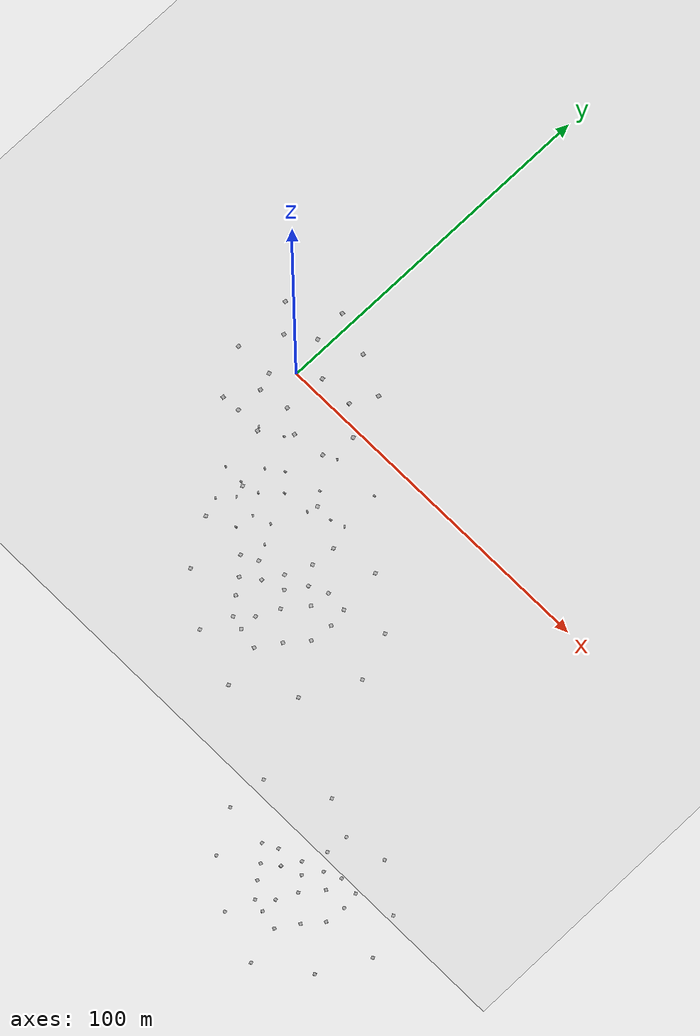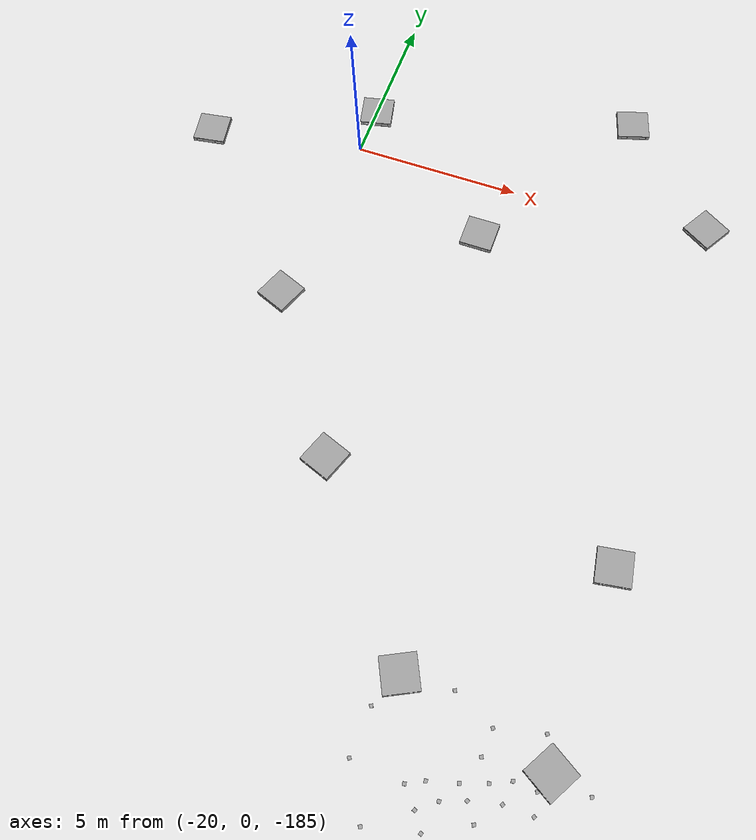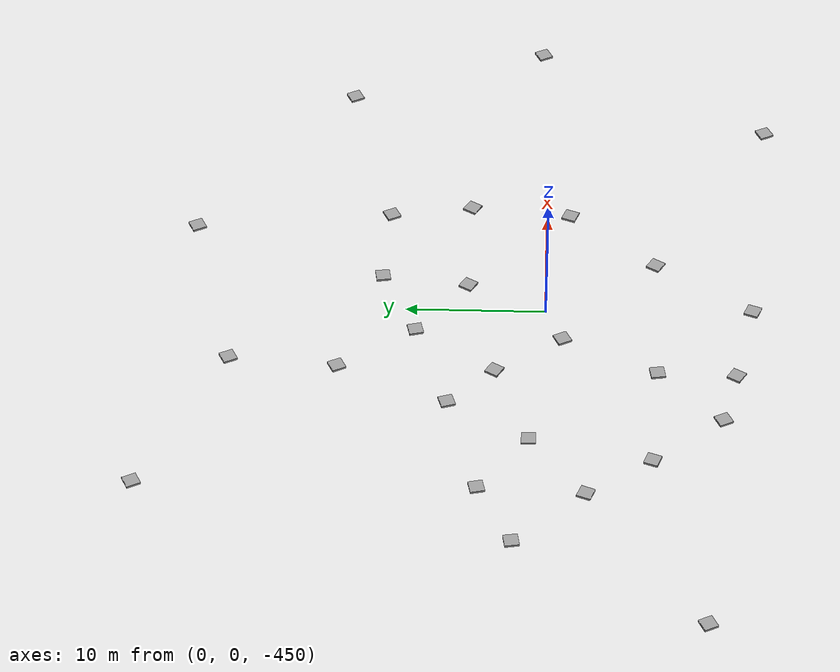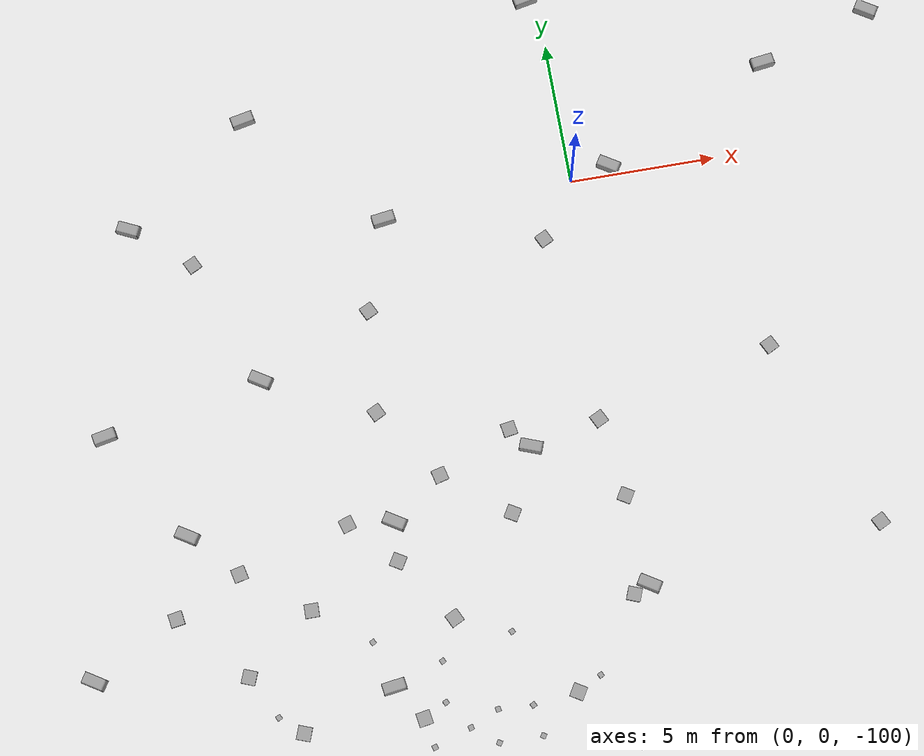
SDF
<sdf version="1.7">
 <world name="default">
  <light name="sun" type="directional">
   <pose>0 0 10 0 -0 0</pose>
   <diffuse>0.8 0.8 0.8 1</diffuse>
   <specular>0.2 0.2 0.2 1</specular>
   <attenuation>
    <range>1000</range>
    <constant>0.9</constant>
    <linear>0.01</linear>
    <quadratic>0.001</quadratic>
   </attenuation>
   <direction>-0.5 0.1 -0.9</direction>
   <spot><inner_angle>0</inner_angle><outer_angle>0</outer_angle><falloff>0</falloff></spot>
  </light>
  <model name="ground_plane">
   <static>1</static>
   <link name="link">
    <collision name="collision">
     <geometry><plane><normal>0 0 1</normal><size>100 100</size></plane></geometry>
     <surface>
      <contact><collide_bitmask>65535</collide_bitmask></contact>
      <friction><ode><mu>100</mu><mu2>50</mu2></ode></friction>
     </surface>
    </collision>
    <visual name="visual">
     <cast_shadows>0</cast_shadows>
     <geometry><plane><normal>0 0 1</normal><size>100 100</size></plane></geometry>
     <material>
      <script><uri>file://media/materials/scripts/gazebo.material</uri><name>Gazebo/Grey</name></script>
     </material>
    </visual>
   </link>
  </model>
  <gravity>0 0 -9.8</gravity>
  <magnetic_field>6e-06 2.3e-05 -4.2e-05</magnetic_field>
  <atmosphere type="adiabatic"/>
  <physics type="ode">
   <max_step_size>0.001</max_step_size>
   <real_time_factor>1</real_time_factor>
   <real_time_update_rate>1000</real_time_update_rate>
  </physics>
  <scene><ambient>0.4 0.4 0.4 1</ambient><background>0.7 0.7 0.7 1</background><shadows>1</shadows></scene>
  <spherical_coordinates>
   <surface_model>EARTH_WGS84</surface_model>
   <latitude_deg>0</latitude_deg>
   <longitude_deg>0</longitude_deg>
   <elevation>0</elevation>
   <heading_deg>0</heading_deg>
  </spherical_coordinates>
  <model name="pallet">
   <link name="link_0">
    <inertial>
     <mass>10</mass>
     <inertia>
      <ixx>0.166667</ixx>
      <ixy>0</ixy>
      <ixz>0</ixz>
      <iyy>0.166667</iyy>
      <iyz>0</iyz>
      <izz>0.166667</izz>
     </inertia>
    </inertial>
    <pose>-7.85304 -0.261089 0 0 -0 0</pose>
    <visual name="visual">
     <geometry><mesh><uri>/home/cyun/pallet.stl</uri><scale>1 1 1</scale></mesh></geometry>
     <material>
      <lighting>1</lighting>
      <script><uri>file://media/materials/scripts/gazebo.material</uri><name>Gazebo/Grey</name></script>
      <shader type="pixel"/>
     </material>
    </visual>
    <collision name="collision">
     <geometry><mesh><uri>/home/cyun/pallet.stl</uri><scale>1 1 1</scale></mesh></geometry>
     <surface>
      <friction>
       <ode><mu>1</mu><mu2>1</mu2><fdir1>0 0 0</fdir1><slip1>0</slip1><slip2>0</slip2></ode>
       <torsional>
        <coefficient>1</coefficient>
        <patch_radius>0</patch_radius>
        <surface_radius>0</surface_radius>
        <use_patch_radius>1</use_patch_radius>
        <ode><slip>0</slip></ode>
       </torsional>
      </friction>
      <bounce><restitution_coefficient>0</restitution_coefficient><threshold>1e+06</threshold></bounce>
      <contact>
       <collide_without_contact>0</collide_without_contact>
       <collide_without_contact_bitmask>1</collide_without_contact_bitmask>
       <collide_bitmask>1</collide_bitmask>
       <ode>
        <soft_cfm>0</soft_cfm>
        <soft_erp>0.2</soft_erp>
        <kp>1e+13</kp>
        <kd>1</kd>
        <max_vel>0.01</max_vel>
        <min_depth>0</min_depth>
       </ode>
       <bullet>
        <split_impulse>1</split_impulse>
        <split_impulse_penetration_threshold>-0.01</split_impulse_penetration_threshold>
        <soft_cfm>0</soft_cfm>
        <soft_erp>0.2</soft_erp>
        <kp>1e+13</kp>
        <kd>1</kd>
       </bullet>
      </contact>
     </surface>
    </collision>
   </link>
   <link name="link_0_clone">
    <inertial>
     <mass>1</mass>
     <inertia>
      <ixx>0.166667</ixx>
      <ixy>0</ixy>
      <ixz>0</ixz>
      <iyy>0.166667</iyy>
      <iyz>0</iyz>
      <izz>0.166667</izz>
     </inertia>
    </inertial>
    <pose>-1.26499 2.18097 0 0 0 -0.538793</pose>
    <visual name="visual">
     <geometry><mesh><uri>/home/cyun/pallet.stl</uri><scale>1 1 1</scale></mesh></geometry>
     <material>
      <lighting>1</lighting>
      <script><uri>file://media/materials/scripts/gazebo.material</uri><name>Gazebo/Grey</name></script>
      <shader type="pixel"/>
     </material>
    </visual>
    <collision name="collision">
     <geometry><mesh><uri>/home/cyun/pallet.stl</uri><scale>1 1 1</scale></mesh></geometry>
     <surface>
      <friction>
       <ode><mu>1</mu><mu2>1</mu2><fdir1>0 0 0</fdir1><slip1>0</slip1><slip2>0</slip2></ode>
       <torsional>
        <coefficient>1</coefficient>
        <patch_radius>0</patch_radius>
        <surface_radius>0</surface_radius>
        <use_patch_radius>1</use_patch_radius>
        <ode><slip>0</slip></ode>
       </torsional>
      </friction>
      <bounce><restitution_coefficient>0</restitution_coefficient><threshold>1e+06</threshold></bounce>
      <contact>
       <collide_without_contact>0</collide_without_contact>
       <collide_without_contact_bitmask>1</collide_without_contact_bitmask>
       <collide_bitmask>1</collide_bitmask>
       <ode>
        <soft_cfm>0</soft_cfm>
        <soft_erp>0.2</soft_erp>
        <kp>1e+13</kp>
        <kd>1</kd>
        <max_vel>0.01</max_vel>
        <min_depth>0</min_depth>
       </ode>
       <bullet>
        <split_impulse>1</split_impulse>
        <split_impulse_penetration_threshold>-0.01</split_impulse_penetration_threshold>
        <soft_cfm>0</soft_cfm>
        <soft_erp>0.2</soft_erp>
        <kp>1e+13</kp>
        <kd>1</kd>
       </bullet>
      </contact>
     </surface>
    </collision>
   </link>
   <link name="link_0_clone_0">
    <inertial>
     <mass>1</mass>
     <inertia>
      <ixx>0.166667</ixx>
      <ixy>0</ixy>
      <ixz>0</ixz>
      <iyy>0.166667</iyy>
      <iyz>0</iyz>
      <izz>0.166667</izz>
     </inertia>
    </inertial>
    <pose>1.99732 -2.48667 0 0 -0 0.458747</pose>
    <visual name="visual">
     <geometry><mesh><uri>/home/cyun/pallet.stl</uri><scale>1 1 1</scale></mesh></geometry>
     <material>
      <lighting>1</lighting>
      <script><uri>file://media/materials/scripts/gazebo.material</uri><name>Gazebo/Grey</name></script>
      <shader type="pixel"/>
     </material>
    </visual>
    <collision name="collision">
     <geometry><mesh><uri>/home/cyun/pallet.stl</uri><scale>1 1 1</scale></mesh></geometry>
     <surface>
      <friction>
       <ode><mu>1</mu><mu2>1</mu2><fdir1>0 0 0</fdir1><slip1>0</slip1><slip2>0</slip2></ode>
       <torsional>
        <coefficient>1</coefficient>
        <patch_radius>0</patch_radius>
        <surface_radius>0</surface_radius>
        <use_patch_radius>1</use_patch_radius>
        <ode><slip>0</slip></ode>
       </torsional>
      </friction>
      <bounce><restitution_coefficient>0</restitution_coefficient><threshold>1e+06</threshold></bounce>
      <contact>
       <collide_without_contact>0</collide_without_contact>
       <collide_without_contact_bitmask>1</collide_without_contact_bitmask>
       <collide_bitmask>1</collide_bitmask>
       <ode>
        <soft_cfm>0</soft_cfm>
        <soft_erp>0.2</soft_erp>
        <kp>1e+13</kp>
        <kd>1</kd>
        <max_vel>0.01</max_vel>
        <min_depth>0</min_depth>
       </ode>
       <bullet>
        <split_impulse>1</split_impulse>
        <split_impulse_penetration_threshold>-0.01</split_impulse_penetration_threshold>
        <soft_cfm>0</soft_cfm>
        <soft_erp>0.2</soft_erp>
        <kp>1e+13</kp>
        <kd>1</kd>
       </bullet>
      </contact>
     </surface>
    </collision>
   </link>
   <link name="link_0_clone_0_clone">
    <inertial>
     <mass>1</mass>
     <inertia>
      <ixx>0.166667</ixx>
      <ixy>0</ixy>
      <ixz>0</ixz>
      <iyy>0.166667</iyy>
      <iyz>0</iyz>
      <izz>0.166667</izz>
     </inertia>
    </inertial>
    <pose>-5.705 -13.523 0 0 -0 0.458747</pose>
    <visual name="visual">
     <geometry><mesh><uri>/home/cyun/pallet.stl</uri><scale>1 1 1</scale></mesh></geometry>
     <material>
      <lighting>1</lighting>
      <script><uri>file://media/materials/scripts/gazebo.material</uri><name>Gazebo/Grey</name></script>
      <shader type="pixel"/>
     </material>
    </visual>
    <collision name="collision">
     <geometry><mesh><uri>/home/cyun/pallet.stl</uri><scale>1 1 1</scale></mesh></geometry>
     <surface>
      <friction>
       <ode><mu>1</mu><mu2>1</mu2><fdir1>0 0 0</fdir1><slip1>0</slip1><slip2>0</slip2></ode>
       <torsional>
        <coefficient>1</coefficient>
        <patch_radius>0</patch_radius>
        <surface_radius>0</surface_radius>
        <use_patch_radius>1</use_patch_radius>
        <ode><slip>0</slip></ode>
       </torsional>
      </friction>
      <bounce><restitution_coefficient>0</restitution_coefficient><threshold>1e+06</threshold></bounce>
      <contact>
       <collide_without_contact>0</collide_without_contact>
       <collide_without_contact_bitmask>1</collide_without_contact_bitmask>
       <collide_bitmask>1</collide_bitmask>
       <ode>
        <soft_cfm>0</soft_cfm>
        <soft_erp>0.2</soft_erp>
        <kp>1e+13</kp>
        <kd>1</kd>
        <max_vel>0.01</max_vel>
        <min_depth>0</min_depth>
       </ode>
       <bullet>
        <split_impulse>1</split_impulse>
        <split_impulse_penetration_threshold>-0.01</split_impulse_penetration_threshold>
        <soft_cfm>0</soft_cfm>
        <soft_erp>0.2</soft_erp>
        <kp>1e+13</kp>
        <kd>1</kd>
       </bullet>
      </contact>
     </surface>
    </collision>
   </link>
   <link name="link_0_clone_0_clone_0">
    <inertial>
     <mass>1</mass>
     <inertia>
      <ixx>0.166667</ixx>
      <ixy>0</ixy>
      <ixz>0</ixz>
      <iyy>0.166667</iyy>
      <iyz>0</iyz>
      <izz>0.166667</izz>
     </inertia>
    </inertial>
    <pose>14.6507 9.90438 0 0 -0 0.458747</pose>
    <visual name="visual">
     <geometry><mesh><uri>/home/cyun/pallet.stl</uri><scale>1 1 1</scale></mesh></geometry>
     <material>
      <lighting>1</lighting>
      <script><uri>file://media/materials/scripts/gazebo.material</uri><name>Gazebo/Grey</name></script>
      <shader type="pixel"/>
     </material>
    </visual>
    <collision name="collision">
     <geometry><mesh><uri>/home/cyun/pallet.stl</uri><scale>1 1 1</scale></mesh></geometry>
     <surface>
      <friction>
       <ode><mu>1</mu><mu2>1</mu2><fdir1>0 0 0</fdir1><slip1>0</slip1><slip2>0</slip2></ode>
       <torsional>
        <coefficient>1</coefficient>
        <patch_radius>0</patch_radius>
        <surface_radius>0</surface_radius>
        <use_patch_radius>1</use_patch_radius>
        <ode><slip>0</slip></ode>
       </torsional>
      </friction>
      <bounce><restitution_coefficient>0</restitution_coefficient><threshold>1e+06</threshold></bounce>
      <contact>
       <collide_without_contact>0</collide_without_contact>
       <collide_without_contact_bitmask>1</collide_without_contact_bitmask>
       <collide_bitmask>1</collide_bitmask>
       <ode>
        <soft_cfm>0</soft_cfm>
        <soft_erp>0.2</soft_erp>
        <kp>1e+13</kp>
        <kd>1</kd>
        <max_vel>0.01</max_vel>
        <min_depth>0</min_depth>
       </ode>
       <bullet>
        <split_impulse>1</split_impulse>
        <split_impulse_penetration_threshold>-0.01</split_impulse_penetration_threshold>
        <soft_cfm>0</soft_cfm>
        <soft_erp>0.2</soft_erp>
        <kp>1e+13</kp>
        <kd>1</kd>
       </bullet>
      </contact>
     </surface>
    </collision>
   </link>
   <link name="link_0_clone_0_clone_0_clone">
    <inertial>
     <mass>1</mass>
     <inertia>
      <ixx>0.166667</ixx>
      <ixy>0</ixy>
      <ixz>0</ixz>
      <iyy>0.166667</iyy>
      <iyz>0</iyz>
      <izz>0.166667</izz>
     </inertia>
    </inertial>
    <pose>-1.08109 13.0918 0 0 -0 0.458747</pose>
    <visual name="visual">
     <geometry><mesh><uri>/home/cyun/pallet.stl</uri><scale>1 1 1</scale></mesh></geometry>
     <material>
      <lighting>1</lighting>
      <script><uri>file://media/materials/scripts/gazebo.material</uri><name>Gazebo/Grey</name></script>
      <shader type="pixel"/>
     </material>
    </visual>
    <collision name="collision">
     <geometry><mesh><uri>/home/cyun/pallet.stl</uri><scale>1 1 1</scale></mesh></geometry>
     <surface>
      <friction>
       <ode><mu>1</mu><mu2>1</mu2><fdir1>0 0 0</fdir1><slip1>0</slip1><slip2>0</slip2></ode>
       <torsional>
        <coefficient>1</coefficient>
        <patch_radius>0</patch_radius>
        <surface_radius>0</surface_radius>
        <use_patch_radius>1</use_patch_radius>
        <ode><slip>0</slip></ode>
       </torsional>
      </friction>
      <bounce><restitution_coefficient>0</restitution_coefficient><threshold>1e+06</threshold></bounce>
      <contact>
       <collide_without_contact>0</collide_without_contact>
       <collide_without_contact_bitmask>1</collide_without_contact_bitmask>
       <collide_bitmask>1</collide_bitmask>
       <ode>
        <soft_cfm>0</soft_cfm>
        <soft_erp>0.2</soft_erp>
        <kp>1e+13</kp>
        <kd>1</kd>
        <max_vel>0.01</max_vel>
        <min_depth>0</min_depth>
       </ode>
       <bullet>
        <split_impulse>1</split_impulse>
        <split_impulse_penetration_threshold>-0.01</split_impulse_penetration_threshold>
        <soft_cfm>0</soft_cfm>
        <soft_erp>0.2</soft_erp>
        <kp>1e+13</kp>
        <kd>1</kd>
       </bullet>
      </contact>
     </surface>
    </collision>
   </link>
   <link name="link_0_clone_0_clone_0_clone_0">
    <inertial>
     <mass>1</mass>
     <inertia>
      <ixx>0.166667</ixx>
      <ixy>0</ixy>
      <ixz>0</ixz>
      <iyy>0.166667</iyy>
      <iyz>0</iyz>
      <izz>0.166667</izz>
     </inertia>
    </inertial>
    <pose>-0.434575 20.651 0 0 -0 0.458747</pose>
    <visual name="visual">
     <geometry><mesh><uri>/home/cyun/pallet.stl</uri><scale>1 1 1</scale></mesh></geometry>
     <material>
      <lighting>1</lighting>
      <script><uri>file://media/materials/scripts/gazebo.material</uri><name>Gazebo/Grey</name></script>
      <shader type="pixel"/>
     </material>
    </visual>
    <collision name="collision">
     <geometry><mesh><uri>/home/cyun/pallet.stl</uri><scale>1 1 1</scale></mesh></geometry>
     <surface>
      <friction>
       <ode><mu>1</mu><mu2>1</mu2><fdir1>0 0 0</fdir1><slip1>0</slip1><slip2>0</slip2></ode>
       <torsional>
        <coefficient>1</coefficient>
        <patch_radius>0</patch_radius>
        <surface_radius>0</surface_radius>
        <use_patch_radius>1</use_patch_radius>
        <ode><slip>0</slip></ode>
       </torsional>
      </friction>
      <bounce><restitution_coefficient>0</restitution_coefficient><threshold>1e+06</threshold></bounce>
      <contact>
       <collide_without_contact>0</collide_without_contact>
       <collide_without_contact_bitmask>1</collide_without_contact_bitmask>
       <collide_bitmask>1</collide_bitmask>
       <ode>
        <soft_cfm>0</soft_cfm>
        <soft_erp>0.2</soft_erp>
        <kp>1e+13</kp>
        <kd>1</kd>
        <max_vel>0.01</max_vel>
        <min_depth>0</min_depth>
       </ode>
       <bullet>
        <split_impulse>1</split_impulse>
        <split_impulse_penetration_threshold>-0.01</split_impulse_penetration_threshold>
        <soft_cfm>0</soft_cfm>
        <soft_erp>0.2</soft_erp>
        <kp>1e+13</kp>
        <kd>1</kd>
       </bullet>
      </contact>
     </surface>
    </collision>
   </link>
   <link name="link_0_clone_0_clone_0_clone_1">
    <inertial>
     <mass>1</mass>
     <inertia>
      <ixx>0.166667</ixx>
      <ixy>0</ixy>
      <ixz>0</ixz>
      <iyy>0.166667</iyy>
      <iyz>0</iyz>
      <izz>0.166667</izz>
     </inertia>
    </inertial>
    <pose>-12.5592 26.2569 0 0 -0 0.458747</pose>
    <visual name="visual">
     <geometry><mesh><uri>/home/cyun/pallet.stl</uri><scale>1 1 1</scale></mesh></geometry>
     <material>
      <lighting>1</lighting>
      <script><uri>file://media/materials/scripts/gazebo.material</uri><name>Gazebo/Grey</name></script>
      <shader type="pixel"/>
     </material>
    </visual>
    <collision name="collision">
     <geometry><mesh><uri>/home/cyun/pallet.stl</uri><scale>1 1 1</scale></mesh></geometry>
     <surface>
      <friction>
       <ode><mu>1</mu><mu2>1</mu2><fdir1>0 0 0</fdir1><slip1>0</slip1><slip2>0</slip2></ode>
       <torsional>
        <coefficient>1</coefficient>
        <patch_radius>0</patch_radius>
        <surface_radius>0</surface_radius>
        <use_patch_radius>1</use_patch_radius>
        <ode><slip>0</slip></ode>
       </torsional>
      </friction>
      <bounce><restitution_coefficient>0</restitution_coefficient><threshold>1e+06</threshold></bounce>
      <contact>
       <collide_without_contact>0</collide_without_contact>
       <collide_without_contact_bitmask>1</collide_without_contact_bitmask>
       <collide_bitmask>1</collide_bitmask>
       <ode>
        <soft_cfm>0</soft_cfm>
        <soft_erp>0.2</soft_erp>
        <kp>1e+13</kp>
        <kd>1</kd>
        <max_vel>0.01</max_vel>
        <min_depth>0</min_depth>
       </ode>
       <bullet>
        <split_impulse>1</split_impulse>
        <split_impulse_penetration_threshold>-0.01</split_impulse_penetration_threshold>
        <soft_cfm>0</soft_cfm>
        <soft_erp>0.2</soft_erp>
        <kp>1e+13</kp>
        <kd>1</kd>
       </bullet>
      </contact>
     </surface>
    </collision>
   </link>
   <link name="link_0_clone_0_clone_0_clone_10">
    <inertial>
     <mass>1</mass>
     <inertia>
      <ixx>0.166667</ixx>
      <ixy>0</ixy>
      <ixz>0</ixz>
      <iyy>0.166667</iyy>
      <iyz>0</iyz>
      <izz>0.166667</izz>
     </inertia>
    </inertial>
    <pose>27.8311 13.1831 0 0 -0 0.458747</pose>
    <visual name="visual">
     <geometry><mesh><uri>/home/cyun/pallet.stl</uri><scale>1 1 1</scale></mesh></geometry>
     <material>
      <lighting>1</lighting>
      <script><uri>file://media/materials/scripts/gazebo.material</uri><name>Gazebo/Grey</name></script>
      <shader type="pixel"/>
     </material>
    </visual>
    <collision name="collision">
     <geometry><mesh><uri>/home/cyun/pallet.stl</uri><scale>1 1 1</scale></mesh></geometry>
     <surface>
      <friction>
       <ode><mu>1</mu><mu2>1</mu2><fdir1>0 0 0</fdir1><slip1>0</slip1><slip2>0</slip2></ode>
       <torsional>
        <coefficient>1</coefficient>
        <patch_radius>0</patch_radius>
        <surface_radius>0</surface_radius>
        <use_patch_radius>1</use_patch_radius>
        <ode><slip>0</slip></ode>
       </torsional>
      </friction>
      <bounce><restitution_coefficient>0</restitution_coefficient><threshold>1e+06</threshold></bounce>
      <contact>
       <collide_without_contact>0</collide_without_contact>
       <collide_without_contact_bitmask>1</collide_without_contact_bitmask>
       <collide_bitmask>1</collide_bitmask>
       <ode>
        <soft_cfm>0</soft_cfm>
        <soft_erp>0.2</soft_erp>
        <kp>1e+13</kp>
        <kd>1</kd>
        <max_vel>0.01</max_vel>
        <min_depth>0</min_depth>
       </ode>
       <bullet>
        <split_impulse>1</split_impulse>
        <split_impulse_penetration_threshold>-0.01</split_impulse_penetration_threshold>
        <soft_cfm>0</soft_cfm>
        <soft_erp>0.2</soft_erp>
        <kp>1e+13</kp>
        <kd>1</kd>
       </bullet>
      </contact>
     </surface>
    </collision>
   </link>
   <link name="link_0_clone_0_clone_0_clone_2">
    <inertial>
     <mass>1</mass>
     <inertia>
      <ixx>0.166667</ixx>
      <ixy>0</ixy>
      <ixz>0</ixz>
      <iyy>0.166667</iyy>
      <iyz>0</iyz>
      <izz>0.166667</izz>
     </inertia>
    </inertial>
    <pose>13.1146 23.8555 0 0 -0 0.458747</pose>
    <visual name="visual">
     <geometry><mesh><uri>/home/cyun/pallet.stl</uri><scale>1 1 1</scale></mesh></geometry>
     <material>
      <lighting>1</lighting>
      <script><uri>file://media/materials/scripts/gazebo.material</uri><name>Gazebo/Grey</name></script>
      <shader type="pixel"/>
     </material>
    </visual>
    <collision name="collision">
     <geometry><mesh><uri>/home/cyun/pallet.stl</uri><scale>1 1 1</scale></mesh></geometry>
     <surface>
      <friction>
       <ode><mu>1</mu><mu2>1</mu2><fdir1>0 0 0</fdir1><slip1>0</slip1><slip2>0</slip2></ode>
       <torsional>
        <coefficient>1</coefficient>
        <patch_radius>0</patch_radius>
        <surface_radius>0</surface_radius>
        <use_patch_radius>1</use_patch_radius>
        <ode><slip>0</slip></ode>
       </torsional>
      </friction>
      <bounce><restitution_coefficient>0</restitution_coefficient><threshold>1e+06</threshold></bounce>
      <contact>
       <collide_without_contact>0</collide_without_contact>
       <collide_without_contact_bitmask>1</collide_without_contact_bitmask>
       <collide_bitmask>1</collide_bitmask>
       <ode>
        <soft_cfm>0</soft_cfm>
        <soft_erp>0.2</soft_erp>
        <kp>1e+13</kp>
        <kd>1</kd>
        <max_vel>0.01</max_vel>
        <min_depth>0</min_depth>
       </ode>
       <bullet>
        <split_impulse>1</split_impulse>
        <split_impulse_penetration_threshold>-0.01</split_impulse_penetration_threshold>
        <soft_cfm>0</soft_cfm>
        <soft_erp>0.2</soft_erp>
        <kp>1e+13</kp>
        <kd>1</kd>
       </bullet>
      </contact>
     </surface>
    </collision>
   </link>
   <link name="link_0_clone_0_clone_0_clone_3">
    <inertial>
     <mass>1</mass>
     <inertia>
      <ixx>0.166667</ixx>
      <ixy>0</ixy>
      <ixz>0</ixz>
      <iyy>0.166667</iyy>
      <iyz>0</iyz>
      <izz>0.166667</izz>
     </inertia>
    </inertial>
    <pose>-31.7236 15.5437 0 0 -0 0.458747</pose>
    <visual name="visual">
     <geometry><mesh><uri>/home/cyun/pallet.stl</uri><scale>1 1 1</scale></mesh></geometry>
     <material>
      <lighting>1</lighting>
      <script><uri>file://media/materials/scripts/gazebo.material</uri><name>Gazebo/Grey</name></script>
      <shader type="pixel"/>
     </material>
    </visual>
    <collision name="collision">
     <geometry><mesh><uri>/home/cyun/pallet.stl</uri><scale>1 1 1</scale></mesh></geometry>
     <surface>
      <friction>
       <ode><mu>1</mu><mu2>1</mu2><fdir1>0 0 0</fdir1><slip1>0</slip1><slip2>0</slip2></ode>
       <torsional>
        <coefficient>1</coefficient>
        <patch_radius>0</patch_radius>
        <surface_radius>0</surface_radius>
        <use_patch_radius>1</use_patch_radius>
        <ode><slip>0</slip></ode>
       </torsional>
      </friction>
      <bounce><restitution_coefficient>0</restitution_coefficient><threshold>1e+06</threshold></bounce>
      <contact>
       <collide_without_contact>0</collide_without_contact>
       <collide_without_contact_bitmask>1</collide_without_contact_bitmask>
       <collide_bitmask>1</collide_bitmask>
       <ode>
        <soft_cfm>0</soft_cfm>
        <soft_erp>0.2</soft_erp>
        <kp>1e+13</kp>
        <kd>1</kd>
        <max_vel>0.01</max_vel>
        <min_depth>0</min_depth>
       </ode>
       <bullet>
        <split_impulse>1</split_impulse>
        <split_impulse_penetration_threshold>-0.01</split_impulse_penetration_threshold>
        <soft_cfm>0</soft_cfm>
        <soft_erp>0.2</soft_erp>
        <kp>1e+13</kp>
        <kd>1</kd>
       </bullet>
      </contact>
     </surface>
    </collision>
   </link>
   <link name="link_0_clone_0_clone_0_clone_4">
    <inertial>
     <mass>1</mass>
     <inertia>
      <ixx>0.166667</ixx>
      <ixy>0</ixy>
      <ixz>0</ixz>
      <iyy>0.166667</iyy>
      <iyz>0</iyz>
      <izz>0.166667</izz>
     </inertia>
    </inertial>
    <pose>-32.5157 1.87816 0 0 -0 0.458747</pose>
    <visual name="visual">
     <geometry><mesh><uri>/home/cyun/pallet.stl</uri><scale>1 1 1</scale></mesh></geometry>
     <material>
      <lighting>1</lighting>
      <script><uri>file://media/materials/scripts/gazebo.material</uri><name>Gazebo/Grey</name></script>
      <shader type="pixel"/>
     </material>
    </visual>
    <collision name="collision">
     <geometry><mesh><uri>/home/cyun/pallet.stl</uri><scale>1 1 1</scale></mesh></geometry>
     <surface>
      <friction>
       <ode><mu>1</mu><mu2>1</mu2><fdir1>0 0 0</fdir1><slip1>0</slip1><slip2>0</slip2></ode>
       <torsional>
        <coefficient>1</coefficient>
        <patch_radius>0</patch_radius>
        <surface_radius>0</surface_radius>
        <use_patch_radius>1</use_patch_radius>
        <ode><slip>0</slip></ode>
       </torsional>
      </friction>
      <bounce><restitution_coefficient>0</restitution_coefficient><threshold>1e+06</threshold></bounce>
      <contact>
       <collide_without_contact>0</collide_without_contact>
       <collide_without_contact_bitmask>1</collide_without_contact_bitmask>
       <collide_bitmask>1</collide_bitmask>
       <ode>
        <soft_cfm>0</soft_cfm>
        <soft_erp>0.2</soft_erp>
        <kp>1e+13</kp>
        <kd>1</kd>
        <max_vel>0.01</max_vel>
        <min_depth>0</min_depth>
       </ode>
       <bullet>
        <split_impulse>1</split_impulse>
        <split_impulse_penetration_threshold>-0.01</split_impulse_penetration_threshold>
        <soft_cfm>0</soft_cfm>
        <soft_erp>0.2</soft_erp>
        <kp>1e+13</kp>
        <kd>1</kd>
       </bullet>
      </contact>
     </surface>
    </collision>
   </link>
   <link name="link_0_clone_0_clone_0_clone_5">
    <inertial>
     <mass>1</mass>
     <inertia>
      <ixx>0.166667</ixx>
      <ixy>0</ixy>
      <ixz>0</ixz>
      <iyy>0.166667</iyy>
      <iyz>0</iyz>
      <izz>0.166667</izz>
     </inertia>
    </inertial>
    <pose>-24.3083 -12.0747 0 0 -0 0.458747</pose>
    <visual name="visual">
     <geometry><mesh><uri>/home/cyun/pallet.stl</uri><scale>1 1 1</scale></mesh></geometry>
     <material>
      <lighting>1</lighting>
      <script><uri>file://media/materials/scripts/gazebo.material</uri><name>Gazebo/Grey</name></script>
      <shader type="pixel"/>
     </material>
    </visual>
    <collision name="collision">
     <geometry><mesh><uri>/home/cyun/pallet.stl</uri><scale>1 1 1</scale></mesh></geometry>
     <surface>
      <friction>
       <ode><mu>1</mu><mu2>1</mu2><fdir1>0 0 0</fdir1><slip1>0</slip1><slip2>0</slip2></ode>
       <torsional>
        <coefficient>1</coefficient>
        <patch_radius>0</patch_radius>
        <surface_radius>0</surface_radius>
        <use_patch_radius>1</use_patch_radius>
        <ode><slip>0</slip></ode>
       </torsional>
      </friction>
      <bounce><restitution_coefficient>0</restitution_coefficient><threshold>1e+06</threshold></bounce>
      <contact>
       <collide_without_contact>0</collide_without_contact>
       <collide_without_contact_bitmask>1</collide_without_contact_bitmask>
       <collide_bitmask>1</collide_bitmask>
       <ode>
        <soft_cfm>0</soft_cfm>
        <soft_erp>0.2</soft_erp>
        <kp>1e+13</kp>
        <kd>1</kd>
        <max_vel>0.01</max_vel>
        <min_depth>0</min_depth>
       </ode>
       <bullet>
        <split_impulse>1</split_impulse>
        <split_impulse_penetration_threshold>-0.01</split_impulse_penetration_threshold>
        <soft_cfm>0</soft_cfm>
        <soft_erp>0.2</soft_erp>
        <kp>1e+13</kp>
        <kd>1</kd>
       </bullet>
      </contact>
     </surface>
    </collision>
   </link>
   <link name="link_0_clone_0_clone_0_clone_6">
    <inertial>
     <mass>1</mass>
     <inertia>
      <ixx>0.166667</ixx>
      <ixy>0</ixy>
      <ixz>0</ixz>
      <iyy>0.166667</iyy>
      <iyz>0</iyz>
      <izz>0.166667</izz>
     </inertia>
    </inertial>
    <pose>-9.39579 -22.8733 0 0 -0 0.458747</pose>
    <visual name="visual">
     <geometry><mesh><uri>/home/cyun/pallet.stl</uri><scale>1 1 1</scale></mesh></geometry>
     <material>
      <lighting>1</lighting>
      <script><uri>file://media/materials/scripts/gazebo.material</uri><name>Gazebo/Grey</name></script>
      <shader type="pixel"/>
     </material>
    </visual>
    <collision name="collision">
     <geometry><mesh><uri>/home/cyun/pallet.stl</uri><scale>1 1 1</scale></mesh></geometry>
     <surface>
      <friction>
       <ode><mu>1</mu><mu2>1</mu2><fdir1>0 0 0</fdir1><slip1>0</slip1><slip2>0</slip2></ode>
       <torsional>
        <coefficient>1</coefficient>
        <patch_radius>0</patch_radius>
        <surface_radius>0</surface_radius>
        <use_patch_radius>1</use_patch_radius>
        <ode><slip>0</slip></ode>
       </torsional>
      </friction>
      <bounce><restitution_coefficient>0</restitution_coefficient><threshold>1e+06</threshold></bounce>
      <contact>
       <collide_without_contact>0</collide_without_contact>
       <collide_without_contact_bitmask>1</collide_without_contact_bitmask>
       <collide_bitmask>1</collide_bitmask>
       <ode>
        <soft_cfm>0</soft_cfm>
        <soft_erp>0.2</soft_erp>
        <kp>1e+13</kp>
        <kd>1</kd>
        <max_vel>0.01</max_vel>
        <min_depth>0</min_depth>
       </ode>
       <bullet>
        <split_impulse>1</split_impulse>
        <split_impulse_penetration_threshold>-0.01</split_impulse_penetration_threshold>
        <soft_cfm>0</soft_cfm>
        <soft_erp>0.2</soft_erp>
        <kp>1e+13</kp>
        <kd>1</kd>
       </bullet>
      </contact>
     </surface>
    </collision>
   </link>
   <link name="link_0_clone_0_clone_0_clone_7">
    <inertial>
     <mass>1</mass>
     <inertia>
      <ixx>0.166667</ixx>
      <ixy>0</ixy>
      <ixz>0</ixz>
      <iyy>0.166667</iyy>
      <iyz>0</iyz>
      <izz>0.166667</izz>
     </inertia>
    </inertial>
    <pose>7.99843 -28.5995 0 0 -0 0.458747</pose>
    <visual name="visual">
     <geometry><mesh><uri>/home/cyun/pallet.stl</uri><scale>1 1 1</scale></mesh></geometry>
     <material>
      <lighting>1</lighting>
      <script><uri>file://media/materials/scripts/gazebo.material</uri><name>Gazebo/Grey</name></script>
      <shader type="pixel"/>
     </material>
    </visual>
    <collision name="collision">
     <geometry><mesh><uri>/home/cyun/pallet.stl</uri><scale>1 1 1</scale></mesh></geometry>
     <surface>
      <friction>
       <ode><mu>1</mu><mu2>1</mu2><fdir1>0 0 0</fdir1><slip1>0</slip1><slip2>0</slip2></ode>
       <torsional>
        <coefficient>1</coefficient>
        <patch_radius>0</patch_radius>
        <surface_radius>0</surface_radius>
        <use_patch_radius>1</use_patch_radius>
        <ode><slip>0</slip></ode>
       </torsional>
      </friction>
      <bounce><restitution_coefficient>0</restitution_coefficient><threshold>1e+06</threshold></bounce>
      <contact>
       <collide_without_contact>0</collide_without_contact>
       <collide_without_contact_bitmask>1</collide_without_contact_bitmask>
       <collide_bitmask>1</collide_bitmask>
       <ode>
        <soft_cfm>0</soft_cfm>
        <soft_erp>0.2</soft_erp>
        <kp>1e+13</kp>
        <kd>1</kd>
        <max_vel>0.01</max_vel>
        <min_depth>0</min_depth>
       </ode>
       <bullet>
        <split_impulse>1</split_impulse>
        <split_impulse_penetration_threshold>-0.01</split_impulse_penetration_threshold>
        <soft_cfm>0</soft_cfm>
        <soft_erp>0.2</soft_erp>
        <kp>1e+13</kp>
        <kd>1</kd>
       </bullet>
      </contact>
     </surface>
    </collision>
   </link>
   <link name="link_0_clone_0_clone_0_clone_8">
    <inertial>
     <mass>1</mass>
     <inertia>
      <ixx>0.166667</ixx>
      <ixy>0</ixy>
      <ixz>0</ixz>
      <iyy>0.166667</iyy>
      <iyz>0</iyz>
      <izz>0.166667</izz>
     </inertia>
    </inertial>
    <pose>24.3506 -17.2484 0 0 -0 0.458747</pose>
    <visual name="visual">
     <geometry><mesh><uri>/home/cyun/pallet.stl</uri><scale>1 1 1</scale></mesh></geometry>
     <material>
      <lighting>1</lighting>
      <script><uri>file://media/materials/scripts/gazebo.material</uri><name>Gazebo/Grey</name></script>
      <shader type="pixel"/>
     </material>
    </visual>
    <collision name="collision">
     <geometry><mesh><uri>/home/cyun/pallet.stl</uri><scale>1 1 1</scale></mesh></geometry>
     <surface>
      <friction>
       <ode><mu>1</mu><mu2>1</mu2><fdir1>0 0 0</fdir1><slip1>0</slip1><slip2>0</slip2></ode>
       <torsional>
        <coefficient>1</coefficient>
        <patch_radius>0</patch_radius>
        <surface_radius>0</surface_radius>
        <use_patch_radius>1</use_patch_radius>
        <ode><slip>0</slip></ode>
       </torsional>
      </friction>
      <bounce><restitution_coefficient>0</restitution_coefficient><threshold>1e+06</threshold></bounce>
      <contact>
       <collide_without_contact>0</collide_without_contact>
       <collide_without_contact_bitmask>1</collide_without_contact_bitmask>
       <collide_bitmask>1</collide_bitmask>
       <ode>
        <soft_cfm>0</soft_cfm>
        <soft_erp>0.2</soft_erp>
        <kp>1e+13</kp>
        <kd>1</kd>
        <max_vel>0.01</max_vel>
        <min_depth>0</min_depth>
       </ode>
       <bullet>
        <split_impulse>1</split_impulse>
        <split_impulse_penetration_threshold>-0.01</split_impulse_penetration_threshold>
        <soft_cfm>0</soft_cfm>
        <soft_erp>0.2</soft_erp>
        <kp>1e+13</kp>
        <kd>1</kd>
       </bullet>
      </contact>
     </surface>
    </collision>
   </link>
   <link name="link_0_clone_0_clone_0_clone_9">
    <inertial>
     <mass>1</mass>
     <inertia>
      <ixx>0.166667</ixx>
      <ixy>0</ixy>
      <ixz>0</ixz>
      <iyy>0.166667</iyy>
      <iyz>0</iyz>
      <izz>0.166667</izz>
     </inertia>
    </inertial>
    <pose>33.0774 -0.850637 0 0 -0 0.458747</pose>
    <visual name="visual">
     <geometry><mesh><uri>/home/cyun/pallet.stl</uri><scale>1 1 1</scale></mesh></geometry>
     <material>
      <lighting>1</lighting>
      <script><uri>file://media/materials/scripts/gazebo.material</uri><name>Gazebo/Grey</name></script>
      <shader type="pixel"/>
     </material>
    </visual>
    <collision name="collision">
     <geometry><mesh><uri>/home/cyun/pallet.stl</uri><scale>1 1 1</scale></mesh></geometry>
     <surface>
      <friction>
       <ode><mu>1</mu><mu2>1</mu2><fdir1>0 0 0</fdir1><slip1>0</slip1><slip2>0</slip2></ode>
       <torsional>
        <coefficient>1</coefficient>
        <patch_radius>0</patch_radius>
        <surface_radius>0</surface_radius>
        <use_patch_radius>1</use_patch_radius>
        <ode><slip>0</slip></ode>
       </torsional>
      </friction>
      <bounce><restitution_coefficient>0</restitution_coefficient><threshold>1e+06</threshold></bounce>
      <contact>
       <collide_without_contact>0</collide_without_contact>
       <collide_without_contact_bitmask>1</collide_without_contact_bitmask>
       <collide_bitmask>1</collide_bitmask>
       <ode>
        <soft_cfm>0</soft_cfm>
        <soft_erp>0.2</soft_erp>
        <kp>1e+13</kp>
        <kd>1</kd>
        <max_vel>0.01</max_vel>
        <min_depth>0</min_depth>
       </ode>
       <bullet>
        <split_impulse>1</split_impulse>
        <split_impulse_penetration_threshold>-0.01</split_impulse_penetration_threshold>
        <soft_cfm>0</soft_cfm>
        <soft_erp>0.2</soft_erp>
        <kp>1e+13</kp>
        <kd>1</kd>
       </bullet>
      </contact>
     </surface>
    </collision>
   </link>
   <link name="link_0_clone_1">
    <inertial>
     <mass>1</mass>
     <inertia>
      <ixx>0.166667</ixx>
      <ixy>0</ixy>
      <ixz>0</ixz>
      <iyy>0.166667</iyy>
      <iyz>0</iyz>
      <izz>0.166667</izz>
     </inertia>
    </inertial>
    <pose>-9.66787 -8.65812 0 0 0 -0.351403</pose>
    <visual name="visual">
     <geometry><mesh><uri>/home/cyun/pallet.stl</uri><scale>1 1 1</scale></mesh></geometry>
     <material>
      <lighting>1</lighting>
      <script><uri>file://media/materials/scripts/gazebo.material</uri><name>Gazebo/Grey</name></script>
      <shader type="pixel"/>
     </material>
    </visual>
    <collision name="collision">
     <geometry><mesh><uri>/home/cyun/pallet.stl</uri><scale>1 1 1</scale></mesh></geometry>
     <surface>
      <friction>
       <ode><mu>1</mu><mu2>1</mu2><fdir1>0 0 0</fdir1><slip1>0</slip1><slip2>0</slip2></ode>
       <torsional>
        <coefficient>1</coefficient>
        <patch_radius>0</patch_radius>
        <surface_radius>0</surface_radius>
        <use_patch_radius>1</use_patch_radius>
        <ode><slip>0</slip></ode>
       </torsional>
      </friction>
      <bounce><restitution_coefficient>0</restitution_coefficient><threshold>1e+06</threshold></bounce>
      <contact>
       <collide_without_contact>0</collide_without_contact>
       <collide_without_contact_bitmask>1</collide_without_contact_bitmask>
       <collide_bitmask>1</collide_bitmask>
       <ode>
        <soft_cfm>0</soft_cfm>
        <soft_erp>0.2</soft_erp>
        <kp>1e+13</kp>
        <kd>1</kd>
        <max_vel>0.01</max_vel>
        <min_depth>0</min_depth>
       </ode>
       <bullet>
        <split_impulse>1</split_impulse>
        <split_impulse_penetration_threshold>-0.01</split_impulse_penetration_threshold>
        <soft_cfm>0</soft_cfm>
        <soft_erp>0.2</soft_erp>
        <kp>1e+13</kp>
        <kd>1</kd>
       </bullet>
      </contact>
     </surface>
    </collision>
   </link>
   <link name="link_0_clone_2">
    <inertial>
     <mass>1</mass>
     <inertia>
      <ixx>0.166667</ixx>
      <ixy>0</ixy>
      <ixz>0</ixz>
      <iyy>0.166667</iyy>
      <iyz>0</iyz>
      <izz>0.166667</izz>
     </inertia>
    </inertial>
    <pose>-12.8762 -4.15782 0 0 0 -0.370849</pose>
    <visual name="visual">
     <geometry><mesh><uri>/home/cyun/pallet.stl</uri><scale>1 1 1</scale></mesh></geometry>
     <material>
      <lighting>1</lighting>
      <script><uri>file://media/materials/scripts/gazebo.material</uri><name>Gazebo/Grey</name></script>
      <shader type="pixel"/>
     </material>
    </visual>
    <collision name="collision">
     <geometry><mesh><uri>/home/cyun/pallet.stl</uri><scale>1 1 1</scale></mesh></geometry>
     <surface>
      <friction>
       <ode><mu>1</mu><mu2>1</mu2><fdir1>0 0 0</fdir1><slip1>0</slip1><slip2>0</slip2></ode>
       <torsional>
        <coefficient>1</coefficient>
        <patch_radius>0</patch_radius>
        <surface_radius>0</surface_radius>
        <use_patch_radius>1</use_patch_radius>
        <ode><slip>0</slip></ode>
       </torsional>
      </friction>
      <bounce><restitution_coefficient>0</restitution_coefficient><threshold>1e+06</threshold></bounce>
      <contact>
       <collide_without_contact>0</collide_without_contact>
       <collide_without_contact_bitmask>1</collide_without_contact_bitmask>
       <collide_bitmask>1</collide_bitmask>
       <ode>
        <soft_cfm>0</soft_cfm>
        <soft_erp>0.2</soft_erp>
        <kp>1e+13</kp>
        <kd>1</kd>
        <max_vel>0.01</max_vel>
        <min_depth>0</min_depth>
       </ode>
       <bullet>
        <split_impulse>1</split_impulse>
        <split_impulse_penetration_threshold>-0.01</split_impulse_penetration_threshold>
        <soft_cfm>0</soft_cfm>
        <soft_erp>0.2</soft_erp>
        <kp>1e+13</kp>
        <kd>1</kd>
       </bullet>
      </contact>
     </surface>
    </collision>
   </link>
   <link name="link_0_clone_2_clone">
    <inertial>
     <mass>1</mass>
     <inertia>
      <ixx>0.166667</ixx>
      <ixy>0</ixy>
      <ixz>0</ixz>
      <iyy>0.166667</iyy>
      <iyz>0</iyz>
      <izz>0.166667</izz>
     </inertia>
    </inertial>
    <pose>5.10882 -15.8311 0 0 0 -0.370849</pose>
    <visual name="visual">
     <geometry><mesh><uri>/home/cyun/pallet.stl</uri><scale>1 1 1</scale></mesh></geometry>
     <material>
      <lighting>1</lighting>
      <script><uri>file://media/materials/scripts/gazebo.material</uri><name>Gazebo/Grey</name></script>
      <shader type="pixel"/>
     </material>
    </visual>
    <collision name="collision">
     <geometry><mesh><uri>/home/cyun/pallet.stl</uri><scale>1 1 1</scale></mesh></geometry>
     <surface>
      <friction>
       <ode><mu>1</mu><mu2>1</mu2><fdir1>0 0 0</fdir1><slip1>0</slip1><slip2>0</slip2></ode>
       <torsional>
        <coefficient>1</coefficient>
        <patch_radius>0</patch_radius>
        <surface_radius>0</surface_radius>
        <use_patch_radius>1</use_patch_radius>
        <ode><slip>0</slip></ode>
       </torsional>
      </friction>
      <bounce><restitution_coefficient>0</restitution_coefficient><threshold>1e+06</threshold></bounce>
      <contact>
       <collide_without_contact>0</collide_without_contact>
       <collide_without_contact_bitmask>1</collide_without_contact_bitmask>
       <collide_bitmask>1</collide_bitmask>
       <ode>
        <soft_cfm>0</soft_cfm>
        <soft_erp>0.2</soft_erp>
        <kp>1e+13</kp>
        <kd>1</kd>
        <max_vel>0.01</max_vel>
        <min_depth>0</min_depth>
       </ode>
       <bullet>
        <split_impulse>1</split_impulse>
        <split_impulse_penetration_threshold>-0.01</split_impulse_penetration_threshold>
        <soft_cfm>0</soft_cfm>
        <soft_erp>0.2</soft_erp>
        <kp>1e+13</kp>
        <kd>1</kd>
       </bullet>
      </contact>
     </surface>
    </collision>
   </link>
   <link name="link_0_clone_2_clone_0">
    <inertial>
     <mass>1</mass>
     <inertia>
      <ixx>0.166667</ixx>
      <ixy>0</ixy>
      <ixz>0</ixz>
      <iyy>0.166667</iyy>
      <iyz>0</iyz>
      <izz>0.166667</izz>
     </inertia>
    </inertial>
    <pose>14.8132 -2.97693 0 0 0 -0.370849</pose>
    <visual name="visual">
     <geometry><mesh><uri>/home/cyun/pallet.stl</uri><scale>1 1 1</scale></mesh></geometry>
     <material>
      <lighting>1</lighting>
      <script><uri>file://media/materials/scripts/gazebo.material</uri><name>Gazebo/Grey</name></script>
      <shader type="pixel"/>
     </material>
    </visual>
    <collision name="collision">
     <geometry><mesh><uri>/home/cyun/pallet.stl</uri><scale>1 1 1</scale></mesh></geometry>
     <surface>
      <friction>
       <ode><mu>1</mu><mu2>1</mu2><fdir1>0 0 0</fdir1><slip1>0</slip1><slip2>0</slip2></ode>
       <torsional>
        <coefficient>1</coefficient>
        <patch_radius>0</patch_radius>
        <surface_radius>0</surface_radius>
        <use_patch_radius>1</use_patch_radius>
        <ode><slip>0</slip></ode>
       </torsional>
      </friction>
      <bounce><restitution_coefficient>0</restitution_coefficient><threshold>1e+06</threshold></bounce>
      <contact>
       <collide_without_contact>0</collide_without_contact>
       <collide_without_contact_bitmask>1</collide_without_contact_bitmask>
       <collide_bitmask>1</collide_bitmask>
       <ode>
        <soft_cfm>0</soft_cfm>
        <soft_erp>0.2</soft_erp>
        <kp>1e+13</kp>
        <kd>1</kd>
        <max_vel>0.01</max_vel>
        <min_depth>0</min_depth>
       </ode>
       <bullet>
        <split_impulse>1</split_impulse>
        <split_impulse_penetration_threshold>-0.01</split_impulse_penetration_threshold>
        <soft_cfm>0</soft_cfm>
        <soft_erp>0.2</soft_erp>
        <kp>1e+13</kp>
        <kd>1</kd>
       </bullet>
      </contact>
     </surface>
    </collision>
   </link>
   <link name="link_0_clone_3">
    <inertial>
     <mass>1</mass>
     <inertia>
      <ixx>0.166667</ixx>
      <ixy>0</ixy>
      <ixz>0</ixz>
      <iyy>0.166667</iyy>
      <iyz>0</iyz>
      <izz>0.166667</izz>
     </inertia>
    </inertial>
    <pose>-12.5007 3.16055 0 0 -0 0.2216</pose>
    <visual name="visual">
     <geometry><mesh><uri>/home/cyun/pallet.stl</uri><scale>1 1 1</scale></mesh></geometry>
     <material>
      <lighting>1</lighting>
      <script><uri>file://media/materials/scripts/gazebo.material</uri><name>Gazebo/Grey</name></script>
      <shader type="pixel"/>
     </material>
    </visual>
    <collision name="collision">
     <geometry><mesh><uri>/home/cyun/pallet.stl</uri><scale>1 1 1</scale></mesh></geometry>
     <surface>
      <friction>
       <ode><mu>1</mu><mu2>1</mu2><fdir1>0 0 0</fdir1><slip1>0</slip1><slip2>0</slip2></ode>
       <torsional>
        <coefficient>1</coefficient>
        <patch_radius>0</patch_radius>
        <surface_radius>0</surface_radius>
        <use_patch_radius>1</use_patch_radius>
        <ode><slip>0</slip></ode>
       </torsional>
      </friction>
      <bounce><restitution_coefficient>0</restitution_coefficient><threshold>1e+06</threshold></bounce>
      <contact>
       <collide_without_contact>0</collide_without_contact>
       <collide_without_contact_bitmask>1</collide_without_contact_bitmask>
       <collide_bitmask>1</collide_bitmask>
       <ode>
        <soft_cfm>0</soft_cfm>
        <soft_erp>0.2</soft_erp>
        <kp>1e+13</kp>
        <kd>1</kd>
        <max_vel>0.01</max_vel>
        <min_depth>0</min_depth>
       </ode>
       <bullet>
        <split_impulse>1</split_impulse>
        <split_impulse_penetration_threshold>-0.01</split_impulse_penetration_threshold>
        <soft_cfm>0</soft_cfm>
        <soft_erp>0.2</soft_erp>
        <kp>1e+13</kp>
        <kd>1</kd>
       </bullet>
      </contact>
     </surface>
    </collision>
   </link>
   <link name="link_0_clone_4">
    <inertial>
     <mass>1</mass>
     <inertia>
      <ixx>0.166667</ixx>
      <ixy>0</ixy>
      <ixz>0</ixz>
      <iyy>0.166667</iyy>
      <iyz>0</iyz>
      <izz>0.166667</izz>
     </inertia>
    </inertial>
    <pose>-4.42098 5.38525 0 0 -0 0.303538</pose>
    <visual name="visual">
     <geometry><mesh><uri>/home/cyun/pallet.stl</uri><scale>1 1 1</scale></mesh></geometry>
     <material>
      <lighting>1</lighting>
      <script><uri>file://media/materials/scripts/gazebo.material</uri><name>Gazebo/Grey</name></script>
      <shader type="pixel"/>
     </material>
    </visual>
    <collision name="collision">
     <geometry><mesh><uri>/home/cyun/pallet.stl</uri><scale>1 1 1</scale></mesh></geometry>
     <surface>
      <friction>
       <ode><mu>1</mu><mu2>1</mu2><fdir1>0 0 0</fdir1><slip1>0</slip1><slip2>0</slip2></ode>
       <torsional>
        <coefficient>1</coefficient>
        <patch_radius>0</patch_radius>
        <surface_radius>0</surface_radius>
        <use_patch_radius>1</use_patch_radius>
        <ode><slip>0</slip></ode>
       </torsional>
      </friction>
      <bounce><restitution_coefficient>0</restitution_coefficient><threshold>1e+06</threshold></bounce>
      <contact>
       <collide_without_contact>0</collide_without_contact>
       <collide_without_contact_bitmask>1</collide_without_contact_bitmask>
       <collide_bitmask>1</collide_bitmask>
       <ode>
        <soft_cfm>0</soft_cfm>
        <soft_erp>0.2</soft_erp>
        <kp>1e+13</kp>
        <kd>1</kd>
        <max_vel>0.01</max_vel>
        <min_depth>0</min_depth>
       </ode>
       <bullet>
        <split_impulse>1</split_impulse>
        <split_impulse_penetration_threshold>-0.01</split_impulse_penetration_threshold>
        <soft_cfm>0</soft_cfm>
        <soft_erp>0.2</soft_erp>
        <kp>1e+13</kp>
        <kd>1</kd>
       </bullet>
      </contact>
     </surface>
    </collision>
   </link>
   <link name="link_0_clone_5">
    <inertial>
     <mass>1</mass>
     <inertia>
      <ixx>0.166667</ixx>
      <ixy>0</ixy>
      <ixz>0</ixz>
      <iyy>0.166667</iyy>
      <iyz>0</iyz>
      <izz>0.166667</izz>
     </inertia>
    </inertial>
    <pose>-1.2447 -9.06788 0 0 -0 0.1573</pose>
    <visual name="visual">
     <geometry><mesh><uri>/home/cyun/pallet.stl</uri><scale>1 1 1</scale></mesh></geometry>
     <material>
      <lighting>1</lighting>
      <script><uri>file://media/materials/scripts/gazebo.material</uri><name>Gazebo/Grey</name></script>
      <shader type="pixel"/>
     </material>
    </visual>
    <collision name="collision">
     <geometry><mesh><uri>/home/cyun/pallet.stl</uri><scale>1 1 1</scale></mesh></geometry>
     <surface>
      <friction>
       <ode><mu>1</mu><mu2>1</mu2><fdir1>0 0 0</fdir1><slip1>0</slip1><slip2>0</slip2></ode>
       <torsional>
        <coefficient>1</coefficient>
        <patch_radius>0</patch_radius>
        <surface_radius>0</surface_radius>
        <use_patch_radius>1</use_patch_radius>
        <ode><slip>0</slip></ode>
       </torsional>
      </friction>
      <bounce><restitution_coefficient>0</restitution_coefficient><threshold>1e+06</threshold></bounce>
      <contact>
       <collide_without_contact>0</collide_without_contact>
       <collide_without_contact_bitmask>1</collide_without_contact_bitmask>
       <collide_bitmask>1</collide_bitmask>
       <ode>
        <soft_cfm>0</soft_cfm>
        <soft_erp>0.2</soft_erp>
        <kp>1e+13</kp>
        <kd>1</kd>
        <max_vel>0.01</max_vel>
        <min_depth>0</min_depth>
       </ode>
       <bullet>
        <split_impulse>1</split_impulse>
        <split_impulse_penetration_threshold>-0.01</split_impulse_penetration_threshold>
        <soft_cfm>0</soft_cfm>
        <soft_erp>0.2</soft_erp>
        <kp>1e+13</kp>
        <kd>1</kd>
       </bullet>
      </contact>
     </surface>
    </collision>
   </link>
   <link name="link_0_clone_5_clone">
    <inertial>
     <mass>1</mass>
     <inertia>
      <ixx>0.166667</ixx>
      <ixy>0</ixy>
      <ixz>0</ixz>
      <iyy>0.166667</iyy>
      <iyz>0</iyz>
      <izz>0.166667</izz>
     </inertia>
    </inertial>
    <pose>-17.345 0.751432 0 0 -0 0.1573</pose>
    <visual name="visual">
     <geometry><mesh><uri>/home/cyun/pallet.stl</uri><scale>1 1 1</scale></mesh></geometry>
     <material>
      <lighting>1</lighting>
      <script><uri>file://media/materials/scripts/gazebo.material</uri><name>Gazebo/Grey</name></script>
      <shader type="pixel"/>
     </material>
    </visual>
    <collision name="collision">
     <geometry><mesh><uri>/home/cyun/pallet.stl</uri><scale>1 1 1</scale></mesh></geometry>
     <surface>
      <friction>
       <ode><mu>1</mu><mu2>1</mu2><fdir1>0 0 0</fdir1><slip1>0</slip1><slip2>0</slip2></ode>
       <torsional>
        <coefficient>1</coefficient>
        <patch_radius>0</patch_radius>
        <surface_radius>0</surface_radius>
        <use_patch_radius>1</use_patch_radius>
        <ode><slip>0</slip></ode>
       </torsional>
      </friction>
      <bounce><restitution_coefficient>0</restitution_coefficient><threshold>1e+06</threshold></bounce>
      <contact>
       <collide_without_contact>0</collide_without_contact>
       <collide_without_contact_bitmask>1</collide_without_contact_bitmask>
       <collide_bitmask>1</collide_bitmask>
       <ode>
        <soft_cfm>0</soft_cfm>
        <soft_erp>0.2</soft_erp>
        <kp>1e+13</kp>
        <kd>1</kd>
        <max_vel>0.01</max_vel>
        <min_depth>0</min_depth>
       </ode>
       <bullet>
        <split_impulse>1</split_impulse>
        <split_impulse_penetration_threshold>-0.01</split_impulse_penetration_threshold>
        <soft_cfm>0</soft_cfm>
        <soft_erp>0.2</soft_erp>
        <kp>1e+13</kp>
        <kd>1</kd>
       </bullet>
      </contact>
     </surface>
    </collision>
   </link>
   <link name="link_0_clone_5_clone_0">
    <inertial>
     <mass>1</mass>
     <inertia>
      <ixx>0.166667</ixx>
      <ixy>0</ixy>
      <ixz>0</ixz>
      <iyy>0.166667</iyy>
      <iyz>0</iyz>
      <izz>0.166667</izz>
     </inertia>
    </inertial>
    <pose>8.1332 10.273 0 0 -0 0.1573</pose>
    <visual name="visual">
     <geometry><mesh><uri>/home/cyun/pallet.stl</uri><scale>1 1 1</scale></mesh></geometry>
     <material>
      <lighting>1</lighting>
      <script><uri>file://media/materials/scripts/gazebo.material</uri><name>Gazebo/Grey</name></script>
      <shader type="pixel"/>
     </material>
    </visual>
    <collision name="collision">
     <geometry><mesh><uri>/home/cyun/pallet.stl</uri><scale>1 1 1</scale></mesh></geometry>
     <surface>
      <friction>
       <ode><mu>1</mu><mu2>1</mu2><fdir1>0 0 0</fdir1><slip1>0</slip1><slip2>0</slip2></ode>
       <torsional>
        <coefficient>1</coefficient>
        <patch_radius>0</patch_radius>
        <surface_radius>0</surface_radius>
        <use_patch_radius>1</use_patch_radius>
        <ode><slip>0</slip></ode>
       </torsional>
      </friction>
      <bounce><restitution_coefficient>0</restitution_coefficient><threshold>1e+06</threshold></bounce>
      <contact>
       <collide_without_contact>0</collide_without_contact>
       <collide_without_contact_bitmask>1</collide_without_contact_bitmask>
       <collide_bitmask>1</collide_bitmask>
       <ode>
        <soft_cfm>0</soft_cfm>
        <soft_erp>0.2</soft_erp>
        <kp>1e+13</kp>
        <kd>1</kd>
        <max_vel>0.01</max_vel>
        <min_depth>0</min_depth>
       </ode>
       <bullet>
        <split_impulse>1</split_impulse>
        <split_impulse_penetration_threshold>-0.01</split_impulse_penetration_threshold>
        <soft_cfm>0</soft_cfm>
        <soft_erp>0.2</soft_erp>
        <kp>1e+13</kp>
        <kd>1</kd>
       </bullet>
      </contact>
     </surface>
    </collision>
   </link>
   <link name="link_0_clone_6">
    <inertial>
     <mass>1</mass>
     <inertia>
      <ixx>0.166667</ixx>
      <ixy>0</ixy>
      <ixz>0</ixz>
      <iyy>0.166667</iyy>
      <iyz>0</iyz>
      <izz>0.166667</izz>
     </inertia>
    </inertial>
    <pose>7.33836 4.19933 0 0 0 -0.530851</pose>
    <visual name="visual">
     <geometry><mesh><uri>/home/cyun/pallet.stl</uri><scale>1 1 1</scale></mesh></geometry>
     <material>
      <lighting>1</lighting>
      <script><uri>file://media/materials/scripts/gazebo.material</uri><name>Gazebo/Grey</name></script>
      <shader type="pixel"/>
     </material>
    </visual>
    <collision name="collision">
     <geometry><mesh><uri>/home/cyun/pallet.stl</uri><scale>1 1 1</scale></mesh></geometry>
     <surface>
      <friction>
       <ode><mu>1</mu><mu2>1</mu2><fdir1>0 0 0</fdir1><slip1>0</slip1><slip2>0</slip2></ode>
       <torsional>
        <coefficient>1</coefficient>
        <patch_radius>0</patch_radius>
        <surface_radius>0</surface_radius>
        <use_patch_radius>1</use_patch_radius>
        <ode><slip>0</slip></ode>
       </torsional>
      </friction>
      <bounce><restitution_coefficient>0</restitution_coefficient><threshold>1e+06</threshold></bounce>
      <contact>
       <collide_without_contact>0</collide_without_contact>
       <collide_without_contact_bitmask>1</collide_without_contact_bitmask>
       <collide_bitmask>1</collide_bitmask>
       <ode>
        <soft_cfm>0</soft_cfm>
        <soft_erp>0.2</soft_erp>
        <kp>1e+13</kp>
        <kd>1</kd>
        <max_vel>0.01</max_vel>
        <min_depth>0</min_depth>
       </ode>
       <bullet>
        <split_impulse>1</split_impulse>
        <split_impulse_penetration_threshold>-0.01</split_impulse_penetration_threshold>
        <soft_cfm>0</soft_cfm>
        <soft_erp>0.2</soft_erp>
        <kp>1e+13</kp>
        <kd>1</kd>
       </bullet>
      </contact>
     </surface>
    </collision>
   </link>
   <link name="link_0_clone_7">
    <inertial>
     <mass>1</mass>
     <inertia>
      <ixx>0.166667</ixx>
      <ixy>0</ixy>
      <ixz>0</ixz>
      <iyy>0.166667</iyy>
      <iyz>0</iyz>
      <izz>0.166667</izz>
     </inertia>
    </inertial>
    <pose>2.67155 7.78767 0 0 -0 0.237544</pose>
    <visual name="visual">
     <geometry><mesh><uri>/home/cyun/pallet.stl</uri><scale>1 1 1</scale></mesh></geometry>
     <material>
      <lighting>1</lighting>
      <script><uri>file://media/materials/scripts/gazebo.material</uri><name>Gazebo/Grey</name></script>
      <shader type="pixel"/>
     </material>
    </visual>
    <collision name="collision">
     <geometry><mesh><uri>/home/cyun/pallet.stl</uri><scale>1 1 1</scale></mesh></geometry>
     <surface>
      <friction>
       <ode><mu>1</mu><mu2>1</mu2><fdir1>0 0 0</fdir1><slip1>0</slip1><slip2>0</slip2></ode>
       <torsional>
        <coefficient>1</coefficient>
        <patch_radius>0</patch_radius>
        <surface_radius>0</surface_radius>
        <use_patch_radius>1</use_patch_radius>
        <ode><slip>0</slip></ode>
       </torsional>
      </friction>
      <bounce><restitution_coefficient>0</restitution_coefficient><threshold>1e+06</threshold></bounce>
      <contact>
       <collide_without_contact>0</collide_without_contact>
       <collide_without_contact_bitmask>1</collide_without_contact_bitmask>
       <collide_bitmask>1</collide_bitmask>
       <ode>
        <soft_cfm>0</soft_cfm>
        <soft_erp>0.2</soft_erp>
        <kp>1e+13</kp>
        <kd>1</kd>
        <max_vel>0.01</max_vel>
        <min_depth>0</min_depth>
       </ode>
       <bullet>
        <split_impulse>1</split_impulse>
        <split_impulse_penetration_threshold>-0.01</split_impulse_penetration_threshold>
        <soft_cfm>0</soft_cfm>
        <soft_erp>0.2</soft_erp>
        <kp>1e+13</kp>
        <kd>1</kd>
       </bullet>
      </contact>
     </surface>
    </collision>
   </link>
   <link name="link_0_clone_clone">
    <inertial>
     <mass>1</mass>
     <inertia>
      <ixx>0.166667</ixx>
      <ixy>0</ixy>
      <ixz>0</ixz>
      <iyy>0.166667</iyy>
      <iyz>0</iyz>
      <izz>0.166667</izz>
     </inertia>
    </inertial>
    <pose>9.69178 -9.06461 0 0 0 -0.538793</pose>
    <visual name="visual">
     <geometry><mesh><uri>/home/cyun/pallet.stl</uri><scale>1 1 1</scale></mesh></geometry>
     <material>
      <lighting>1</lighting>
      <script><uri>file://media/materials/scripts/gazebo.material</uri><name>Gazebo/Grey</name></script>
      <shader type="pixel"/>
     </material>
    </visual>
    <collision name="collision">
     <geometry><mesh><uri>/home/cyun/pallet.stl</uri><scale>1 1 1</scale></mesh></geometry>
     <surface>
      <friction>
       <ode><mu>1</mu><mu2>1</mu2><fdir1>0 0 0</fdir1><slip1>0</slip1><slip2>0</slip2></ode>
       <torsional>
        <coefficient>1</coefficient>
        <patch_radius>0</patch_radius>
        <surface_radius>0</surface_radius>
        <use_patch_radius>1</use_patch_radius>
        <ode><slip>0</slip></ode>
       </torsional>
      </friction>
      <bounce><restitution_coefficient>0</restitution_coefficient><threshold>1e+06</threshold></bounce>
      <contact>
       <collide_without_contact>0</collide_without_contact>
       <collide_without_contact_bitmask>1</collide_without_contact_bitmask>
       <collide_bitmask>1</collide_bitmask>
       <ode>
        <soft_cfm>0</soft_cfm>
        <soft_erp>0.2</soft_erp>
        <kp>1e+13</kp>
        <kd>1</kd>
        <max_vel>0.01</max_vel>
        <min_depth>0</min_depth>
       </ode>
       <bullet>
        <split_impulse>1</split_impulse>
        <split_impulse_penetration_threshold>-0.01</split_impulse_penetration_threshold>
        <soft_cfm>0</soft_cfm>
        <soft_erp>0.2</soft_erp>
        <kp>1e+13</kp>
        <kd>1</kd>
       </bullet>
      </contact>
     </surface>
    </collision>
   </link>
   <link name="link_0_clone_clone_0">
    <inertial>
     <mass>1</mass>
     <inertia>
      <ixx>0.166667</ixx>
      <ixy>0</ixy>
      <ixz>0</ixz>
      <iyy>0.166667</iyy>
      <iyz>0</iyz>
      <izz>0.166667</izz>
     </inertia>
    </inertial>
    <pose>15.5116 4.09592 0 0 0 -0.538793</pose>
    <visual name="visual">
     <geometry><mesh><uri>/home/cyun/pallet.stl</uri><scale>1 1 1</scale></mesh></geometry>
     <material>
      <lighting>1</lighting>
      <script><uri>file://media/materials/scripts/gazebo.material</uri><name>Gazebo/Grey</name></script>
      <shader type="pixel"/>
     </material>
    </visual>
    <collision name="collision">
     <geometry><mesh><uri>/home/cyun/pallet.stl</uri><scale>1 1 1</scale></mesh></geometry>
     <surface>
      <friction>
       <ode><mu>1</mu><mu2>1</mu2><fdir1>0 0 0</fdir1><slip1>0</slip1><slip2>0</slip2></ode>
       <torsional>
        <coefficient>1</coefficient>
        <patch_radius>0</patch_radius>
        <surface_radius>0</surface_radius>
        <use_patch_radius>1</use_patch_radius>
        <ode><slip>0</slip></ode>
       </torsional>
      </friction>
      <bounce><restitution_coefficient>0</restitution_coefficient><threshold>1e+06</threshold></bounce>
      <contact>
       <collide_without_contact>0</collide_without_contact>
       <collide_without_contact_bitmask>1</collide_without_contact_bitmask>
       <collide_bitmask>1</collide_bitmask>
       <ode>
        <soft_cfm>0</soft_cfm>
        <soft_erp>0.2</soft_erp>
        <kp>1e+13</kp>
        <kd>1</kd>
        <max_vel>0.01</max_vel>
        <min_depth>0</min_depth>
       </ode>
       <bullet>
        <split_impulse>1</split_impulse>
        <split_impulse_penetration_threshold>-0.01</split_impulse_penetration_threshold>
        <soft_cfm>0</soft_cfm>
        <soft_erp>0.2</soft_erp>
        <kp>1e+13</kp>
        <kd>1</kd>
       </bullet>
      </contact>
     </surface>
    </collision>
   </link>
   <link name="link_0_clone_clone_1">
    <inertial>
     <mass>1</mass>
     <inertia>
      <ixx>0.166667</ixx>
      <ixy>0</ixy>
      <ixz>0</ixz>
      <iyy>0.166667</iyy>
      <iyz>0</iyz>
      <izz>0.166667</izz>
     </inertia>
    </inertial>
    <pose>-1.39195 -14.5249 0 0 0 -0.538793</pose>
    <visual name="visual">
     <geometry><mesh><uri>/home/cyun/pallet.stl</uri><scale>1 1 1</scale></mesh></geometry>
     <material>
      <lighting>1</lighting>
      <script><uri>file://media/materials/scripts/gazebo.material</uri><name>Gazebo/Grey</name></script>
      <shader type="pixel"/>
     </material>
    </visual>
    <collision name="collision">
     <geometry><mesh><uri>/home/cyun/pallet.stl</uri><scale>1 1 1</scale></mesh></geometry>
     <surface>
      <friction>
       <ode><mu>1</mu><mu2>1</mu2><fdir1>0 0 0</fdir1><slip1>0</slip1><slip2>0</slip2></ode>
       <torsional>
        <coefficient>1</coefficient>
        <patch_radius>0</patch_radius>
        <surface_radius>0</surface_radius>
        <use_patch_radius>1</use_patch_radius>
        <ode><slip>0</slip></ode>
       </torsional>
      </friction>
      <bounce><restitution_coefficient>0</restitution_coefficient><threshold>1e+06</threshold></bounce>
      <contact>
       <collide_without_contact>0</collide_without_contact>
       <collide_without_contact_bitmask>1</collide_without_contact_bitmask>
       <collide_bitmask>1</collide_bitmask>
       <ode>
        <soft_cfm>0</soft_cfm>
        <soft_erp>0.2</soft_erp>
        <kp>1e+13</kp>
        <kd>1</kd>
        <max_vel>0.01</max_vel>
        <min_depth>0</min_depth>
       </ode>
       <bullet>
        <split_impulse>1</split_impulse>
        <split_impulse_penetration_threshold>-0.01</split_impulse_penetration_threshold>
        <soft_cfm>0</soft_cfm>
        <soft_erp>0.2</soft_erp>
        <kp>1e+13</kp>
        <kd>1</kd>
       </bullet>
      </contact>
     </surface>
    </collision>
   </link>
   <static>0</static>
   <pose>-6.97612 1.34415 -447.875 0 -0 0</pose>
  </model>
  <model name="pallet_0">
   <link name="link_0">
    <inertial>
     <mass>1</mass>
     <inertia>
      <ixx>0.166667</ixx>
      <ixy>0</ixy>
      <ixz>0</ixz>
      <iyy>0.166667</iyy>
      <iyz>0</iyz>
      <izz>0.166667</izz>
     </inertia>
    </inertial>
    <pose>-7.85304 -0.261089 0 0 -0 0</pose>
    <visual name="visual">
     <geometry><mesh><uri>/home/cyun/pallet.stl</uri><scale>1 1 1</scale></mesh></geometry>
     <material>
      <lighting>1</lighting>
      <script><uri>file://media/materials/scripts/gazebo.material</uri><name>Gazebo/Grey</name></script>
      <shader type="pixel"/>
     </material>
    </visual>
    <collision name="collision">
     <geometry><mesh><uri>/home/cyun/pallet.stl</uri><scale>1 1 1</scale></mesh></geometry>
     <surface>
      <friction>
       <ode><mu>1</mu><mu2>1</mu2><fdir1>0 0 0</fdir1><slip1>0</slip1><slip2>0</slip2></ode>
       <torsional>
        <coefficient>1</coefficient>
        <patch_radius>0</patch_radius>
        <surface_radius>0</surface_radius>
        <use_patch_radius>1</use_patch_radius>
        <ode><slip>0</slip></ode>
       </torsional>
      </friction>
      <bounce><restitution_coefficient>0</restitution_coefficient><threshold>1e+06</threshold></bounce>
      <contact>
       <collide_without_contact>0</collide_without_contact>
       <collide_without_contact_bitmask>1</collide_without_contact_bitmask>
       <collide_bitmask>1</collide_bitmask>
       <ode>
        <soft_cfm>0</soft_cfm>
        <soft_erp>0.2</soft_erp>
        <kp>1e+13</kp>
        <kd>1</kd>
        <max_vel>0.01</max_vel>
        <min_depth>0</min_depth>
       </ode>
       <bullet>
        <split_impulse>1</split_impulse>
        <split_impulse_penetration_threshold>-0.01</split_impulse_penetration_threshold>
        <soft_cfm>0</soft_cfm>
        <soft_erp>0.2</soft_erp>
        <kp>1e+13</kp>
        <kd>1</kd>
       </bullet>
      </contact>
     </surface>
    </collision>
   </link>
   <link name="link_0_clone">
    <inertial>
     <mass>1</mass>
     <inertia>
      <ixx>0.166667</ixx>
      <ixy>0</ixy>
      <ixz>0</ixz>
      <iyy>0.166667</iyy>
      <iyz>0</iyz>
      <izz>0.166667</izz>
     </inertia>
    </inertial>
    <pose>-1.26499 2.18097 0 0 0 -0.538793</pose>
    <visual name="visual">
     <geometry><mesh><uri>/home/cyun/pallet.stl</uri><scale>1 1 1</scale></mesh></geometry>
     <material>
      <lighting>1</lighting>
      <script><uri>file://media/materials/scripts/gazebo.material</uri><name>Gazebo/Grey</name></script>
      <shader type="pixel"/>
     </material>
    </visual>
    <collision name="collision">
     <geometry><mesh><uri>/home/cyun/pallet.stl</uri><scale>1 1 1</scale></mesh></geometry>
     <surface>
      <friction>
       <ode><mu>1</mu><mu2>1</mu2><fdir1>0 0 0</fdir1><slip1>0</slip1><slip2>0</slip2></ode>
       <torsional>
        <coefficient>1</coefficient>
        <patch_radius>0</patch_radius>
        <surface_radius>0</surface_radius>
        <use_patch_radius>1</use_patch_radius>
        <ode><slip>0</slip></ode>
       </torsional>
      </friction>
      <bounce><restitution_coefficient>0</restitution_coefficient><threshold>1e+06</threshold></bounce>
      <contact>
       <collide_without_contact>0</collide_without_contact>
       <collide_without_contact_bitmask>1</collide_without_contact_bitmask>
       <collide_bitmask>1</collide_bitmask>
       <ode>
        <soft_cfm>0</soft_cfm>
        <soft_erp>0.2</soft_erp>
        <kp>1e+13</kp>
        <kd>1</kd>
        <max_vel>0.01</max_vel>
        <min_depth>0</min_depth>
       </ode>
       <bullet>
        <split_impulse>1</split_impulse>
        <split_impulse_penetration_threshold>-0.01</split_impulse_penetration_threshold>
        <soft_cfm>0</soft_cfm>
        <soft_erp>0.2</soft_erp>
        <kp>1e+13</kp>
        <kd>1</kd>
       </bullet>
      </contact>
     </surface>
    </collision>
   </link>
   <link name="link_0_clone_0">
    <inertial>
     <mass>1</mass>
     <inertia>
      <ixx>0.166667</ixx>
      <ixy>0</ixy>
      <ixz>0</ixz>
      <iyy>0.166667</iyy>
      <iyz>0</iyz>
      <izz>0.166667</izz>
     </inertia>
    </inertial>
    <pose>1.99732 -2.48667 0 0 -0 0.458747</pose>
    <visual name="visual">
     <geometry><mesh><uri>/home/cyun/pallet.stl</uri><scale>1 1 1</scale></mesh></geometry>
     <material>
      <lighting>1</lighting>
      <script><uri>file://media/materials/scripts/gazebo.material</uri><name>Gazebo/Grey</name></script>
      <shader type="pixel"/>
     </material>
    </visual>
    <collision name="collision">
     <geometry><mesh><uri>/home/cyun/pallet.stl</uri><scale>1 1 1</scale></mesh></geometry>
     <surface>
      <friction>
       <ode><mu>1</mu><mu2>1</mu2><fdir1>0 0 0</fdir1><slip1>0</slip1><slip2>0</slip2></ode>
       <torsional>
        <coefficient>1</coefficient>
        <patch_radius>0</patch_radius>
        <surface_radius>0</surface_radius>
        <use_patch_radius>1</use_patch_radius>
        <ode><slip>0</slip></ode>
       </torsional>
      </friction>
      <bounce><restitution_coefficient>0</restitution_coefficient><threshold>1e+06</threshold></bounce>
      <contact>
       <collide_without_contact>0</collide_without_contact>
       <collide_without_contact_bitmask>1</collide_without_contact_bitmask>
       <collide_bitmask>1</collide_bitmask>
       <ode>
        <soft_cfm>0</soft_cfm>
        <soft_erp>0.2</soft_erp>
        <kp>1e+13</kp>
        <kd>1</kd>
        <max_vel>0.01</max_vel>
        <min_depth>0</min_depth>
       </ode>
       <bullet>
        <split_impulse>1</split_impulse>
        <split_impulse_penetration_threshold>-0.01</split_impulse_penetration_threshold>
        <soft_cfm>0</soft_cfm>
        <soft_erp>0.2</soft_erp>
        <kp>1e+13</kp>
        <kd>1</kd>
       </bullet>
      </contact>
     </surface>
    </collision>
   </link>
   <link name="link_0_clone_0_clone">
    <inertial>
     <mass>1</mass>
     <inertia>
      <ixx>0.166667</ixx>
      <ixy>0</ixy>
      <ixz>0</ixz>
      <iyy>0.166667</iyy>
      <iyz>0</iyz>
      <izz>0.166667</izz>
     </inertia>
    </inertial>
    <pose>-5.705 -13.523 0 0 -0 0.458747</pose>
    <visual name="visual">
     <geometry><mesh><uri>/home/cyun/pallet.stl</uri><scale>1 1 1</scale></mesh></geometry>
     <material>
      <lighting>1</lighting>
      <script><uri>file://media/materials/scripts/gazebo.material</uri><name>Gazebo/Grey</name></script>
      <shader type="pixel"/>
     </material>
    </visual>
    <collision name="collision">
     <geometry><mesh><uri>/home/cyun/pallet.stl</uri><scale>1 1 1</scale></mesh></geometry>
     <surface>
      <friction>
       <ode><mu>1</mu><mu2>1</mu2><fdir1>0 0 0</fdir1><slip1>0</slip1><slip2>0</slip2></ode>
       <torsional>
        <coefficient>1</coefficient>
        <patch_radius>0</patch_radius>
        <surface_radius>0</surface_radius>
        <use_patch_radius>1</use_patch_radius>
        <ode><slip>0</slip></ode>
       </torsional>
      </friction>
      <bounce><restitution_coefficient>0</restitution_coefficient><threshold>1e+06</threshold></bounce>
      <contact>
       <collide_without_contact>0</collide_without_contact>
       <collide_without_contact_bitmask>1</collide_without_contact_bitmask>
       <collide_bitmask>1</collide_bitmask>
       <ode>
        <soft_cfm>0</soft_cfm>
        <soft_erp>0.2</soft_erp>
        <kp>1e+13</kp>
        <kd>1</kd>
        <max_vel>0.01</max_vel>
        <min_depth>0</min_depth>
       </ode>
       <bullet>
        <split_impulse>1</split_impulse>
        <split_impulse_penetration_threshold>-0.01</split_impulse_penetration_threshold>
        <soft_cfm>0</soft_cfm>
        <soft_erp>0.2</soft_erp>
        <kp>1e+13</kp>
        <kd>1</kd>
       </bullet>
      </contact>
     </surface>
    </collision>
   </link>
   <link name="link_0_clone_0_clone_0">
    <inertial>
     <mass>1</mass>
     <inertia>
      <ixx>0.166667</ixx>
      <ixy>0</ixy>
      <ixz>0</ixz>
      <iyy>0.166667</iyy>
      <iyz>0</iyz>
      <izz>0.166667</izz>
     </inertia>
    </inertial>
    <pose>14.6507 9.90438 0 0 -0 0.458747</pose>
    <visual name="visual">
     <geometry><mesh><uri>/home/cyun/pallet.stl</uri><scale>1 1 1</scale></mesh></geometry>
     <material>
      <lighting>1</lighting>
      <script><uri>file://media/materials/scripts/gazebo.material</uri><name>Gazebo/Grey</name></script>
      <shader type="pixel"/>
     </material>
    </visual>
    <collision name="collision">
     <geometry><mesh><uri>/home/cyun/pallet.stl</uri><scale>1 1 1</scale></mesh></geometry>
     <surface>
      <friction>
       <ode><mu>1</mu><mu2>1</mu2><fdir1>0 0 0</fdir1><slip1>0</slip1><slip2>0</slip2></ode>
       <torsional>
        <coefficient>1</coefficient>
        <patch_radius>0</patch_radius>
        <surface_radius>0</surface_radius>
        <use_patch_radius>1</use_patch_radius>
        <ode><slip>0</slip></ode>
       </torsional>
      </friction>
      <bounce><restitution_coefficient>0</restitution_coefficient><threshold>1e+06</threshold></bounce>
      <contact>
       <collide_without_contact>0</collide_without_contact>
       <collide_without_contact_bitmask>1</collide_without_contact_bitmask>
       <collide_bitmask>1</collide_bitmask>
       <ode>
        <soft_cfm>0</soft_cfm>
        <soft_erp>0.2</soft_erp>
        <kp>1e+13</kp>
        <kd>1</kd>
        <max_vel>0.01</max_vel>
        <min_depth>0</min_depth>
       </ode>
       <bullet>
        <split_impulse>1</split_impulse>
        <split_impulse_penetration_threshold>-0.01</split_impulse_penetration_threshold>
        <soft_cfm>0</soft_cfm>
        <soft_erp>0.2</soft_erp>
        <kp>1e+13</kp>
        <kd>1</kd>
       </bullet>
      </contact>
     </surface>
    </collision>
   </link>
   <link name="link_0_clone_0_clone_0_clone">
    <inertial>
     <mass>1</mass>
     <inertia>
      <ixx>0.166667</ixx>
      <ixy>0</ixy>
      <ixz>0</ixz>
      <iyy>0.166667</iyy>
      <iyz>0</iyz>
      <izz>0.166667</izz>
     </inertia>
    </inertial>
    <pose>-1.08109 13.0918 0 0 -0 0.458747</pose>
    <visual name="visual">
     <geometry><mesh><uri>/home/cyun/pallet.stl</uri><scale>1 1 1</scale></mesh></geometry>
     <material>
      <lighting>1</lighting>
      <script><uri>file://media/materials/scripts/gazebo.material</uri><name>Gazebo/Grey</name></script>
      <shader type="pixel"/>
     </material>
    </visual>
    <collision name="collision">
     <geometry><mesh><uri>/home/cyun/pallet.stl</uri><scale>1 1 1</scale></mesh></geometry>
     <surface>
      <friction>
       <ode><mu>1</mu><mu2>1</mu2><fdir1>0 0 0</fdir1><slip1>0</slip1><slip2>0</slip2></ode>
       <torsional>
        <coefficient>1</coefficient>
        <patch_radius>0</patch_radius>
        <surface_radius>0</surface_radius>
        <use_patch_radius>1</use_patch_radius>
        <ode><slip>0</slip></ode>
       </torsional>
      </friction>
      <bounce><restitution_coefficient>0</restitution_coefficient><threshold>1e+06</threshold></bounce>
      <contact>
       <collide_without_contact>0</collide_without_contact>
       <collide_without_contact_bitmask>1</collide_without_contact_bitmask>
       <collide_bitmask>1</collide_bitmask>
       <ode>
        <soft_cfm>0</soft_cfm>
        <soft_erp>0.2</soft_erp>
        <kp>1e+13</kp>
        <kd>1</kd>
        <max_vel>0.01</max_vel>
        <min_depth>0</min_depth>
       </ode>
       <bullet>
        <split_impulse>1</split_impulse>
        <split_impulse_penetration_threshold>-0.01</split_impulse_penetration_threshold>
        <soft_cfm>0</soft_cfm>
        <soft_erp>0.2</soft_erp>
        <kp>1e+13</kp>
        <kd>1</kd>
       </bullet>
      </contact>
     </surface>
    </collision>
   </link>
   <link name="link_0_clone_0_clone_0_clone_0">
    <inertial>
     <mass>1</mass>
     <inertia>
      <ixx>0.166667</ixx>
      <ixy>0</ixy>
      <ixz>0</ixz>
      <iyy>0.166667</iyy>
      <iyz>0</iyz>
      <izz>0.166667</izz>
     </inertia>
    </inertial>
    <pose>-0.434575 20.651 0 0 -0 0.458747</pose>
    <visual name="visual">
     <geometry><mesh><uri>/home/cyun/pallet.stl</uri><scale>1 1 1</scale></mesh></geometry>
     <material>
      <lighting>1</lighting>
      <script><uri>file://media/materials/scripts/gazebo.material</uri><name>Gazebo/Grey</name></script>
      <shader type="pixel"/>
     </material>
    </visual>
    <collision name="collision">
     <geometry><mesh><uri>/home/cyun/pallet.stl</uri><scale>1 1 1</scale></mesh></geometry>
     <surface>
      <friction>
       <ode><mu>1</mu><mu2>1</mu2><fdir1>0 0 0</fdir1><slip1>0</slip1><slip2>0</slip2></ode>
       <torsional>
        <coefficient>1</coefficient>
        <patch_radius>0</patch_radius>
        <surface_radius>0</surface_radius>
        <use_patch_radius>1</use_patch_radius>
        <ode><slip>0</slip></ode>
       </torsional>
      </friction>
      <bounce><restitution_coefficient>0</restitution_coefficient><threshold>1e+06</threshold></bounce>
      <contact>
       <collide_without_contact>0</collide_without_contact>
       <collide_without_contact_bitmask>1</collide_without_contact_bitmask>
       <collide_bitmask>1</collide_bitmask>
       <ode>
        <soft_cfm>0</soft_cfm>
        <soft_erp>0.2</soft_erp>
        <kp>1e+13</kp>
        <kd>1</kd>
        <max_vel>0.01</max_vel>
        <min_depth>0</min_depth>
       </ode>
       <bullet>
        <split_impulse>1</split_impulse>
        <split_impulse_penetration_threshold>-0.01</split_impulse_penetration_threshold>
        <soft_cfm>0</soft_cfm>
        <soft_erp>0.2</soft_erp>
        <kp>1e+13</kp>
        <kd>1</kd>
       </bullet>
      </contact>
     </surface>
    </collision>
   </link>
   <link name="link_0_clone_0_clone_0_clone_1">
    <inertial>
     <mass>1</mass>
     <inertia>
      <ixx>0.166667</ixx>
      <ixy>0</ixy>
      <ixz>0</ixz>
      <iyy>0.166667</iyy>
      <iyz>0</iyz>
      <izz>0.166667</izz>
     </inertia>
    </inertial>
    <pose>-12.5592 26.2569 0 0 -0 0.458747</pose>
    <visual name="visual">
     <geometry><mesh><uri>/home/cyun/pallet.stl</uri><scale>1 1 1</scale></mesh></geometry>
     <material>
      <lighting>1</lighting>
      <script><uri>file://media/materials/scripts/gazebo.material</uri><name>Gazebo/Grey</name></script>
      <shader type="pixel"/>
     </material>
    </visual>
    <collision name="collision">
     <geometry><mesh><uri>/home/cyun/pallet.stl</uri><scale>1 1 1</scale></mesh></geometry>
     <surface>
      <friction>
       <ode><mu>1</mu><mu2>1</mu2><fdir1>0 0 0</fdir1><slip1>0</slip1><slip2>0</slip2></ode>
       <torsional>
        <coefficient>1</coefficient>
        <patch_radius>0</patch_radius>
        <surface_radius>0</surface_radius>
        <use_patch_radius>1</use_patch_radius>
        <ode><slip>0</slip></ode>
       </torsional>
      </friction>
      <bounce><restitution_coefficient>0</restitution_coefficient><threshold>1e+06</threshold></bounce>
      <contact>
       <collide_without_contact>0</collide_without_contact>
       <collide_without_contact_bitmask>1</collide_without_contact_bitmask>
       <collide_bitmask>1</collide_bitmask>
       <ode>
        <soft_cfm>0</soft_cfm>
        <soft_erp>0.2</soft_erp>
        <kp>1e+13</kp>
        <kd>1</kd>
        <max_vel>0.01</max_vel>
        <min_depth>0</min_depth>
       </ode>
       <bullet>
        <split_impulse>1</split_impulse>
        <split_impulse_penetration_threshold>-0.01</split_impulse_penetration_threshold>
        <soft_cfm>0</soft_cfm>
        <soft_erp>0.2</soft_erp>
        <kp>1e+13</kp>
        <kd>1</kd>
       </bullet>
      </contact>
     </surface>
    </collision>
   </link>
   <link name="link_0_clone_0_clone_0_clone_10">
    <inertial>
     <mass>1</mass>
     <inertia>
      <ixx>0.166667</ixx>
      <ixy>0</ixy>
      <ixz>0</ixz>
      <iyy>0.166667</iyy>
      <iyz>0</iyz>
      <izz>0.166667</izz>
     </inertia>
    </inertial>
    <pose>27.8311 13.1831 0 0 -0 0.458747</pose>
    <visual name="visual">
     <geometry><mesh><uri>/home/cyun/pallet.stl</uri><scale>1 1 1</scale></mesh></geometry>
     <material>
      <lighting>1</lighting>
      <script><uri>file://media/materials/scripts/gazebo.material</uri><name>Gazebo/Grey</name></script>
      <shader type="pixel"/>
     </material>
    </visual>
    <collision name="collision">
     <geometry><mesh><uri>/home/cyun/pallet.stl</uri><scale>1 1 1</scale></mesh></geometry>
     <surface>
      <friction>
       <ode><mu>1</mu><mu2>1</mu2><fdir1>0 0 0</fdir1><slip1>0</slip1><slip2>0</slip2></ode>
       <torsional>
        <coefficient>1</coefficient>
        <patch_radius>0</patch_radius>
        <surface_radius>0</surface_radius>
        <use_patch_radius>1</use_patch_radius>
        <ode><slip>0</slip></ode>
       </torsional>
      </friction>
      <bounce><restitution_coefficient>0</restitution_coefficient><threshold>1e+06</threshold></bounce>
      <contact>
       <collide_without_contact>0</collide_without_contact>
       <collide_without_contact_bitmask>1</collide_without_contact_bitmask>
       <collide_bitmask>1</collide_bitmask>
       <ode>
        <soft_cfm>0</soft_cfm>
        <soft_erp>0.2</soft_erp>
        <kp>1e+13</kp>
        <kd>1</kd>
        <max_vel>0.01</max_vel>
        <min_depth>0</min_depth>
       </ode>
       <bullet>
        <split_impulse>1</split_impulse>
        <split_impulse_penetration_threshold>-0.01</split_impulse_penetration_threshold>
        <soft_cfm>0</soft_cfm>
        <soft_erp>0.2</soft_erp>
        <kp>1e+13</kp>
        <kd>1</kd>
       </bullet>
      </contact>
     </surface>
    </collision>
   </link>
   <link name="link_0_clone_0_clone_0_clone_2">
    <inertial>
     <mass>1</mass>
     <inertia>
      <ixx>0.166667</ixx>
      <ixy>0</ixy>
      <ixz>0</ixz>
      <iyy>0.166667</iyy>
      <iyz>0</iyz>
      <izz>0.166667</izz>
     </inertia>
    </inertial>
    <pose>13.1146 23.8555 0 0 -0 0.458747</pose>
    <visual name="visual">
     <geometry><mesh><uri>/home/cyun/pallet.stl</uri><scale>1 1 1</scale></mesh></geometry>
     <material>
      <lighting>1</lighting>
      <script><uri>file://media/materials/scripts/gazebo.material</uri><name>Gazebo/Grey</name></script>
      <shader type="pixel"/>
     </material>
    </visual>
    <collision name="collision">
     <geometry><mesh><uri>/home/cyun/pallet.stl</uri><scale>1 1 1</scale></mesh></geometry>
     <surface>
      <friction>
       <ode><mu>1</mu><mu2>1</mu2><fdir1>0 0 0</fdir1><slip1>0</slip1><slip2>0</slip2></ode>
       <torsional>
        <coefficient>1</coefficient>
        <patch_radius>0</patch_radius>
        <surface_radius>0</surface_radius>
        <use_patch_radius>1</use_patch_radius>
        <ode><slip>0</slip></ode>
       </torsional>
      </friction>
      <bounce><restitution_coefficient>0</restitution_coefficient><threshold>1e+06</threshold></bounce>
      <contact>
       <collide_without_contact>0</collide_without_contact>
       <collide_without_contact_bitmask>1</collide_without_contact_bitmask>
       <collide_bitmask>1</collide_bitmask>
       <ode>
        <soft_cfm>0</soft_cfm>
        <soft_erp>0.2</soft_erp>
        <kp>1e+13</kp>
        <kd>1</kd>
        <max_vel>0.01</max_vel>
        <min_depth>0</min_depth>
       </ode>
       <bullet>
        <split_impulse>1</split_impulse>
        <split_impulse_penetration_threshold>-0.01</split_impulse_penetration_threshold>
        <soft_cfm>0</soft_cfm>
        <soft_erp>0.2</soft_erp>
        <kp>1e+13</kp>
        <kd>1</kd>
       </bullet>
      </contact>
     </surface>
    </collision>
   </link>
   <link name="link_0_clone_0_clone_0_clone_3">
    <inertial>
     <mass>1</mass>
     <inertia>
      <ixx>0.166667</ixx>
      <ixy>0</ixy>
      <ixz>0</ixz>
      <iyy>0.166667</iyy>
      <iyz>0</iyz>
      <izz>0.166667</izz>
     </inertia>
    </inertial>
    <pose>-31.7236 15.5437 0 0 -0 0.458747</pose>
    <visual name="visual">
     <geometry><mesh><uri>/home/cyun/pallet.stl</uri><scale>1 1 1</scale></mesh></geometry>
     <material>
      <lighting>1</lighting>
      <script><uri>file://media/materials/scripts/gazebo.material</uri><name>Gazebo/Grey</name></script>
      <shader type="pixel"/>
     </material>
    </visual>
    <collision name="collision">
     <geometry><mesh><uri>/home/cyun/pallet.stl</uri><scale>1 1 1</scale></mesh></geometry>
     <surface>
      <friction>
       <ode><mu>1</mu><mu2>1</mu2><fdir1>0 0 0</fdir1><slip1>0</slip1><slip2>0</slip2></ode>
       <torsional>
        <coefficient>1</coefficient>
        <patch_radius>0</patch_radius>
        <surface_radius>0</surface_radius>
        <use_patch_radius>1</use_patch_radius>
        <ode><slip>0</slip></ode>
       </torsional>
      </friction>
      <bounce><restitution_coefficient>0</restitution_coefficient><threshold>1e+06</threshold></bounce>
      <contact>
       <collide_without_contact>0</collide_without_contact>
       <collide_without_contact_bitmask>1</collide_without_contact_bitmask>
       <collide_bitmask>1</collide_bitmask>
       <ode>
        <soft_cfm>0</soft_cfm>
        <soft_erp>0.2</soft_erp>
        <kp>1e+13</kp>
        <kd>1</kd>
        <max_vel>0.01</max_vel>
        <min_depth>0</min_depth>
       </ode>
       <bullet>
        <split_impulse>1</split_impulse>
        <split_impulse_penetration_threshold>-0.01</split_impulse_penetration_threshold>
        <soft_cfm>0</soft_cfm>
        <soft_erp>0.2</soft_erp>
        <kp>1e+13</kp>
        <kd>1</kd>
       </bullet>
      </contact>
     </surface>
    </collision>
   </link>
   <link name="link_0_clone_0_clone_0_clone_4">
    <inertial>
     <mass>1</mass>
     <inertia>
      <ixx>0.166667</ixx>
      <ixy>0</ixy>
      <ixz>0</ixz>
      <iyy>0.166667</iyy>
      <iyz>0</iyz>
      <izz>0.166667</izz>
     </inertia>
    </inertial>
    <pose>-32.5157 1.87816 0 0 -0 0.458747</pose>
    <visual name="visual">
     <geometry><mesh><uri>/home/cyun/pallet.stl</uri><scale>1 1 1</scale></mesh></geometry>
     <material>
      <lighting>1</lighting>
      <script><uri>file://media/materials/scripts/gazebo.material</uri><name>Gazebo/Grey</name></script>
      <shader type="pixel"/>
     </material>
    </visual>
    <collision name="collision">
     <geometry><mesh><uri>/home/cyun/pallet.stl</uri><scale>1 1 1</scale></mesh></geometry>
     <surface>
      <friction>
       <ode><mu>1</mu><mu2>1</mu2><fdir1>0 0 0</fdir1><slip1>0</slip1><slip2>0</slip2></ode>
       <torsional>
        <coefficient>1</coefficient>
        <patch_radius>0</patch_radius>
        <surface_radius>0</surface_radius>
        <use_patch_radius>1</use_patch_radius>
        <ode><slip>0</slip></ode>
       </torsional>
      </friction>
      <bounce><restitution_coefficient>0</restitution_coefficient><threshold>1e+06</threshold></bounce>
      <contact>
       <collide_without_contact>0</collide_without_contact>
       <collide_without_contact_bitmask>1</collide_without_contact_bitmask>
       <collide_bitmask>1</collide_bitmask>
       <ode>
        <soft_cfm>0</soft_cfm>
        <soft_erp>0.2</soft_erp>
        <kp>1e+13</kp>
        <kd>1</kd>
        <max_vel>0.01</max_vel>
        <min_depth>0</min_depth>
       </ode>
       <bullet>
        <split_impulse>1</split_impulse>
        <split_impulse_penetration_threshold>-0.01</split_impulse_penetration_threshold>
        <soft_cfm>0</soft_cfm>
        <soft_erp>0.2</soft_erp>
        <kp>1e+13</kp>
        <kd>1</kd>
       </bullet>
      </contact>
     </surface>
    </collision>
   </link>
   <link name="link_0_clone_0_clone_0_clone_5">
    <inertial>
     <mass>1</mass>
     <inertia>
      <ixx>0.166667</ixx>
      <ixy>0</ixy>
      <ixz>0</ixz>
      <iyy>0.166667</iyy>
      <iyz>0</iyz>
      <izz>0.166667</izz>
     </inertia>
    </inertial>
    <pose>-24.3083 -12.0747 0 0 -0 0.458747</pose>
    <visual name="visual">
     <geometry><mesh><uri>/home/cyun/pallet.stl</uri><scale>1 1 1</scale></mesh></geometry>
     <material>
      <lighting>1</lighting>
      <script><uri>file://media/materials/scripts/gazebo.material</uri><name>Gazebo/Grey</name></script>
      <shader type="pixel"/>
     </material>
    </visual>
    <collision name="collision">
     <geometry><mesh><uri>/home/cyun/pallet.stl</uri><scale>1 1 1</scale></mesh></geometry>
     <surface>
      <friction>
       <ode><mu>1</mu><mu2>1</mu2><fdir1>0 0 0</fdir1><slip1>0</slip1><slip2>0</slip2></ode>
       <torsional>
        <coefficient>1</coefficient>
        <patch_radius>0</patch_radius>
        <surface_radius>0</surface_radius>
        <use_patch_radius>1</use_patch_radius>
        <ode><slip>0</slip></ode>
       </torsional>
      </friction>
      <bounce><restitution_coefficient>0</restitution_coefficient><threshold>1e+06</threshold></bounce>
      <contact>
       <collide_without_contact>0</collide_without_contact>
       <collide_without_contact_bitmask>1</collide_without_contact_bitmask>
       <collide_bitmask>1</collide_bitmask>
       <ode>
        <soft_cfm>0</soft_cfm>
        <soft_erp>0.2</soft_erp>
        <kp>1e+13</kp>
        <kd>1</kd>
        <max_vel>0.01</max_vel>
        <min_depth>0</min_depth>
       </ode>
       <bullet>
        <split_impulse>1</split_impulse>
        <split_impulse_penetration_threshold>-0.01</split_impulse_penetration_threshold>
        <soft_cfm>0</soft_cfm>
        <soft_erp>0.2</soft_erp>
        <kp>1e+13</kp>
        <kd>1</kd>
       </bullet>
      </contact>
     </surface>
    </collision>
   </link>
   <link name="link_0_clone_0_clone_0_clone_6">
    <inertial>
     <mass>1</mass>
     <inertia>
      <ixx>0.166667</ixx>
      <ixy>0</ixy>
      <ixz>0</ixz>
      <iyy>0.166667</iyy>
      <iyz>0</iyz>
      <izz>0.166667</izz>
     </inertia>
    </inertial>
    <pose>-9.39579 -22.8733 0 0 -0 0.458747</pose>
    <visual name="visual">
     <geometry><mesh><uri>/home/cyun/pallet.stl</uri><scale>1 1 1</scale></mesh></geometry>
     <material>
      <lighting>1</lighting>
      <script><uri>file://media/materials/scripts/gazebo.material</uri><name>Gazebo/Grey</name></script>
      <shader type="pixel"/>
     </material>
    </visual>
    <collision name="collision">
     <geometry><mesh><uri>/home/cyun/pallet.stl</uri><scale>1 1 1</scale></mesh></geometry>
     <surface>
      <friction>
       <ode><mu>1</mu><mu2>1</mu2><fdir1>0 0 0</fdir1><slip1>0</slip1><slip2>0</slip2></ode>
       <torsional>
        <coefficient>1</coefficient>
        <patch_radius>0</patch_radius>
        <surface_radius>0</surface_radius>
        <use_patch_radius>1</use_patch_radius>
        <ode><slip>0</slip></ode>
       </torsional>
      </friction>
      <bounce><restitution_coefficient>0</restitution_coefficient><threshold>1e+06</threshold></bounce>
      <contact>
       <collide_without_contact>0</collide_without_contact>
       <collide_without_contact_bitmask>1</collide_without_contact_bitmask>
       <collide_bitmask>1</collide_bitmask>
       <ode>
        <soft_cfm>0</soft_cfm>
        <soft_erp>0.2</soft_erp>
        <kp>1e+13</kp>
        <kd>1</kd>
        <max_vel>0.01</max_vel>
        <min_depth>0</min_depth>
       </ode>
       <bullet>
        <split_impulse>1</split_impulse>
        <split_impulse_penetration_threshold>-0.01</split_impulse_penetration_threshold>
        <soft_cfm>0</soft_cfm>
        <soft_erp>0.2</soft_erp>
        <kp>1e+13</kp>
        <kd>1</kd>
       </bullet>
      </contact>
     </surface>
    </collision>
   </link>
   <link name="link_0_clone_0_clone_0_clone_7">
    <inertial>
     <mass>1</mass>
     <inertia>
      <ixx>0.166667</ixx>
      <ixy>0</ixy>
      <ixz>0</ixz>
      <iyy>0.166667</iyy>
      <iyz>0</iyz>
      <izz>0.166667</izz>
     </inertia>
    </inertial>
    <pose>7.99843 -28.5995 0 0 -0 0.458747</pose>
    <visual name="visual">
     <geometry><mesh><uri>/home/cyun/pallet.stl</uri><scale>1 1 1</scale></mesh></geometry>
     <material>
      <lighting>1</lighting>
      <script><uri>file://media/materials/scripts/gazebo.material</uri><name>Gazebo/Grey</name></script>
      <shader type="pixel"/>
     </material>
    </visual>
    <collision name="collision">
     <geometry><mesh><uri>/home/cyun/pallet.stl</uri><scale>1 1 1</scale></mesh></geometry>
     <surface>
      <friction>
       <ode><mu>1</mu><mu2>1</mu2><fdir1>0 0 0</fdir1><slip1>0</slip1><slip2>0</slip2></ode>
       <torsional>
        <coefficient>1</coefficient>
        <patch_radius>0</patch_radius>
        <surface_radius>0</surface_radius>
        <use_patch_radius>1</use_patch_radius>
        <ode><slip>0</slip></ode>
       </torsional>
      </friction>
      <bounce><restitution_coefficient>0</restitution_coefficient><threshold>1e+06</threshold></bounce>
      <contact>
       <collide_without_contact>0</collide_without_contact>
       <collide_without_contact_bitmask>1</collide_without_contact_bitmask>
       <collide_bitmask>1</collide_bitmask>
       <ode>
        <soft_cfm>0</soft_cfm>
        <soft_erp>0.2</soft_erp>
        <kp>1e+13</kp>
        <kd>1</kd>
        <max_vel>0.01</max_vel>
        <min_depth>0</min_depth>
       </ode>
       <bullet>
        <split_impulse>1</split_impulse>
        <split_impulse_penetration_threshold>-0.01</split_impulse_penetration_threshold>
        <soft_cfm>0</soft_cfm>
        <soft_erp>0.2</soft_erp>
        <kp>1e+13</kp>
        <kd>1</kd>
       </bullet>
      </contact>
     </surface>
    </collision>
   </link>
   <link name="link_0_clone_0_clone_0_clone_8">
    <inertial>
     <mass>1</mass>
     <inertia>
      <ixx>0.166667</ixx>
      <ixy>0</ixy>
      <ixz>0</ixz>
      <iyy>0.166667</iyy>
      <iyz>0</iyz>
      <izz>0.166667</izz>
     </inertia>
    </inertial>
    <pose>24.3506 -17.2484 0 0 -0 0.458747</pose>
    <visual name="visual">
     <geometry><mesh><uri>/home/cyun/pallet.stl</uri><scale>1 1 1</scale></mesh></geometry>
     <material>
      <lighting>1</lighting>
      <script><uri>file://media/materials/scripts/gazebo.material</uri><name>Gazebo/Grey</name></script>
      <shader type="pixel"/>
     </material>
    </visual>
    <collision name="collision">
     <geometry><mesh><uri>/home/cyun/pallet.stl</uri><scale>1 1 1</scale></mesh></geometry>
     <surface>
      <friction>
       <ode><mu>1</mu><mu2>1</mu2><fdir1>0 0 0</fdir1><slip1>0</slip1><slip2>0</slip2></ode>
       <torsional>
        <coefficient>1</coefficient>
        <patch_radius>0</patch_radius>
        <surface_radius>0</surface_radius>
        <use_patch_radius>1</use_patch_radius>
        <ode><slip>0</slip></ode>
       </torsional>
      </friction>
      <bounce><restitution_coefficient>0</restitution_coefficient><threshold>1e+06</threshold></bounce>
      <contact>
       <collide_without_contact>0</collide_without_contact>
       <collide_without_contact_bitmask>1</collide_without_contact_bitmask>
       <collide_bitmask>1</collide_bitmask>
       <ode>
        <soft_cfm>0</soft_cfm>
        <soft_erp>0.2</soft_erp>
        <kp>1e+13</kp>
        <kd>1</kd>
        <max_vel>0.01</max_vel>
        <min_depth>0</min_depth>
       </ode>
       <bullet>
        <split_impulse>1</split_impulse>
        <split_impulse_penetration_threshold>-0.01</split_impulse_penetration_threshold>
        <soft_cfm>0</soft_cfm>
        <soft_erp>0.2</soft_erp>
        <kp>1e+13</kp>
        <kd>1</kd>
       </bullet>
      </contact>
     </surface>
    </collision>
   </link>
   <link name="link_0_clone_0_clone_0_clone_9">
    <inertial>
     <mass>1</mass>
     <inertia>
      <ixx>0.166667</ixx>
      <ixy>0</ixy>
      <ixz>0</ixz>
      <iyy>0.166667</iyy>
      <iyz>0</iyz>
      <izz>0.166667</izz>
     </inertia>
    </inertial>
    <pose>33.0774 -0.850637 0 0 -0 0.458747</pose>
    <visual name="visual">
     <geometry><mesh><uri>/home/cyun/pallet.stl</uri><scale>1 1 1</scale></mesh></geometry>
     <material>
      <lighting>1</lighting>
      <script><uri>file://media/materials/scripts/gazebo.material</uri><name>Gazebo/Grey</name></script>
      <shader type="pixel"/>
     </material>
    </visual>
    <collision name="collision">
     <geometry><mesh><uri>/home/cyun/pallet.stl</uri><scale>1 1 1</scale></mesh></geometry>
     <surface>
      <friction>
       <ode><mu>1</mu><mu2>1</mu2><fdir1>0 0 0</fdir1><slip1>0</slip1><slip2>0</slip2></ode>
       <torsional>
        <coefficient>1</coefficient>
        <patch_radius>0</patch_radius>
        <surface_radius>0</surface_radius>
        <use_patch_radius>1</use_patch_radius>
        <ode><slip>0</slip></ode>
       </torsional>
      </friction>
      <bounce><restitution_coefficient>0</restitution_coefficient><threshold>1e+06</threshold></bounce>
      <contact>
       <collide_without_contact>0</collide_without_contact>
       <collide_without_contact_bitmask>1</collide_without_contact_bitmask>
       <collide_bitmask>1</collide_bitmask>
       <ode>
        <soft_cfm>0</soft_cfm>
        <soft_erp>0.2</soft_erp>
        <kp>1e+13</kp>
        <kd>1</kd>
        <max_vel>0.01</max_vel>
        <min_depth>0</min_depth>
       </ode>
       <bullet>
        <split_impulse>1</split_impulse>
        <split_impulse_penetration_threshold>-0.01</split_impulse_penetration_threshold>
        <soft_cfm>0</soft_cfm>
        <soft_erp>0.2</soft_erp>
        <kp>1e+13</kp>
        <kd>1</kd>
       </bullet>
      </contact>
     </surface>
    </collision>
   </link>
   <link name="link_0_clone_1">
    <inertial>
     <mass>1</mass>
     <inertia>
      <ixx>0.166667</ixx>
      <ixy>0</ixy>
      <ixz>0</ixz>
      <iyy>0.166667</iyy>
      <iyz>0</iyz>
      <izz>0.166667</izz>
     </inertia>
    </inertial>
    <pose>-9.66787 -8.65812 0 0 0 -0.351403</pose>
    <visual name="visual">
     <geometry><mesh><uri>/home/cyun/pallet.stl</uri><scale>1 1 1</scale></mesh></geometry>
     <material>
      <lighting>1</lighting>
      <script><uri>file://media/materials/scripts/gazebo.material</uri><name>Gazebo/Grey</name></script>
      <shader type="pixel"/>
     </material>
    </visual>
    <collision name="collision">
     <geometry><mesh><uri>/home/cyun/pallet.stl</uri><scale>1 1 1</scale></mesh></geometry>
     <surface>
      <friction>
       <ode><mu>1</mu><mu2>1</mu2><fdir1>0 0 0</fdir1><slip1>0</slip1><slip2>0</slip2></ode>
       <torsional>
        <coefficient>1</coefficient>
        <patch_radius>0</patch_radius>
        <surface_radius>0</surface_radius>
        <use_patch_radius>1</use_patch_radius>
        <ode><slip>0</slip></ode>
       </torsional>
      </friction>
      <bounce><restitution_coefficient>0</restitution_coefficient><threshold>1e+06</threshold></bounce>
      <contact>
       <collide_without_contact>0</collide_without_contact>
       <collide_without_contact_bitmask>1</collide_without_contact_bitmask>
       <collide_bitmask>1</collide_bitmask>
       <ode>
        <soft_cfm>0</soft_cfm>
        <soft_erp>0.2</soft_erp>
        <kp>1e+13</kp>
        <kd>1</kd>
        <max_vel>0.01</max_vel>
        <min_depth>0</min_depth>
       </ode>
       <bullet>
        <split_impulse>1</split_impulse>
        <split_impulse_penetration_threshold>-0.01</split_impulse_penetration_threshold>
        <soft_cfm>0</soft_cfm>
        <soft_erp>0.2</soft_erp>
        <kp>1e+13</kp>
        <kd>1</kd>
       </bullet>
      </contact>
     </surface>
    </collision>
   </link>
   <link name="link_0_clone_2">
    <inertial>
     <mass>1</mass>
     <inertia>
      <ixx>0.166667</ixx>
      <ixy>0</ixy>
      <ixz>0</ixz>
      <iyy>0.166667</iyy>
      <iyz>0</iyz>
      <izz>0.166667</izz>
     </inertia>
    </inertial>
    <pose>-12.8762 -4.15782 0 0 0 -0.370849</pose>
    <visual name="visual">
     <geometry><mesh><uri>/home/cyun/pallet.stl</uri><scale>1 1 1</scale></mesh></geometry>
     <material>
      <lighting>1</lighting>
      <script><uri>file://media/materials/scripts/gazebo.material</uri><name>Gazebo/Grey</name></script>
      <shader type="pixel"/>
     </material>
    </visual>
    <collision name="collision">
     <geometry><mesh><uri>/home/cyun/pallet.stl</uri><scale>1 1 1</scale></mesh></geometry>
     <surface>
      <friction>
       <ode><mu>1</mu><mu2>1</mu2><fdir1>0 0 0</fdir1><slip1>0</slip1><slip2>0</slip2></ode>
       <torsional>
        <coefficient>1</coefficient>
        <patch_radius>0</patch_radius>
        <surface_radius>0</surface_radius>
        <use_patch_radius>1</use_patch_radius>
        <ode><slip>0</slip></ode>
       </torsional>
      </friction>
      <bounce><restitution_coefficient>0</restitution_coefficient><threshold>1e+06</threshold></bounce>
      <contact>
       <collide_without_contact>0</collide_without_contact>
       <collide_without_contact_bitmask>1</collide_without_contact_bitmask>
       <collide_bitmask>1</collide_bitmask>
       <ode>
        <soft_cfm>0</soft_cfm>
        <soft_erp>0.2</soft_erp>
        <kp>1e+13</kp>
        <kd>1</kd>
        <max_vel>0.01</max_vel>
        <min_depth>0</min_depth>
       </ode>
       <bullet>
        <split_impulse>1</split_impulse>
        <split_impulse_penetration_threshold>-0.01</split_impulse_penetration_threshold>
        <soft_cfm>0</soft_cfm>
        <soft_erp>0.2</soft_erp>
        <kp>1e+13</kp>
        <kd>1</kd>
       </bullet>
      </contact>
     </surface>
    </collision>
   </link>
   <link name="link_0_clone_2_clone">
    <inertial>
     <mass>1</mass>
     <inertia>
      <ixx>0.166667</ixx>
      <ixy>0</ixy>
      <ixz>0</ixz>
      <iyy>0.166667</iyy>
      <iyz>0</iyz>
      <izz>0.166667</izz>
     </inertia>
    </inertial>
    <pose>5.10882 -15.8311 0 0 0 -0.370849</pose>
    <visual name="visual">
     <geometry><mesh><uri>/home/cyun/pallet.stl</uri><scale>1 1 1</scale></mesh></geometry>
     <material>
      <lighting>1</lighting>
      <script><uri>file://media/materials/scripts/gazebo.material</uri><name>Gazebo/Grey</name></script>
      <shader type="pixel"/>
     </material>
    </visual>
    <collision name="collision">
     <geometry><mesh><uri>/home/cyun/pallet.stl</uri><scale>1 1 1</scale></mesh></geometry>
     <surface>
      <friction>
       <ode><mu>1</mu><mu2>1</mu2><fdir1>0 0 0</fdir1><slip1>0</slip1><slip2>0</slip2></ode>
       <torsional>
        <coefficient>1</coefficient>
        <patch_radius>0</patch_radius>
        <surface_radius>0</surface_radius>
        <use_patch_radius>1</use_patch_radius>
        <ode><slip>0</slip></ode>
       </torsional>
      </friction>
      <bounce><restitution_coefficient>0</restitution_coefficient><threshold>1e+06</threshold></bounce>
      <contact>
       <collide_without_contact>0</collide_without_contact>
       <collide_without_contact_bitmask>1</collide_without_contact_bitmask>
       <collide_bitmask>1</collide_bitmask>
       <ode>
        <soft_cfm>0</soft_cfm>
        <soft_erp>0.2</soft_erp>
        <kp>1e+13</kp>
        <kd>1</kd>
        <max_vel>0.01</max_vel>
        <min_depth>0</min_depth>
       </ode>
       <bullet>
        <split_impulse>1</split_impulse>
        <split_impulse_penetration_threshold>-0.01</split_impulse_penetration_threshold>
        <soft_cfm>0</soft_cfm>
        <soft_erp>0.2</soft_erp>
        <kp>1e+13</kp>
        <kd>1</kd>
       </bullet>
      </contact>
     </surface>
    </collision>
   </link>
   <link name="link_0_clone_2_clone_0">
    <inertial>
     <mass>1</mass>
     <inertia>
      <ixx>0.166667</ixx>
      <ixy>0</ixy>
      <ixz>0</ixz>
      <iyy>0.166667</iyy>
      <iyz>0</iyz>
      <izz>0.166667</izz>
     </inertia>
    </inertial>
    <pose>14.8132 -2.97693 0 0 0 -0.370849</pose>
    <visual name="visual">
     <geometry><mesh><uri>/home/cyun/pallet.stl</uri><scale>1 1 1</scale></mesh></geometry>
     <material>
      <lighting>1</lighting>
      <script><uri>file://media/materials/scripts/gazebo.material</uri><name>Gazebo/Grey</name></script>
      <shader type="pixel"/>
     </material>
    </visual>
    <collision name="collision">
     <geometry><mesh><uri>/home/cyun/pallet.stl</uri><scale>1 1 1</scale></mesh></geometry>
     <surface>
      <friction>
       <ode><mu>1</mu><mu2>1</mu2><fdir1>0 0 0</fdir1><slip1>0</slip1><slip2>0</slip2></ode>
       <torsional>
        <coefficient>1</coefficient>
        <patch_radius>0</patch_radius>
        <surface_radius>0</surface_radius>
        <use_patch_radius>1</use_patch_radius>
        <ode><slip>0</slip></ode>
       </torsional>
      </friction>
      <bounce><restitution_coefficient>0</restitution_coefficient><threshold>1e+06</threshold></bounce>
      <contact>
       <collide_without_contact>0</collide_without_contact>
       <collide_without_contact_bitmask>1</collide_without_contact_bitmask>
       <collide_bitmask>1</collide_bitmask>
       <ode>
        <soft_cfm>0</soft_cfm>
        <soft_erp>0.2</soft_erp>
        <kp>1e+13</kp>
        <kd>1</kd>
        <max_vel>0.01</max_vel>
        <min_depth>0</min_depth>
       </ode>
       <bullet>
        <split_impulse>1</split_impulse>
        <split_impulse_penetration_threshold>-0.01</split_impulse_penetration_threshold>
        <soft_cfm>0</soft_cfm>
        <soft_erp>0.2</soft_erp>
        <kp>1e+13</kp>
        <kd>1</kd>
       </bullet>
      </contact>
     </surface>
    </collision>
   </link>
   <link name="link_0_clone_3">
    <inertial>
     <mass>1</mass>
     <inertia>
      <ixx>0.166667</ixx>
      <ixy>0</ixy>
      <ixz>0</ixz>
      <iyy>0.166667</iyy>
      <iyz>0</iyz>
      <izz>0.166667</izz>
     </inertia>
    </inertial>
    <pose>-12.5007 3.16055 0 0 -0 0.2216</pose>
    <visual name="visual">
     <geometry><mesh><uri>/home/cyun/pallet.stl</uri><scale>1 1 1</scale></mesh></geometry>
     <material>
      <lighting>1</lighting>
      <script><uri>file://media/materials/scripts/gazebo.material</uri><name>Gazebo/Grey</name></script>
      <shader type="pixel"/>
     </material>
    </visual>
    <collision name="collision">
     <geometry><mesh><uri>/home/cyun/pallet.stl</uri><scale>1 1 1</scale></mesh></geometry>
     <surface>
      <friction>
       <ode><mu>1</mu><mu2>1</mu2><fdir1>0 0 0</fdir1><slip1>0</slip1><slip2>0</slip2></ode>
       <torsional>
        <coefficient>1</coefficient>
        <patch_radius>0</patch_radius>
        <surface_radius>0</surface_radius>
        <use_patch_radius>1</use_patch_radius>
        <ode><slip>0</slip></ode>
       </torsional>
      </friction>
      <bounce><restitution_coefficient>0</restitution_coefficient><threshold>1e+06</threshold></bounce>
      <contact>
       <collide_without_contact>0</collide_without_contact>
       <collide_without_contact_bitmask>1</collide_without_contact_bitmask>
       <collide_bitmask>1</collide_bitmask>
       <ode>
        <soft_cfm>0</soft_cfm>
        <soft_erp>0.2</soft_erp>
        <kp>1e+13</kp>
        <kd>1</kd>
        <max_vel>0.01</max_vel>
        <min_depth>0</min_depth>
       </ode>
       <bullet>
        <split_impulse>1</split_impulse>
        <split_impulse_penetration_threshold>-0.01</split_impulse_penetration_threshold>
        <soft_cfm>0</soft_cfm>
        <soft_erp>0.2</soft_erp>
        <kp>1e+13</kp>
        <kd>1</kd>
       </bullet>
      </contact>
     </surface>
    </collision>
   </link>
   <link name="link_0_clone_4">
    <inertial>
     <mass>1</mass>
     <inertia>
      <ixx>0.166667</ixx>
      <ixy>0</ixy>
      <ixz>0</ixz>
      <iyy>0.166667</iyy>
      <iyz>0</iyz>
      <izz>0.166667</izz>
     </inertia>
    </inertial>
    <pose>-4.42098 5.38525 0 0 -0 0.303538</pose>
    <visual name="visual">
     <geometry><mesh><uri>/home/cyun/pallet.stl</uri><scale>1 1 1</scale></mesh></geometry>
     <material>
      <lighting>1</lighting>
      <script><uri>file://media/materials/scripts/gazebo.material</uri><name>Gazebo/Grey</name></script>
      <shader type="pixel"/>
     </material>
    </visual>
    <collision name="collision">
     <geometry><mesh><uri>/home/cyun/pallet.stl</uri><scale>1 1 1</scale></mesh></geometry>
     <surface>
      <friction>
       <ode><mu>1</mu><mu2>1</mu2><fdir1>0 0 0</fdir1><slip1>0</slip1><slip2>0</slip2></ode>
       <torsional>
        <coefficient>1</coefficient>
        <patch_radius>0</patch_radius>
        <surface_radius>0</surface_radius>
        <use_patch_radius>1</use_patch_radius>
        <ode><slip>0</slip></ode>
       </torsional>
      </friction>
      <bounce><restitution_coefficient>0</restitution_coefficient><threshold>1e+06</threshold></bounce>
      <contact>
       <collide_without_contact>0</collide_without_contact>
       <collide_without_contact_bitmask>1</collide_without_contact_bitmask>
       <collide_bitmask>1</collide_bitmask>
       <ode>
        <soft_cfm>0</soft_cfm>
        <soft_erp>0.2</soft_erp>
        <kp>1e+13</kp>
        <kd>1</kd>
        <max_vel>0.01</max_vel>
        <min_depth>0</min_depth>
       </ode>
       <bullet>
        <split_impulse>1</split_impulse>
        <split_impulse_penetration_threshold>-0.01</split_impulse_penetration_threshold>
        <soft_cfm>0</soft_cfm>
        <soft_erp>0.2</soft_erp>
        <kp>1e+13</kp>
        <kd>1</kd>
       </bullet>
      </contact>
     </surface>
    </collision>
   </link>
   <link name="link_0_clone_5">
    <inertial>
     <mass>1</mass>
     <inertia>
      <ixx>0.166667</ixx>
      <ixy>0</ixy>
      <ixz>0</ixz>
      <iyy>0.166667</iyy>
      <iyz>0</iyz>
      <izz>0.166667</izz>
     </inertia>
    </inertial>
    <pose>-1.2447 -9.06788 0 0 -0 0.1573</pose>
    <visual name="visual">
     <geometry><mesh><uri>/home/cyun/pallet.stl</uri><scale>1 1 1</scale></mesh></geometry>
     <material>
      <lighting>1</lighting>
      <script><uri>file://media/materials/scripts/gazebo.material</uri><name>Gazebo/Grey</name></script>
      <shader type="pixel"/>
     </material>
    </visual>
    <collision name="collision">
     <geometry><mesh><uri>/home/cyun/pallet.stl</uri><scale>1 1 1</scale></mesh></geometry>
     <surface>
      <friction>
       <ode><mu>1</mu><mu2>1</mu2><fdir1>0 0 0</fdir1><slip1>0</slip1><slip2>0</slip2></ode>
       <torsional>
        <coefficient>1</coefficient>
        <patch_radius>0</patch_radius>
        <surface_radius>0</surface_radius>
        <use_patch_radius>1</use_patch_radius>
        <ode><slip>0</slip></ode>
       </torsional>
      </friction>
      <bounce><restitution_coefficient>0</restitution_coefficient><threshold>1e+06</threshold></bounce>
      <contact>
       <collide_without_contact>0</collide_without_contact>
       <collide_without_contact_bitmask>1</collide_without_contact_bitmask>
       <collide_bitmask>1</collide_bitmask>
       <ode>
        <soft_cfm>0</soft_cfm>
        <soft_erp>0.2</soft_erp>
        <kp>1e+13</kp>
        <kd>1</kd>
        <max_vel>0.01</max_vel>
        <min_depth>0</min_depth>
       </ode>
       <bullet>
        <split_impulse>1</split_impulse>
        <split_impulse_penetration_threshold>-0.01</split_impulse_penetration_threshold>
        <soft_cfm>0</soft_cfm>
        <soft_erp>0.2</soft_erp>
        <kp>1e+13</kp>
        <kd>1</kd>
       </bullet>
      </contact>
     </surface>
    </collision>
   </link>
   <link name="link_0_clone_5_clone">
    <inertial>
     <mass>1</mass>
     <inertia>
      <ixx>0.166667</ixx>
      <ixy>0</ixy>
      <ixz>0</ixz>
      <iyy>0.166667</iyy>
      <iyz>0</iyz>
      <izz>0.166667</izz>
     </inertia>
    </inertial>
    <pose>-17.345 0.751432 0 0 -0 0.1573</pose>
    <visual name="visual">
     <geometry><mesh><uri>/home/cyun/pallet.stl</uri><scale>1 1 1</scale></mesh></geometry>
     <material>
      <lighting>1</lighting>
      <script><uri>file://media/materials/scripts/gazebo.material</uri><name>Gazebo/Grey</name></script>
      <shader type="pixel"/>
     </material>
    </visual>
    <collision name="collision">
     <geometry><mesh><uri>/home/cyun/pallet.stl</uri><scale>1 1 1</scale></mesh></geometry>
     <surface>
      <friction>
       <ode><mu>1</mu><mu2>1</mu2><fdir1>0 0 0</fdir1><slip1>0</slip1><slip2>0</slip2></ode>
       <torsional>
        <coefficient>1</coefficient>
        <patch_radius>0</patch_radius>
        <surface_radius>0</surface_radius>
        <use_patch_radius>1</use_patch_radius>
        <ode><slip>0</slip></ode>
       </torsional>
      </friction>
      <bounce><restitution_coefficient>0</restitution_coefficient><threshold>1e+06</threshold></bounce>
      <contact>
       <collide_without_contact>0</collide_without_contact>
       <collide_without_contact_bitmask>1</collide_without_contact_bitmask>
       <collide_bitmask>1</collide_bitmask>
       <ode>
        <soft_cfm>0</soft_cfm>
        <soft_erp>0.2</soft_erp>
        <kp>1e+13</kp>
        <kd>1</kd>
        <max_vel>0.01</max_vel>
        <min_depth>0</min_depth>
       </ode>
       <bullet>
        <split_impulse>1</split_impulse>
        <split_impulse_penetration_threshold>-0.01</split_impulse_penetration_threshold>
        <soft_cfm>0</soft_cfm>
        <soft_erp>0.2</soft_erp>
        <kp>1e+13</kp>
        <kd>1</kd>
       </bullet>
      </contact>
     </surface>
    </collision>
   </link>
   <link name="link_0_clone_5_clone_0">
    <inertial>
     <mass>1</mass>
     <inertia>
      <ixx>0.166667</ixx>
      <ixy>0</ixy>
      <ixz>0</ixz>
      <iyy>0.166667</iyy>
      <iyz>0</iyz>
      <izz>0.166667</izz>
     </inertia>
    </inertial>
    <pose>8.1332 10.273 0 0 -0 0.1573</pose>
    <visual name="visual">
     <geometry><mesh><uri>/home/cyun/pallet.stl</uri><scale>1 1 1</scale></mesh></geometry>
     <material>
      <lighting>1</lighting>
      <script><uri>file://media/materials/scripts/gazebo.material</uri><name>Gazebo/Grey</name></script>
      <shader type="pixel"/>
     </material>
    </visual>
    <collision name="collision">
     <geometry><mesh><uri>/home/cyun/pallet.stl</uri><scale>1 1 1</scale></mesh></geometry>
     <surface>
      <friction>
       <ode><mu>1</mu><mu2>1</mu2><fdir1>0 0 0</fdir1><slip1>0</slip1><slip2>0</slip2></ode>
       <torsional>
        <coefficient>1</coefficient>
        <patch_radius>0</patch_radius>
        <surface_radius>0</surface_radius>
        <use_patch_radius>1</use_patch_radius>
        <ode><slip>0</slip></ode>
       </torsional>
      </friction>
      <bounce><restitution_coefficient>0</restitution_coefficient><threshold>1e+06</threshold></bounce>
      <contact>
       <collide_without_contact>0</collide_without_contact>
       <collide_without_contact_bitmask>1</collide_without_contact_bitmask>
       <collide_bitmask>1</collide_bitmask>
       <ode>
        <soft_cfm>0</soft_cfm>
        <soft_erp>0.2</soft_erp>
        <kp>1e+13</kp>
        <kd>1</kd>
        <max_vel>0.01</max_vel>
        <min_depth>0</min_depth>
       </ode>
       <bullet>
        <split_impulse>1</split_impulse>
        <split_impulse_penetration_threshold>-0.01</split_impulse_penetration_threshold>
        <soft_cfm>0</soft_cfm>
        <soft_erp>0.2</soft_erp>
        <kp>1e+13</kp>
        <kd>1</kd>
       </bullet>
      </contact>
     </surface>
    </collision>
   </link>
   <link name="link_0_clone_6">
    <inertial>
     <mass>1</mass>
     <inertia>
      <ixx>0.166667</ixx>
      <ixy>0</ixy>
      <ixz>0</ixz>
      <iyy>0.166667</iyy>
      <iyz>0</iyz>
      <izz>0.166667</izz>
     </inertia>
    </inertial>
    <pose>7.33836 4.19933 0 0 0 -0.530851</pose>
    <visual name="visual">
     <geometry><mesh><uri>/home/cyun/pallet.stl</uri><scale>1 1 1</scale></mesh></geometry>
     <material>
      <lighting>1</lighting>
      <script><uri>file://media/materials/scripts/gazebo.material</uri><name>Gazebo/Grey</name></script>
      <shader type="pixel"/>
     </material>
    </visual>
    <collision name="collision">
     <geometry><mesh><uri>/home/cyun/pallet.stl</uri><scale>1 1 1</scale></mesh></geometry>
     <surface>
      <friction>
       <ode><mu>1</mu><mu2>1</mu2><fdir1>0 0 0</fdir1><slip1>0</slip1><slip2>0</slip2></ode>
       <torsional>
        <coefficient>1</coefficient>
        <patch_radius>0</patch_radius>
        <surface_radius>0</surface_radius>
        <use_patch_radius>1</use_patch_radius>
        <ode><slip>0</slip></ode>
       </torsional>
      </friction>
      <bounce><restitution_coefficient>0</restitution_coefficient><threshold>1e+06</threshold></bounce>
      <contact>
       <collide_without_contact>0</collide_without_contact>
       <collide_without_contact_bitmask>1</collide_without_contact_bitmask>
       <collide_bitmask>1</collide_bitmask>
       <ode>
        <soft_cfm>0</soft_cfm>
        <soft_erp>0.2</soft_erp>
        <kp>1e+13</kp>
        <kd>1</kd>
        <max_vel>0.01</max_vel>
        <min_depth>0</min_depth>
       </ode>
       <bullet>
        <split_impulse>1</split_impulse>
        <split_impulse_penetration_threshold>-0.01</split_impulse_penetration_threshold>
        <soft_cfm>0</soft_cfm>
        <soft_erp>0.2</soft_erp>
        <kp>1e+13</kp>
        <kd>1</kd>
       </bullet>
      </contact>
     </surface>
    </collision>
   </link>
   <link name="link_0_clone_7">
    <inertial>
     <mass>1</mass>
     <inertia>
      <ixx>0.166667</ixx>
      <ixy>0</ixy>
      <ixz>0</ixz>
      <iyy>0.166667</iyy>
      <iyz>0</iyz>
      <izz>0.166667</izz>
     </inertia>
    </inertial>
    <pose>2.67155 7.78767 0 0 -0 0.237544</pose>
    <visual name="visual">
     <geometry><mesh><uri>/home/cyun/pallet.stl</uri><scale>1 1 1</scale></mesh></geometry>
     <material>
      <lighting>1</lighting>
      <script><uri>file://media/materials/scripts/gazebo.material</uri><name>Gazebo/Grey</name></script>
      <shader type="pixel"/>
     </material>
    </visual>
    <collision name="collision">
     <geometry><mesh><uri>/home/cyun/pallet.stl</uri><scale>1 1 1</scale></mesh></geometry>
     <surface>
      <friction>
       <ode><mu>1</mu><mu2>1</mu2><fdir1>0 0 0</fdir1><slip1>0</slip1><slip2>0</slip2></ode>
       <torsional>
        <coefficient>1</coefficient>
        <patch_radius>0</patch_radius>
        <surface_radius>0</surface_radius>
        <use_patch_radius>1</use_patch_radius>
        <ode><slip>0</slip></ode>
       </torsional>
      </friction>
      <bounce><restitution_coefficient>0</restitution_coefficient><threshold>1e+06</threshold></bounce>
      <contact>
       <collide_without_contact>0</collide_without_contact>
       <collide_without_contact_bitmask>1</collide_without_contact_bitmask>
       <collide_bitmask>1</collide_bitmask>
       <ode>
        <soft_cfm>0</soft_cfm>
        <soft_erp>0.2</soft_erp>
        <kp>1e+13</kp>
        <kd>1</kd>
        <max_vel>0.01</max_vel>
        <min_depth>0</min_depth>
       </ode>
       <bullet>
        <split_impulse>1</split_impulse>
        <split_impulse_penetration_threshold>-0.01</split_impulse_penetration_threshold>
        <soft_cfm>0</soft_cfm>
        <soft_erp>0.2</soft_erp>
        <kp>1e+13</kp>
        <kd>1</kd>
       </bullet>
      </contact>
     </surface>
    </collision>
   </link>
   <link name="link_0_clone_clone">
    <inertial>
     <mass>1</mass>
     <inertia>
      <ixx>0.166667</ixx>
      <ixy>0</ixy>
      <ixz>0</ixz>
      <iyy>0.166667</iyy>
      <iyz>0</iyz>
      <izz>0.166667</izz>
     </inertia>
    </inertial>
    <pose>9.69178 -9.06461 0 0 0 -0.538793</pose>
    <visual name="visual">
     <geometry><mesh><uri>/home/cyun/pallet.stl</uri><scale>1 1 1</scale></mesh></geometry>
     <material>
      <lighting>1</lighting>
      <script><uri>file://media/materials/scripts/gazebo.material</uri><name>Gazebo/Grey</name></script>
      <shader type="pixel"/>
     </material>
    </visual>
    <collision name="collision">
     <geometry><mesh><uri>/home/cyun/pallet.stl</uri><scale>1 1 1</scale></mesh></geometry>
     <surface>
      <friction>
       <ode><mu>1</mu><mu2>1</mu2><fdir1>0 0 0</fdir1><slip1>0</slip1><slip2>0</slip2></ode>
       <torsional>
        <coefficient>1</coefficient>
        <patch_radius>0</patch_radius>
        <surface_radius>0</surface_radius>
        <use_patch_radius>1</use_patch_radius>
        <ode><slip>0</slip></ode>
       </torsional>
      </friction>
      <bounce><restitution_coefficient>0</restitution_coefficient><threshold>1e+06</threshold></bounce>
      <contact>
       <collide_without_contact>0</collide_without_contact>
       <collide_without_contact_bitmask>1</collide_without_contact_bitmask>
       <collide_bitmask>1</collide_bitmask>
       <ode>
        <soft_cfm>0</soft_cfm>
        <soft_erp>0.2</soft_erp>
        <kp>1e+13</kp>
        <kd>1</kd>
        <max_vel>0.01</max_vel>
        <min_depth>0</min_depth>
       </ode>
       <bullet>
        <split_impulse>1</split_impulse>
        <split_impulse_penetration_threshold>-0.01</split_impulse_penetration_threshold>
        <soft_cfm>0</soft_cfm>
        <soft_erp>0.2</soft_erp>
        <kp>1e+13</kp>
        <kd>1</kd>
       </bullet>
      </contact>
     </surface>
    </collision>
   </link>
   <link name="link_0_clone_clone_0">
    <inertial>
     <mass>1</mass>
     <inertia>
      <ixx>0.166667</ixx>
      <ixy>0</ixy>
      <ixz>0</ixz>
      <iyy>0.166667</iyy>
      <iyz>0</iyz>
      <izz>0.166667</izz>
     </inertia>
    </inertial>
    <pose>15.5116 4.09592 0 0 0 -0.538793</pose>
    <visual name="visual">
     <geometry><mesh><uri>/home/cyun/pallet.stl</uri><scale>1 1 1</scale></mesh></geometry>
     <material>
      <lighting>1</lighting>
      <script><uri>file://media/materials/scripts/gazebo.material</uri><name>Gazebo/Grey</name></script>
      <shader type="pixel"/>
     </material>
    </visual>
    <collision name="collision">
     <geometry><mesh><uri>/home/cyun/pallet.stl</uri><scale>1 1 1</scale></mesh></geometry>
     <surface>
      <friction>
       <ode><mu>1</mu><mu2>1</mu2><fdir1>0 0 0</fdir1><slip1>0</slip1><slip2>0</slip2></ode>
       <torsional>
        <coefficient>1</coefficient>
        <patch_radius>0</patch_radius>
        <surface_radius>0</surface_radius>
        <use_patch_radius>1</use_patch_radius>
        <ode><slip>0</slip></ode>
       </torsional>
      </friction>
      <bounce><restitution_coefficient>0</restitution_coefficient><threshold>1e+06</threshold></bounce>
      <contact>
       <collide_without_contact>0</collide_without_contact>
       <collide_without_contact_bitmask>1</collide_without_contact_bitmask>
       <collide_bitmask>1</collide_bitmask>
       <ode>
        <soft_cfm>0</soft_cfm>
        <soft_erp>0.2</soft_erp>
        <kp>1e+13</kp>
        <kd>1</kd>
        <max_vel>0.01</max_vel>
        <min_depth>0</min_depth>
       </ode>
       <bullet>
        <split_impulse>1</split_impulse>
        <split_impulse_penetration_threshold>-0.01</split_impulse_penetration_threshold>
        <soft_cfm>0</soft_cfm>
        <soft_erp>0.2</soft_erp>
        <kp>1e+13</kp>
        <kd>1</kd>
       </bullet>
      </contact>
     </surface>
    </collision>
   </link>
   <link name="link_0_clone_clone_1">
    <inertial>
     <mass>1</mass>
     <inertia>
      <ixx>0.166667</ixx>
      <ixy>0</ixy>
      <ixz>0</ixz>
      <iyy>0.166667</iyy>
      <iyz>0</iyz>
      <izz>0.166667</izz>
     </inertia>
    </inertial>
    <pose>-1.39195 -14.5249 0 0 0 -0.538793</pose>
    <visual name="visual">
     <geometry><mesh><uri>/home/cyun/pallet.stl</uri><scale>1 1 1</scale></mesh></geometry>
     <material>
      <lighting>1</lighting>
      <script><uri>file://media/materials/scripts/gazebo.material</uri><name>Gazebo/Grey</name></script>
      <shader type="pixel"/>
     </material>
    </visual>
    <collision name="collision">
     <geometry><mesh><uri>/home/cyun/pallet.stl</uri><scale>1 1 1</scale></mesh></geometry>
     <surface>
      <friction>
       <ode><mu>1</mu><mu2>1</mu2><fdir1>0 0 0</fdir1><slip1>0</slip1><slip2>0</slip2></ode>
       <torsional>
        <coefficient>1</coefficient>
        <patch_radius>0</patch_radius>
        <surface_radius>0</surface_radius>
        <use_patch_radius>1</use_patch_radius>
        <ode><slip>0</slip></ode>
       </torsional>
      </friction>
      <bounce><restitution_coefficient>0</restitution_coefficient><threshold>1e+06</threshold></bounce>
      <contact>
       <collide_without_contact>0</collide_without_contact>
       <collide_without_contact_bitmask>1</collide_without_contact_bitmask>
       <collide_bitmask>1</collide_bitmask>
       <ode>
        <soft_cfm>0</soft_cfm>
        <soft_erp>0.2</soft_erp>
        <kp>1e+13</kp>
        <kd>1</kd>
        <max_vel>0.01</max_vel>
        <min_depth>0</min_depth>
       </ode>
       <bullet>
        <split_impulse>1</split_impulse>
        <split_impulse_penetration_threshold>-0.01</split_impulse_penetration_threshold>
        <soft_cfm>0</soft_cfm>
        <soft_erp>0.2</soft_erp>
        <kp>1e+13</kp>
        <kd>1</kd>
       </bullet>
      </contact>
     </surface>
    </collision>
   </link>
   <static>0</static>
   <pose>-7.83249 -0.867776 -186.084 0 -0 0</pose>
  </model>
  <model name="cotton">
   <link name="link_0">
    <inertial>
     <mass>1</mass>
     <inertia>
      <ixx>0.166667</ixx>
      <ixy>0</ixy>
      <ixz>0</ixz>
      <iyy>0.166667</iyy>
      <iyz>0</iyz>
      <izz>0.166667</izz>
     </inertia>
    </inertial>
    <pose>-7.73908 1.92315 0 0 0 -0.438515</pose>
    <visual name="visual">
     <geometry><mesh><uri>/home/cyun/cotton.stl</uri><scale>1 1 1</scale></mesh></geometry>
     <material>
      <lighting>1</lighting>
      <script><uri>file://media/materials/scripts/gazebo.material</uri><name>Gazebo/Grey</name></script>
      <shader type="pixel"/>
     </material>
    </visual>
    <collision name="collision">
     <geometry><mesh><uri>/home/cyun/cotton.stl</uri><scale>1 1 1</scale></mesh></geometry>
     <surface>
      <friction>
       <ode><mu>1</mu><mu2>1</mu2><fdir1>0 0 0</fdir1><slip1>0</slip1><slip2>0</slip2></ode>
       <torsional>
        <coefficient>1</coefficient>
        <patch_radius>0</patch_radius>
        <surface_radius>0</surface_radius>
        <use_patch_radius>1</use_patch_radius>
        <ode><slip>0</slip></ode>
       </torsional>
      </friction>
      <bounce><restitution_coefficient>0</restitution_coefficient><threshold>1e+06</threshold></bounce>
      <contact>
       <collide_without_contact>0</collide_without_contact>
       <collide_without_contact_bitmask>1</collide_without_contact_bitmask>
       <collide_bitmask>1</collide_bitmask>
       <ode>
        <soft_cfm>0</soft_cfm>
        <soft_erp>0.2</soft_erp>
        <kp>1e+13</kp>
        <kd>1</kd>
        <max_vel>0.01</max_vel>
        <min_depth>0</min_depth>
       </ode>
       <bullet>
        <split_impulse>1</split_impulse>
        <split_impulse_penetration_threshold>-0.01</split_impulse_penetration_threshold>
        <soft_cfm>0</soft_cfm>
        <soft_erp>0.2</soft_erp>
        <kp>1e+13</kp>
        <kd>1</kd>
       </bullet>
      </contact>
     </surface>
    </collision>
   </link>
   <link name="link_0_clone">
    <inertial>
     <mass>1</mass>
     <inertia>
      <ixx>0.166667</ixx>
      <ixy>0</ixy>
      <ixz>0</ixz>
      <iyy>0.166667</iyy>
      <iyz>0</iyz>
      <izz>0.166667</izz>
     </inertia>
    </inertial>
    <pose>-3.33081 5.26739 0 0 -0 0.204139</pose>
    <visual name="visual">
     <geometry><mesh><uri>/home/cyun/cotton.stl</uri><scale>1 1 1</scale></mesh></geometry>
     <material>
      <lighting>1</lighting>
      <script><uri>file://media/materials/scripts/gazebo.material</uri><name>Gazebo/Grey</name></script>
      <shader type="pixel"/>
     </material>
    </visual>
    <collision name="collision">
     <geometry><mesh><uri>/home/cyun/cotton.stl</uri><scale>1 1 1</scale></mesh></geometry>
     <surface>
      <friction>
       <ode><mu>1</mu><mu2>1</mu2><fdir1>0 0 0</fdir1><slip1>0</slip1><slip2>0</slip2></ode>
       <torsional>
        <coefficient>1</coefficient>
        <patch_radius>0</patch_radius>
        <surface_radius>0</surface_radius>
        <use_patch_radius>1</use_patch_radius>
        <ode><slip>0</slip></ode>
       </torsional>
      </friction>
      <bounce><restitution_coefficient>0</restitution_coefficient><threshold>1e+06</threshold></bounce>
      <contact>
       <collide_without_contact>0</collide_without_contact>
       <collide_without_contact_bitmask>1</collide_without_contact_bitmask>
       <collide_bitmask>1</collide_bitmask>
       <ode>
        <soft_cfm>0</soft_cfm>
        <soft_erp>0.2</soft_erp>
        <kp>1e+13</kp>
        <kd>1</kd>
        <max_vel>0.01</max_vel>
        <min_depth>0</min_depth>
       </ode>
       <bullet>
        <split_impulse>1</split_impulse>
        <split_impulse_penetration_threshold>-0.01</split_impulse_penetration_threshold>
        <soft_cfm>0</soft_cfm>
        <soft_erp>0.2</soft_erp>
        <kp>1e+13</kp>
        <kd>1</kd>
       </bullet>
      </contact>
     </surface>
    </collision>
   </link>
   <link name="link_0_clone_0">
    <inertial>
     <mass>1</mass>
     <inertia>
      <ixx>0.166667</ixx>
      <ixy>0</ixy>
      <ixz>0</ixz>
      <iyy>0.166667</iyy>
      <iyz>0</iyz>
      <izz>0.166667</izz>
     </inertia>
    </inertial>
    <pose>1.02704 0.810313 0 0 -0 0.136373</pose>
    <visual name="visual">
     <geometry><mesh><uri>/home/cyun/cotton.stl</uri><scale>1 1 1</scale></mesh></geometry>
     <material>
      <lighting>1</lighting>
      <script><uri>file://media/materials/scripts/gazebo.material</uri><name>Gazebo/Grey</name></script>
      <shader type="pixel"/>
     </material>
    </visual>
    <collision name="collision">
     <geometry><mesh><uri>/home/cyun/cotton.stl</uri><scale>1 1 1</scale></mesh></geometry>
     <surface>
      <friction>
       <ode><mu>1</mu><mu2>1</mu2><fdir1>0 0 0</fdir1><slip1>0</slip1><slip2>0</slip2></ode>
       <torsional>
        <coefficient>1</coefficient>
        <patch_radius>0</patch_radius>
        <surface_radius>0</surface_radius>
        <use_patch_radius>1</use_patch_radius>
        <ode><slip>0</slip></ode>
       </torsional>
      </friction>
      <bounce><restitution_coefficient>0</restitution_coefficient><threshold>1e+06</threshold></bounce>
      <contact>
       <collide_without_contact>0</collide_without_contact>
       <collide_without_contact_bitmask>1</collide_without_contact_bitmask>
       <collide_bitmask>1</collide_bitmask>
       <ode>
        <soft_cfm>0</soft_cfm>
        <soft_erp>0.2</soft_erp>
        <kp>1e+13</kp>
        <kd>1</kd>
        <max_vel>0.01</max_vel>
        <min_depth>0</min_depth>
       </ode>
       <bullet>
        <split_impulse>1</split_impulse>
        <split_impulse_penetration_threshold>-0.01</split_impulse_penetration_threshold>
        <soft_cfm>0</soft_cfm>
        <soft_erp>0.2</soft_erp>
        <kp>1e+13</kp>
        <kd>1</kd>
       </bullet>
      </contact>
     </surface>
    </collision>
   </link>
   <link name="link_0_clone_0_clone">
    <inertial>
     <mass>1</mass>
     <inertia>
      <ixx>0.166667</ixx>
      <ixy>0</ixy>
      <ixz>0</ixz>
      <iyy>0.166667</iyy>
      <iyz>0</iyz>
      <izz>0.166667</izz>
     </inertia>
    </inertial>
    <pose>-10.76 12.2184 0 0 -0 0.136373</pose>
    <visual name="visual">
     <geometry><mesh><uri>/home/cyun/cotton.stl</uri><scale>1 1 1</scale></mesh></geometry>
     <material>
      <lighting>1</lighting>
      <script><uri>file://media/materials/scripts/gazebo.material</uri><name>Gazebo/Grey</name></script>
      <shader type="pixel"/>
     </material>
    </visual>
    <collision name="collision">
     <geometry><mesh><uri>/home/cyun/cotton.stl</uri><scale>1 1 1</scale></mesh></geometry>
     <surface>
      <friction>
       <ode><mu>1</mu><mu2>1</mu2><fdir1>0 0 0</fdir1><slip1>0</slip1><slip2>0</slip2></ode>
       <torsional>
        <coefficient>1</coefficient>
        <patch_radius>0</patch_radius>
        <surface_radius>0</surface_radius>
        <use_patch_radius>1</use_patch_radius>
        <ode><slip>0</slip></ode>
       </torsional>
      </friction>
      <bounce><restitution_coefficient>0</restitution_coefficient><threshold>1e+06</threshold></bounce>
      <contact>
       <collide_without_contact>0</collide_without_contact>
       <collide_without_contact_bitmask>1</collide_without_contact_bitmask>
       <collide_bitmask>1</collide_bitmask>
       <ode>
        <soft_cfm>0</soft_cfm>
        <soft_erp>0.2</soft_erp>
        <kp>1e+13</kp>
        <kd>1</kd>
        <max_vel>0.01</max_vel>
        <min_depth>0</min_depth>
       </ode>
       <bullet>
        <split_impulse>1</split_impulse>
        <split_impulse_penetration_threshold>-0.01</split_impulse_penetration_threshold>
        <soft_cfm>0</soft_cfm>
        <soft_erp>0.2</soft_erp>
        <kp>1e+13</kp>
        <kd>1</kd>
       </bullet>
      </contact>
     </surface>
    </collision>
   </link>
   <link name="link_0_clone_0_clone_0">
    <inertial>
     <mass>1</mass>
     <inertia>
      <ixx>0.166667</ixx>
      <ixy>0</ixy>
      <ixz>0</ixz>
      <iyy>0.166667</iyy>
      <iyz>0</iyz>
      <izz>0.166667</izz>
     </inertia>
    </inertial>
    <pose>15.2966 4.27927 0 0 -0 0.136373</pose>
    <visual name="visual">
     <geometry><mesh><uri>/home/cyun/cotton.stl</uri><scale>1 1 1</scale></mesh></geometry>
     <material>
      <lighting>1</lighting>
      <script><uri>file://media/materials/scripts/gazebo.material</uri><name>Gazebo/Grey</name></script>
      <shader type="pixel"/>
     </material>
    </visual>
    <collision name="collision">
     <geometry><mesh><uri>/home/cyun/cotton.stl</uri><scale>1 1 1</scale></mesh></geometry>
     <surface>
      <friction>
       <ode><mu>1</mu><mu2>1</mu2><fdir1>0 0 0</fdir1><slip1>0</slip1><slip2>0</slip2></ode>
       <torsional>
        <coefficient>1</coefficient>
        <patch_radius>0</patch_radius>
        <surface_radius>0</surface_radius>
        <use_patch_radius>1</use_patch_radius>
        <ode><slip>0</slip></ode>
       </torsional>
      </friction>
      <bounce><restitution_coefficient>0</restitution_coefficient><threshold>1e+06</threshold></bounce>
      <contact>
       <collide_without_contact>0</collide_without_contact>
       <collide_without_contact_bitmask>1</collide_without_contact_bitmask>
       <collide_bitmask>1</collide_bitmask>
       <ode>
        <soft_cfm>0</soft_cfm>
        <soft_erp>0.2</soft_erp>
        <kp>1e+13</kp>
        <kd>1</kd>
        <max_vel>0.01</max_vel>
        <min_depth>0</min_depth>
       </ode>
       <bullet>
        <split_impulse>1</split_impulse>
        <split_impulse_penetration_threshold>-0.01</split_impulse_penetration_threshold>
        <soft_cfm>0</soft_cfm>
        <soft_erp>0.2</soft_erp>
        <kp>1e+13</kp>
        <kd>1</kd>
       </bullet>
      </contact>
     </surface>
    </collision>
   </link>
   <link name="link_0_clone_0_clone_1">
    <inertial>
     <mass>1</mass>
     <inertia>
      <ixx>0.166667</ixx>
      <ixy>0</ixy>
      <ixz>0</ixz>
      <iyy>0.166667</iyy>
      <iyz>0</iyz>
      <izz>0.166667</izz>
     </inertia>
    </inertial>
    <pose>-1.22618 -15.3831 0 0 -0 0.136373</pose>
    <visual name="visual">
     <geometry><mesh><uri>/home/cyun/cotton.stl</uri><scale>1 1 1</scale></mesh></geometry>
     <material>
      <lighting>1</lighting>
      <script><uri>file://media/materials/scripts/gazebo.material</uri><name>Gazebo/Grey</name></script>
      <shader type="pixel"/>
     </material>
    </visual>
    <collision name="collision">
     <geometry><mesh><uri>/home/cyun/cotton.stl</uri><scale>1 1 1</scale></mesh></geometry>
     <surface>
      <friction>
       <ode><mu>1</mu><mu2>1</mu2><fdir1>0 0 0</fdir1><slip1>0</slip1><slip2>0</slip2></ode>
       <torsional>
        <coefficient>1</coefficient>
        <patch_radius>0</patch_radius>
        <surface_radius>0</surface_radius>
        <use_patch_radius>1</use_patch_radius>
        <ode><slip>0</slip></ode>
       </torsional>
      </friction>
      <bounce><restitution_coefficient>0</restitution_coefficient><threshold>1e+06</threshold></bounce>
      <contact>
       <collide_without_contact>0</collide_without_contact>
       <collide_without_contact_bitmask>1</collide_without_contact_bitmask>
       <collide_bitmask>1</collide_bitmask>
       <ode>
        <soft_cfm>0</soft_cfm>
        <soft_erp>0.2</soft_erp>
        <kp>1e+13</kp>
        <kd>1</kd>
        <max_vel>0.01</max_vel>
        <min_depth>0</min_depth>
       </ode>
       <bullet>
        <split_impulse>1</split_impulse>
        <split_impulse_penetration_threshold>-0.01</split_impulse_penetration_threshold>
        <soft_cfm>0</soft_cfm>
        <soft_erp>0.2</soft_erp>
        <kp>1e+13</kp>
        <kd>1</kd>
       </bullet>
      </contact>
     </surface>
    </collision>
   </link>
   <link name="link_0_clone_0_clone_2">
    <inertial>
     <mass>1</mass>
     <inertia>
      <ixx>0.166667</ixx>
      <ixy>0</ixy>
      <ixz>0</ixz>
      <iyy>0.166667</iyy>
      <iyz>0</iyz>
      <izz>0.166667</izz>
     </inertia>
    </inertial>
    <pose>18.7066 17.5898 0 0 -0 0.136373</pose>
    <visual name="visual">
     <geometry><mesh><uri>/home/cyun/cotton.stl</uri><scale>1 1 1</scale></mesh></geometry>
     <material>
      <lighting>1</lighting>
      <script><uri>file://media/materials/scripts/gazebo.material</uri><name>Gazebo/Grey</name></script>
      <shader type="pixel"/>
     </material>
    </visual>
    <collision name="collision">
     <geometry><mesh><uri>/home/cyun/cotton.stl</uri><scale>1 1 1</scale></mesh></geometry>
     <surface>
      <friction>
       <ode><mu>1</mu><mu2>1</mu2><fdir1>0 0 0</fdir1><slip1>0</slip1><slip2>0</slip2></ode>
       <torsional>
        <coefficient>1</coefficient>
        <patch_radius>0</patch_radius>
        <surface_radius>0</surface_radius>
        <use_patch_radius>1</use_patch_radius>
        <ode><slip>0</slip></ode>
       </torsional>
      </friction>
      <bounce><restitution_coefficient>0</restitution_coefficient><threshold>1e+06</threshold></bounce>
      <contact>
       <collide_without_contact>0</collide_without_contact>
       <collide_without_contact_bitmask>1</collide_without_contact_bitmask>
       <collide_bitmask>1</collide_bitmask>
       <ode>
        <soft_cfm>0</soft_cfm>
        <soft_erp>0.2</soft_erp>
        <kp>1e+13</kp>
        <kd>1</kd>
        <max_vel>0.01</max_vel>
        <min_depth>0</min_depth>
       </ode>
       <bullet>
        <split_impulse>1</split_impulse>
        <split_impulse_penetration_threshold>-0.01</split_impulse_penetration_threshold>
        <soft_cfm>0</soft_cfm>
        <soft_erp>0.2</soft_erp>
        <kp>1e+13</kp>
        <kd>1</kd>
       </bullet>
      </contact>
     </surface>
    </collision>
   </link>
   <link name="link_0_clone_1">
    <inertial>
     <mass>1</mass>
     <inertia>
      <ixx>0.166667</ixx>
      <ixy>0</ixy>
      <ixz>0</ixz>
      <iyy>0.166667</iyy>
      <iyz>0</iyz>
      <izz>0.166667</izz>
     </inertia>
    </inertial>
    <pose>-3.94681 -4.22001 0 0 0 -0.556772</pose>
    <visual name="visual">
     <geometry><mesh><uri>/home/cyun/cotton.stl</uri><scale>1 1 1</scale></mesh></geometry>
     <material>
      <lighting>1</lighting>
      <script><uri>file://media/materials/scripts/gazebo.material</uri><name>Gazebo/Grey</name></script>
      <shader type="pixel"/>
     </material>
    </visual>
    <collision name="collision">
     <geometry><mesh><uri>/home/cyun/cotton.stl</uri><scale>1 1 1</scale></mesh></geometry>
     <surface>
      <friction>
       <ode><mu>1</mu><mu2>1</mu2><fdir1>0 0 0</fdir1><slip1>0</slip1><slip2>0</slip2></ode>
       <torsional>
        <coefficient>1</coefficient>
        <patch_radius>0</patch_radius>
        <surface_radius>0</surface_radius>
        <use_patch_radius>1</use_patch_radius>
        <ode><slip>0</slip></ode>
       </torsional>
      </friction>
      <bounce><restitution_coefficient>0</restitution_coefficient><threshold>1e+06</threshold></bounce>
      <contact>
       <collide_without_contact>0</collide_without_contact>
       <collide_without_contact_bitmask>1</collide_without_contact_bitmask>
       <collide_bitmask>1</collide_bitmask>
       <ode>
        <soft_cfm>0</soft_cfm>
        <soft_erp>0.2</soft_erp>
        <kp>1e+13</kp>
        <kd>1</kd>
        <max_vel>0.01</max_vel>
        <min_depth>0</min_depth>
       </ode>
       <bullet>
        <split_impulse>1</split_impulse>
        <split_impulse_penetration_threshold>-0.01</split_impulse_penetration_threshold>
        <soft_cfm>0</soft_cfm>
        <soft_erp>0.2</soft_erp>
        <kp>1e+13</kp>
        <kd>1</kd>
       </bullet>
      </contact>
     </surface>
    </collision>
   </link>
   <link name="link_0_clone_1_clone">
    <inertial>
     <mass>1</mass>
     <inertia>
      <ixx>0.166667</ixx>
      <ixy>0</ixy>
      <ixz>0</ixz>
      <iyy>0.166667</iyy>
      <iyz>0</iyz>
      <izz>0.166667</izz>
     </inertia>
    </inertial>
    <pose>-7.2103 -9.18403 0 0 0 -0.556772</pose>
    <visual name="visual">
     <geometry><mesh><uri>/home/cyun/cotton.stl</uri><scale>1 1 1</scale></mesh></geometry>
     <material>
      <lighting>1</lighting>
      <script><uri>file://media/materials/scripts/gazebo.material</uri><name>Gazebo/Grey</name></script>
      <shader type="pixel"/>
     </material>
    </visual>
    <collision name="collision">
     <geometry><mesh><uri>/home/cyun/cotton.stl</uri><scale>1 1 1</scale></mesh></geometry>
     <surface>
      <friction>
       <ode><mu>1</mu><mu2>1</mu2><fdir1>0 0 0</fdir1><slip1>0</slip1><slip2>0</slip2></ode>
       <torsional>
        <coefficient>1</coefficient>
        <patch_radius>0</patch_radius>
        <surface_radius>0</surface_radius>
        <use_patch_radius>1</use_patch_radius>
        <ode><slip>0</slip></ode>
       </torsional>
      </friction>
      <bounce><restitution_coefficient>0</restitution_coefficient><threshold>1e+06</threshold></bounce>
      <contact>
       <collide_without_contact>0</collide_without_contact>
       <collide_without_contact_bitmask>1</collide_without_contact_bitmask>
       <collide_bitmask>1</collide_bitmask>
       <ode>
        <soft_cfm>0</soft_cfm>
        <soft_erp>0.2</soft_erp>
        <kp>1e+13</kp>
        <kd>1</kd>
        <max_vel>0.01</max_vel>
        <min_depth>0</min_depth>
       </ode>
       <bullet>
        <split_impulse>1</split_impulse>
        <split_impulse_penetration_threshold>-0.01</split_impulse_penetration_threshold>
        <soft_cfm>0</soft_cfm>
        <soft_erp>0.2</soft_erp>
        <kp>1e+13</kp>
        <kd>1</kd>
       </bullet>
      </contact>
     </surface>
    </collision>
   </link>
   <link name="link_0_clone_1_clone_0">
    <inertial>
     <mass>1</mass>
     <inertia>
      <ixx>0.166667</ixx>
      <ixy>0</ixy>
      <ixz>0</ixz>
      <iyy>0.166667</iyy>
      <iyz>0</iyz>
      <izz>0.166667</izz>
     </inertia>
    </inertial>
    <pose>9.3179 1.40574 0 0 0 -0.556772</pose>
    <visual name="visual">
     <geometry><mesh><uri>/home/cyun/cotton.stl</uri><scale>1 1 1</scale></mesh></geometry>
     <material>
      <lighting>1</lighting>
      <script><uri>file://media/materials/scripts/gazebo.material</uri><name>Gazebo/Grey</name></script>
      <shader type="pixel"/>
     </material>
    </visual>
    <collision name="collision">
     <geometry><mesh><uri>/home/cyun/cotton.stl</uri><scale>1 1 1</scale></mesh></geometry>
     <surface>
      <friction>
       <ode><mu>1</mu><mu2>1</mu2><fdir1>0 0 0</fdir1><slip1>0</slip1><slip2>0</slip2></ode>
       <torsional>
        <coefficient>1</coefficient>
        <patch_radius>0</patch_radius>
        <surface_radius>0</surface_radius>
        <use_patch_radius>1</use_patch_radius>
        <ode><slip>0</slip></ode>
       </torsional>
      </friction>
      <bounce><restitution_coefficient>0</restitution_coefficient><threshold>1e+06</threshold></bounce>
      <contact>
       <collide_without_contact>0</collide_without_contact>
       <collide_without_contact_bitmask>1</collide_without_contact_bitmask>
       <collide_bitmask>1</collide_bitmask>
       <ode>
        <soft_cfm>0</soft_cfm>
        <soft_erp>0.2</soft_erp>
        <kp>1e+13</kp>
        <kd>1</kd>
        <max_vel>0.01</max_vel>
        <min_depth>0</min_depth>
       </ode>
       <bullet>
        <split_impulse>1</split_impulse>
        <split_impulse_penetration_threshold>-0.01</split_impulse_penetration_threshold>
        <soft_cfm>0</soft_cfm>
        <soft_erp>0.2</soft_erp>
        <kp>1e+13</kp>
        <kd>1</kd>
       </bullet>
      </contact>
     </surface>
    </collision>
   </link>
   <link name="link_0_clone_1_clone_1">
    <inertial>
     <mass>1</mass>
     <inertia>
      <ixx>0.166667</ixx>
      <ixy>0</ixy>
      <ixz>0</ixz>
      <iyy>0.166667</iyy>
      <iyz>0</iyz>
      <izz>0.166667</izz>
     </inertia>
    </inertial>
    <pose>-0.181316 -9.88999 0 0 0 -0.556772</pose>
    <visual name="visual">
     <geometry><mesh><uri>/home/cyun/cotton.stl</uri><scale>1 1 1</scale></mesh></geometry>
     <material>
      <lighting>1</lighting>
      <script><uri>file://media/materials/scripts/gazebo.material</uri><name>Gazebo/Grey</name></script>
      <shader type="pixel"/>
     </material>
    </visual>
    <collision name="collision">
     <geometry><mesh><uri>/home/cyun/cotton.stl</uri><scale>1 1 1</scale></mesh></geometry>
     <surface>
      <friction>
       <ode><mu>1</mu><mu2>1</mu2><fdir1>0 0 0</fdir1><slip1>0</slip1><slip2>0</slip2></ode>
       <torsional>
        <coefficient>1</coefficient>
        <patch_radius>0</patch_radius>
        <surface_radius>0</surface_radius>
        <use_patch_radius>1</use_patch_radius>
        <ode><slip>0</slip></ode>
       </torsional>
      </friction>
      <bounce><restitution_coefficient>0</restitution_coefficient><threshold>1e+06</threshold></bounce>
      <contact>
       <collide_without_contact>0</collide_without_contact>
       <collide_without_contact_bitmask>1</collide_without_contact_bitmask>
       <collide_bitmask>1</collide_bitmask>
       <ode>
        <soft_cfm>0</soft_cfm>
        <soft_erp>0.2</soft_erp>
        <kp>1e+13</kp>
        <kd>1</kd>
        <max_vel>0.01</max_vel>
        <min_depth>0</min_depth>
       </ode>
       <bullet>
        <split_impulse>1</split_impulse>
        <split_impulse_penetration_threshold>-0.01</split_impulse_penetration_threshold>
        <soft_cfm>0</soft_cfm>
        <soft_erp>0.2</soft_erp>
        <kp>1e+13</kp>
        <kd>1</kd>
       </bullet>
      </contact>
     </surface>
    </collision>
   </link>
   <link name="link_0_clone_1_clone_2">
    <inertial>
     <mass>1</mass>
     <inertia>
      <ixx>0.166667</ixx>
      <ixy>0</ixy>
      <ixz>0</ixz>
      <iyy>0.166667</iyy>
      <iyz>0</iyz>
      <izz>0.166667</izz>
     </inertia>
    </inertial>
    <pose>-17.5681 9.25877 0 0 0 -0.556772</pose>
    <visual name="visual">
     <geometry><mesh><uri>/home/cyun/cotton.stl</uri><scale>1 1 1</scale></mesh></geometry>
     <material>
      <lighting>1</lighting>
      <script><uri>file://media/materials/scripts/gazebo.material</uri><name>Gazebo/Grey</name></script>
      <shader type="pixel"/>
     </material>
    </visual>
    <collision name="collision">
     <geometry><mesh><uri>/home/cyun/cotton.stl</uri><scale>1 1 1</scale></mesh></geometry>
     <surface>
      <friction>
       <ode><mu>1</mu><mu2>1</mu2><fdir1>0 0 0</fdir1><slip1>0</slip1><slip2>0</slip2></ode>
       <torsional>
        <coefficient>1</coefficient>
        <patch_radius>0</patch_radius>
        <surface_radius>0</surface_radius>
        <use_patch_radius>1</use_patch_radius>
        <ode><slip>0</slip></ode>
       </torsional>
      </friction>
      <bounce><restitution_coefficient>0</restitution_coefficient><threshold>1e+06</threshold></bounce>
      <contact>
       <collide_without_contact>0</collide_without_contact>
       <collide_without_contact_bitmask>1</collide_without_contact_bitmask>
       <collide_bitmask>1</collide_bitmask>
       <ode>
        <soft_cfm>0</soft_cfm>
        <soft_erp>0.2</soft_erp>
        <kp>1e+13</kp>
        <kd>1</kd>
        <max_vel>0.01</max_vel>
        <min_depth>0</min_depth>
       </ode>
       <bullet>
        <split_impulse>1</split_impulse>
        <split_impulse_penetration_threshold>-0.01</split_impulse_penetration_threshold>
        <soft_cfm>0</soft_cfm>
        <soft_erp>0.2</soft_erp>
        <kp>1e+13</kp>
        <kd>1</kd>
       </bullet>
      </contact>
     </surface>
    </collision>
   </link>
   <link name="link_0_clone_1_clone_3">
    <inertial>
     <mass>1</mass>
     <inertia>
      <ixx>0.166667</ixx>
      <ixy>0</ixy>
      <ixz>0</ixz>
      <iyy>0.166667</iyy>
      <iyz>0</iyz>
      <izz>0.166667</izz>
     </inertia>
    </inertial>
    <pose>4.20572 17.7964 0 0 0 -0.556772</pose>
    <visual name="visual">
     <geometry><mesh><uri>/home/cyun/cotton.stl</uri><scale>1 1 1</scale></mesh></geometry>
     <material>
      <lighting>1</lighting>
      <script><uri>file://media/materials/scripts/gazebo.material</uri><name>Gazebo/Grey</name></script>
      <shader type="pixel"/>
     </material>
    </visual>
    <collision name="collision">
     <geometry><mesh><uri>/home/cyun/cotton.stl</uri><scale>1 1 1</scale></mesh></geometry>
     <surface>
      <friction>
       <ode><mu>1</mu><mu2>1</mu2><fdir1>0 0 0</fdir1><slip1>0</slip1><slip2>0</slip2></ode>
       <torsional>
        <coefficient>1</coefficient>
        <patch_radius>0</patch_radius>
        <surface_radius>0</surface_radius>
        <use_patch_radius>1</use_patch_radius>
        <ode><slip>0</slip></ode>
       </torsional>
      </friction>
      <bounce><restitution_coefficient>0</restitution_coefficient><threshold>1e+06</threshold></bounce>
      <contact>
       <collide_without_contact>0</collide_without_contact>
       <collide_without_contact_bitmask>1</collide_without_contact_bitmask>
       <collide_bitmask>1</collide_bitmask>
       <ode>
        <soft_cfm>0</soft_cfm>
        <soft_erp>0.2</soft_erp>
        <kp>1e+13</kp>
        <kd>1</kd>
        <max_vel>0.01</max_vel>
        <min_depth>0</min_depth>
       </ode>
       <bullet>
        <split_impulse>1</split_impulse>
        <split_impulse_penetration_threshold>-0.01</split_impulse_penetration_threshold>
        <soft_cfm>0</soft_cfm>
        <soft_erp>0.2</soft_erp>
        <kp>1e+13</kp>
        <kd>1</kd>
       </bullet>
      </contact>
     </surface>
    </collision>
   </link>
   <link name="link_0_clone_1_clone_4">
    <inertial>
     <mass>1</mass>
     <inertia>
      <ixx>0.166667</ixx>
      <ixy>0</ixy>
      <ixz>0</ixz>
      <iyy>0.166667</iyy>
      <iyz>0</iyz>
      <izz>0.166667</izz>
     </inertia>
    </inertial>
    <pose>-15.5718 -5.19177 0 0 0 -0.556772</pose>
    <visual name="visual">
     <geometry><mesh><uri>/home/cyun/cotton.stl</uri><scale>1 1 1</scale></mesh></geometry>
     <material>
      <lighting>1</lighting>
      <script><uri>file://media/materials/scripts/gazebo.material</uri><name>Gazebo/Grey</name></script>
      <shader type="pixel"/>
     </material>
    </visual>
    <collision name="collision">
     <geometry><mesh><uri>/home/cyun/cotton.stl</uri><scale>1 1 1</scale></mesh></geometry>
     <surface>
      <friction>
       <ode><mu>1</mu><mu2>1</mu2><fdir1>0 0 0</fdir1><slip1>0</slip1><slip2>0</slip2></ode>
       <torsional>
        <coefficient>1</coefficient>
        <patch_radius>0</patch_radius>
        <surface_radius>0</surface_radius>
        <use_patch_radius>1</use_patch_radius>
        <ode><slip>0</slip></ode>
       </torsional>
      </friction>
      <bounce><restitution_coefficient>0</restitution_coefficient><threshold>1e+06</threshold></bounce>
      <contact>
       <collide_without_contact>0</collide_without_contact>
       <collide_without_contact_bitmask>1</collide_without_contact_bitmask>
       <collide_bitmask>1</collide_bitmask>
       <ode>
        <soft_cfm>0</soft_cfm>
        <soft_erp>0.2</soft_erp>
        <kp>1e+13</kp>
        <kd>1</kd>
        <max_vel>0.01</max_vel>
        <min_depth>0</min_depth>
       </ode>
       <bullet>
        <split_impulse>1</split_impulse>
        <split_impulse_penetration_threshold>-0.01</split_impulse_penetration_threshold>
        <soft_cfm>0</soft_cfm>
        <soft_erp>0.2</soft_erp>
        <kp>1e+13</kp>
        <kd>1</kd>
       </bullet>
      </contact>
     </surface>
    </collision>
   </link>
   <link name="link_0_clone_1_clone_5">
    <inertial>
     <mass>1</mass>
     <inertia>
      <ixx>0.166667</ixx>
      <ixy>0</ixy>
      <ixz>0</ixz>
      <iyy>0.166667</iyy>
      <iyz>0</iyz>
      <izz>0.166667</izz>
     </inertia>
    </inertial>
    <pose>-10.9622 -13.5434 0 0 0 -0.556772</pose>
    <visual name="visual">
     <geometry><mesh><uri>/home/cyun/cotton.stl</uri><scale>1 1 1</scale></mesh></geometry>
     <material>
      <lighting>1</lighting>
      <script><uri>file://media/materials/scripts/gazebo.material</uri><name>Gazebo/Grey</name></script>
      <shader type="pixel"/>
     </material>
    </visual>
    <collision name="collision">
     <geometry><mesh><uri>/home/cyun/cotton.stl</uri><scale>1 1 1</scale></mesh></geometry>
     <surface>
      <friction>
       <ode><mu>1</mu><mu2>1</mu2><fdir1>0 0 0</fdir1><slip1>0</slip1><slip2>0</slip2></ode>
       <torsional>
        <coefficient>1</coefficient>
        <patch_radius>0</patch_radius>
        <surface_radius>0</surface_radius>
        <use_patch_radius>1</use_patch_radius>
        <ode><slip>0</slip></ode>
       </torsional>
      </friction>
      <bounce><restitution_coefficient>0</restitution_coefficient><threshold>1e+06</threshold></bounce>
      <contact>
       <collide_without_contact>0</collide_without_contact>
       <collide_without_contact_bitmask>1</collide_without_contact_bitmask>
       <collide_bitmask>1</collide_bitmask>
       <ode>
        <soft_cfm>0</soft_cfm>
        <soft_erp>0.2</soft_erp>
        <kp>1e+13</kp>
        <kd>1</kd>
        <max_vel>0.01</max_vel>
        <min_depth>0</min_depth>
       </ode>
       <bullet>
        <split_impulse>1</split_impulse>
        <split_impulse_penetration_threshold>-0.01</split_impulse_penetration_threshold>
        <soft_cfm>0</soft_cfm>
        <soft_erp>0.2</soft_erp>
        <kp>1e+13</kp>
        <kd>1</kd>
       </bullet>
      </contact>
     </surface>
    </collision>
   </link>
   <link name="link_0_clone_1_clone_6">
    <inertial>
     <mass>1</mass>
     <inertia>
      <ixx>0.166667</ixx>
      <ixy>0</ixy>
      <ixz>0</ixz>
      <iyy>0.166667</iyy>
      <iyz>0</iyz>
      <izz>0.166667</izz>
     </inertia>
    </inertial>
    <pose>7.98062 -13.4529 0 0 0 -0.556772</pose>
    <visual name="visual">
     <geometry><mesh><uri>/home/cyun/cotton.stl</uri><scale>1 1 1</scale></mesh></geometry>
     <material>
      <lighting>1</lighting>
      <script><uri>file://media/materials/scripts/gazebo.material</uri><name>Gazebo/Grey</name></script>
      <shader type="pixel"/>
     </material>
    </visual>
    <collision name="collision">
     <geometry><mesh><uri>/home/cyun/cotton.stl</uri><scale>1 1 1</scale></mesh></geometry>
     <surface>
      <friction>
       <ode><mu>1</mu><mu2>1</mu2><fdir1>0 0 0</fdir1><slip1>0</slip1><slip2>0</slip2></ode>
       <torsional>
        <coefficient>1</coefficient>
        <patch_radius>0</patch_radius>
        <surface_radius>0</surface_radius>
        <use_patch_radius>1</use_patch_radius>
        <ode><slip>0</slip></ode>
       </torsional>
      </friction>
      <bounce><restitution_coefficient>0</restitution_coefficient><threshold>1e+06</threshold></bounce>
      <contact>
       <collide_without_contact>0</collide_without_contact>
       <collide_without_contact_bitmask>1</collide_without_contact_bitmask>
       <collide_bitmask>1</collide_bitmask>
       <ode>
        <soft_cfm>0</soft_cfm>
        <soft_erp>0.2</soft_erp>
        <kp>1e+13</kp>
        <kd>1</kd>
        <max_vel>0.01</max_vel>
        <min_depth>0</min_depth>
       </ode>
       <bullet>
        <split_impulse>1</split_impulse>
        <split_impulse_penetration_threshold>-0.01</split_impulse_penetration_threshold>
        <soft_cfm>0</soft_cfm>
        <soft_erp>0.2</soft_erp>
        <kp>1e+13</kp>
        <kd>1</kd>
       </bullet>
      </contact>
     </surface>
    </collision>
   </link>
   <link name="link_0_clone_1_clone_7">
    <inertial>
     <mass>1</mass>
     <inertia>
      <ixx>0.166667</ixx>
      <ixy>0</ixy>
      <ixz>0</ixz>
      <iyy>0.166667</iyy>
      <iyz>0</iyz>
      <izz>0.166667</izz>
     </inertia>
    </inertial>
    <pose>19.4784 5.59424 0 0 0 -0.556772</pose>
    <visual name="visual">
     <geometry><mesh><uri>/home/cyun/cotton.stl</uri><scale>1 1 1</scale></mesh></geometry>
     <material>
      <lighting>1</lighting>
      <script><uri>file://media/materials/scripts/gazebo.material</uri><name>Gazebo/Grey</name></script>
      <shader type="pixel"/>
     </material>
    </visual>
    <collision name="collision">
     <geometry><mesh><uri>/home/cyun/cotton.stl</uri><scale>1 1 1</scale></mesh></geometry>
     <surface>
      <friction>
       <ode><mu>1</mu><mu2>1</mu2><fdir1>0 0 0</fdir1><slip1>0</slip1><slip2>0</slip2></ode>
       <torsional>
        <coefficient>1</coefficient>
        <patch_radius>0</patch_radius>
        <surface_radius>0</surface_radius>
        <use_patch_radius>1</use_patch_radius>
        <ode><slip>0</slip></ode>
       </torsional>
      </friction>
      <bounce><restitution_coefficient>0</restitution_coefficient><threshold>1e+06</threshold></bounce>
      <contact>
       <collide_without_contact>0</collide_without_contact>
       <collide_without_contact_bitmask>1</collide_without_contact_bitmask>
       <collide_bitmask>1</collide_bitmask>
       <ode>
        <soft_cfm>0</soft_cfm>
        <soft_erp>0.2</soft_erp>
        <kp>1e+13</kp>
        <kd>1</kd>
        <max_vel>0.01</max_vel>
        <min_depth>0</min_depth>
       </ode>
       <bullet>
        <split_impulse>1</split_impulse>
        <split_impulse_penetration_threshold>-0.01</split_impulse_penetration_threshold>
        <soft_cfm>0</soft_cfm>
        <soft_erp>0.2</soft_erp>
        <kp>1e+13</kp>
        <kd>1</kd>
       </bullet>
      </contact>
     </surface>
    </collision>
   </link>
   <link name="link_0_clone_2">
    <inertial>
     <mass>1</mass>
     <inertia>
      <ixx>0.166667</ixx>
      <ixy>0</ixy>
      <ixz>0</ixz>
      <iyy>0.166667</iyy>
      <iyz>0</iyz>
      <izz>0.166667</izz>
     </inertia>
    </inertial>
    <pose>-9.66839 -5.27463 0 0 -0 0.199997</pose>
    <visual name="visual">
     <geometry><mesh><uri>/home/cyun/cotton.stl</uri><scale>1 1 1</scale></mesh></geometry>
     <material>
      <lighting>1</lighting>
      <script><uri>file://media/materials/scripts/gazebo.material</uri><name>Gazebo/Grey</name></script>
      <shader type="pixel"/>
     </material>
    </visual>
    <collision name="collision">
     <geometry><mesh><uri>/home/cyun/cotton.stl</uri><scale>1 1 1</scale></mesh></geometry>
     <surface>
      <friction>
       <ode><mu>1</mu><mu2>1</mu2><fdir1>0 0 0</fdir1><slip1>0</slip1><slip2>0</slip2></ode>
       <torsional>
        <coefficient>1</coefficient>
        <patch_radius>0</patch_radius>
        <surface_radius>0</surface_radius>
        <use_patch_radius>1</use_patch_radius>
        <ode><slip>0</slip></ode>
       </torsional>
      </friction>
      <bounce><restitution_coefficient>0</restitution_coefficient><threshold>1e+06</threshold></bounce>
      <contact>
       <collide_without_contact>0</collide_without_contact>
       <collide_without_contact_bitmask>1</collide_without_contact_bitmask>
       <collide_bitmask>1</collide_bitmask>
       <ode>
        <soft_cfm>0</soft_cfm>
        <soft_erp>0.2</soft_erp>
        <kp>1e+13</kp>
        <kd>1</kd>
        <max_vel>0.01</max_vel>
        <min_depth>0</min_depth>
       </ode>
       <bullet>
        <split_impulse>1</split_impulse>
        <split_impulse_penetration_threshold>-0.01</split_impulse_penetration_threshold>
        <soft_cfm>0</soft_cfm>
        <soft_erp>0.2</soft_erp>
        <kp>1e+13</kp>
        <kd>1</kd>
       </bullet>
      </contact>
     </surface>
    </collision>
   </link>
   <link name="link_0_clone_3">
    <inertial>
     <mass>1</mass>
     <inertia>
      <ixx>0.166667</ixx>
      <ixy>0</ixy>
      <ixz>0</ixz>
      <iyy>0.166667</iyy>
      <iyz>0</iyz>
      <izz>0.166667</izz>
     </inertia>
    </inertial>
    <pose>4.81933 -8.08846 0 0 0 -0.355676</pose>
    <visual name="visual">
     <geometry><mesh><uri>/home/cyun/cotton.stl</uri><scale>1 1 1</scale></mesh></geometry>
     <material>
      <lighting>1</lighting>
      <script><uri>file://media/materials/scripts/gazebo.material</uri><name>Gazebo/Grey</name></script>
      <shader type="pixel"/>
     </material>
    </visual>
    <collision name="collision">
     <geometry><mesh><uri>/home/cyun/cotton.stl</uri><scale>1 1 1</scale></mesh></geometry>
     <surface>
      <friction>
       <ode><mu>1</mu><mu2>1</mu2><fdir1>0 0 0</fdir1><slip1>0</slip1><slip2>0</slip2></ode>
       <torsional>
        <coefficient>1</coefficient>
        <patch_radius>0</patch_radius>
        <surface_radius>0</surface_radius>
        <use_patch_radius>1</use_patch_radius>
        <ode><slip>0</slip></ode>
       </torsional>
      </friction>
      <bounce><restitution_coefficient>0</restitution_coefficient><threshold>1e+06</threshold></bounce>
      <contact>
       <collide_without_contact>0</collide_without_contact>
       <collide_without_contact_bitmask>1</collide_without_contact_bitmask>
       <collide_bitmask>1</collide_bitmask>
       <ode>
        <soft_cfm>0</soft_cfm>
        <soft_erp>0.2</soft_erp>
        <kp>1e+13</kp>
        <kd>1</kd>
        <max_vel>0.01</max_vel>
        <min_depth>0</min_depth>
       </ode>
       <bullet>
        <split_impulse>1</split_impulse>
        <split_impulse_penetration_threshold>-0.01</split_impulse_penetration_threshold>
        <soft_cfm>0</soft_cfm>
        <soft_erp>0.2</soft_erp>
        <kp>1e+13</kp>
        <kd>1</kd>
       </bullet>
      </contact>
     </surface>
    </collision>
   </link>
   <link name="link_0_clone_4">
    <inertial>
     <mass>1</mass>
     <inertia>
      <ixx>0.166667</ixx>
      <ixy>0</ixy>
      <ixz>0</ixz>
      <iyy>0.166667</iyy>
      <iyz>0</iyz>
      <izz>0.166667</izz>
     </inertia>
    </inertial>
    <pose>7.33273 8.08473 0 0 -0 0.199614</pose>
    <visual name="visual">
     <geometry><mesh><uri>/home/cyun/cotton.stl</uri><scale>1 1 1</scale></mesh></geometry>
     <material>
      <lighting>1</lighting>
      <script><uri>file://media/materials/scripts/gazebo.material</uri><name>Gazebo/Grey</name></script>
      <shader type="pixel"/>
     </material>
    </visual>
    <collision name="collision">
     <geometry><mesh><uri>/home/cyun/cotton.stl</uri><scale>1 1 1</scale></mesh></geometry>
     <surface>
      <friction>
       <ode><mu>1</mu><mu2>1</mu2><fdir1>0 0 0</fdir1><slip1>0</slip1><slip2>0</slip2></ode>
       <torsional>
        <coefficient>1</coefficient>
        <patch_radius>0</patch_radius>
        <surface_radius>0</surface_radius>
        <use_patch_radius>1</use_patch_radius>
        <ode><slip>0</slip></ode>
       </torsional>
      </friction>
      <bounce><restitution_coefficient>0</restitution_coefficient><threshold>1e+06</threshold></bounce>
      <contact>
       <collide_without_contact>0</collide_without_contact>
       <collide_without_contact_bitmask>1</collide_without_contact_bitmask>
       <collide_bitmask>1</collide_bitmask>
       <ode>
        <soft_cfm>0</soft_cfm>
        <soft_erp>0.2</soft_erp>
        <kp>1e+13</kp>
        <kd>1</kd>
        <max_vel>0.01</max_vel>
        <min_depth>0</min_depth>
       </ode>
       <bullet>
        <split_impulse>1</split_impulse>
        <split_impulse_penetration_threshold>-0.01</split_impulse_penetration_threshold>
        <soft_cfm>0</soft_cfm>
        <soft_erp>0.2</soft_erp>
        <kp>1e+13</kp>
        <kd>1</kd>
       </bullet>
      </contact>
     </surface>
    </collision>
   </link>
   <static>0</static>
   <pose>-7.61928 -0.251577 -102.09 0 -0 0</pose>
  </model>
  <model name="1">
   <link name="link_0">
    <inertial>
     <mass>1</mass>
     <inertia>
      <ixx>0.166667</ixx>
      <ixy>0</ixy>
      <ixz>0</ixz>
      <iyy>0.166667</iyy>
      <iyz>0</iyz>
      <izz>0.166667</izz>
     </inertia>
    </inertial>
    <pose>-12.6035 6.71654 0 0 0 -0.188538</pose>
    <visual name="visual">
     <geometry>
      <mesh><uri>/home/cyun/forklift_sim_ws/src/forklift_gazebo/meshes/pallet.stl</uri><scale>1 1 1</scale></mesh>
     </geometry>
     <material>
      <lighting>1</lighting>
      <script><uri>file://media/materials/scripts/gazebo.material</uri><name>Gazebo/Grey</name></script>
      <shader type="pixel"/>
     </material>
    </visual>
    <collision name="collision">
     <geometry>
      <mesh><uri>/home/cyun/forklift_sim_ws/src/forklift_gazebo/meshes/pallet.stl</uri><scale>1 1 1</scale></mesh>
     </geometry>
     <surface>
      <friction>
       <ode><mu>1</mu><mu2>1</mu2><fdir1>0 0 0</fdir1><slip1>0</slip1><slip2>0</slip2></ode>
       <torsional>
        <coefficient>1</coefficient>
        <patch_radius>0</patch_radius>
        <surface_radius>0</surface_radius>
        <use_patch_radius>1</use_patch_radius>
        <ode><slip>0</slip></ode>
       </torsional>
      </friction>
      <bounce><restitution_coefficient>0</restitution_coefficient><threshold>1e+06</threshold></bounce>
      <contact>
       <collide_without_contact>0</collide_without_contact>
       <collide_without_contact_bitmask>1</collide_without_contact_bitmask>
       <collide_bitmask>1</collide_bitmask>
       <ode>
        <soft_cfm>0</soft_cfm>
        <soft_erp>0.2</soft_erp>
        <kp>1e+13</kp>
        <kd>1</kd>
        <max_vel>0.01</max_vel>
        <min_depth>0</min_depth>
       </ode>
       <bullet>
        <split_impulse>1</split_impulse>
        <split_impulse_penetration_threshold>-0.01</split_impulse_penetration_threshold>
        <soft_cfm>0</soft_cfm>
        <soft_erp>0.2</soft_erp>
        <kp>1e+13</kp>
        <kd>1</kd>
       </bullet>
      </contact>
     </surface>
    </collision>
   </link>
   <link name="link_0_clone">
    <inertial>
     <mass>1</mass>
     <inertia>
      <ixx>0.166667</ixx>
      <ixy>0</ixy>
      <ixz>0</ixz>
      <iyy>0.166667</iyy>
      <iyz>0</iyz>
      <izz>0.166667</izz>
     </inertia>
    </inertial>
    <pose>-7.52324 -3.59986 0 0 -0 0.362799</pose>
    <visual name="visual">
     <geometry>
      <mesh><uri>/home/cyun/forklift_sim_ws/src/forklift_gazebo/meshes/pallet.stl</uri><scale>1 1 1</scale></mesh>
     </geometry>
     <material>
      <lighting>1</lighting>
      <script><uri>file://media/materials/scripts/gazebo.material</uri><name>Gazebo/Grey</name></script>
      <shader type="pixel"/>
     </material>
    </visual>
    <collision name="collision">
     <geometry>
      <mesh><uri>/home/cyun/forklift_sim_ws/src/forklift_gazebo/meshes/pallet.stl</uri><scale>1 1 1</scale></mesh>
     </geometry>
     <surface>
      <friction>
       <ode><mu>1</mu><mu2>1</mu2><fdir1>0 0 0</fdir1><slip1>0</slip1><slip2>0</slip2></ode>
       <torsional>
        <coefficient>1</coefficient>
        <patch_radius>0</patch_radius>
        <surface_radius>0</surface_radius>
        <use_patch_radius>1</use_patch_radius>
        <ode><slip>0</slip></ode>
       </torsional>
      </friction>
      <bounce><restitution_coefficient>0</restitution_coefficient><threshold>1e+06</threshold></bounce>
      <contact>
       <collide_without_contact>0</collide_without_contact>
       <collide_without_contact_bitmask>1</collide_without_contact_bitmask>
       <collide_bitmask>1</collide_bitmask>
       <ode>
        <soft_cfm>0</soft_cfm>
        <soft_erp>0.2</soft_erp>
        <kp>1e+13</kp>
        <kd>1</kd>
        <max_vel>0.01</max_vel>
        <min_depth>0</min_depth>
       </ode>
       <bullet>
        <split_impulse>1</split_impulse>
        <split_impulse_penetration_threshold>-0.01</split_impulse_penetration_threshold>
        <soft_cfm>0</soft_cfm>
        <soft_erp>0.2</soft_erp>
        <kp>1e+13</kp>
        <kd>1</kd>
       </bullet>
      </contact>
     </surface>
    </collision>
   </link>
   <link name="link_0_clone_0">
    <inertial>
     <mass>1</mass>
     <inertia>
      <ixx>0.166667</ixx>
      <ixy>0</ixy>
      <ixz>0</ixz>
      <iyy>0.166667</iyy>
      <iyz>0</iyz>
      <izz>0.166667</izz>
     </inertia>
    </inertial>
    <pose>2.67433 -6.98864 0 0 0 -0.108185</pose>
    <visual name="visual">
     <geometry>
      <mesh><uri>/home/cyun/forklift_sim_ws/src/forklift_gazebo/meshes/pallet.stl</uri><scale>1 1 1</scale></mesh>
     </geometry>
     <material>
      <lighting>1</lighting>
      <script><uri>file://media/materials/scripts/gazebo.material</uri><name>Gazebo/Grey</name></script>
      <shader type="pixel"/>
     </material>
    </visual>
    <collision name="collision">
     <geometry>
      <mesh><uri>/home/cyun/forklift_sim_ws/src/forklift_gazebo/meshes/pallet.stl</uri><scale>1 1 1</scale></mesh>
     </geometry>
     <surface>
      <friction>
       <ode><mu>1</mu><mu2>1</mu2><fdir1>0 0 0</fdir1><slip1>0</slip1><slip2>0</slip2></ode>
       <torsional>
        <coefficient>1</coefficient>
        <patch_radius>0</patch_radius>
        <surface_radius>0</surface_radius>
        <use_patch_radius>1</use_patch_radius>
        <ode><slip>0</slip></ode>
       </torsional>
      </friction>
      <bounce><restitution_coefficient>0</restitution_coefficient><threshold>1e+06</threshold></bounce>
      <contact>
       <collide_without_contact>0</collide_without_contact>
       <collide_without_contact_bitmask>1</collide_without_contact_bitmask>
       <collide_bitmask>1</collide_bitmask>
       <ode>
        <soft_cfm>0</soft_cfm>
        <soft_erp>0.2</soft_erp>
        <kp>1e+13</kp>
        <kd>1</kd>
        <max_vel>0.01</max_vel>
        <min_depth>0</min_depth>
       </ode>
       <bullet>
        <split_impulse>1</split_impulse>
        <split_impulse_penetration_threshold>-0.01</split_impulse_penetration_threshold>
        <soft_cfm>0</soft_cfm>
        <soft_erp>0.2</soft_erp>
        <kp>1e+13</kp>
        <kd>1</kd>
       </bullet>
      </contact>
     </surface>
    </collision>
   </link>
   <link name="link_0_clone_0_clone">
    <inertial>
     <mass>1</mass>
     <inertia>
      <ixx>0.166667</ixx>
      <ixy>0</ixy>
      <ixz>0</ixz>
      <iyy>0.166667</iyy>
      <iyz>0</iyz>
      <izz>0.166667</izz>
     </inertia>
    </inertial>
    <pose>20.5376 -0.536647 0 0 -0 0.334269</pose>
    <visual name="visual">
     <geometry>
      <mesh><uri>/home/cyun/forklift_sim_ws/src/forklift_gazebo/meshes/pallet.stl</uri><scale>1 1 1</scale></mesh>
     </geometry>
     <material>
      <lighting>1</lighting>
      <script><uri>file://media/materials/scripts/gazebo.material</uri><name>Gazebo/Grey</name></script>
      <shader type="pixel"/>
     </material>
    </visual>
    <collision name="collision">
     <geometry>
      <mesh><uri>/home/cyun/forklift_sim_ws/src/forklift_gazebo/meshes/pallet.stl</uri><scale>1 1 1</scale></mesh>
     </geometry>
     <surface>
      <friction>
       <ode><mu>1</mu><mu2>1</mu2><fdir1>0 0 0</fdir1><slip1>0</slip1><slip2>0</slip2></ode>
       <torsional>
        <coefficient>1</coefficient>
        <patch_radius>0</patch_radius>
        <surface_radius>0</surface_radius>
        <use_patch_radius>1</use_patch_radius>
        <ode><slip>0</slip></ode>
       </torsional>
      </friction>
      <bounce><restitution_coefficient>0</restitution_coefficient><threshold>1e+06</threshold></bounce>
      <contact>
       <collide_without_contact>0</collide_without_contact>
       <collide_without_contact_bitmask>1</collide_without_contact_bitmask>
       <collide_bitmask>1</collide_bitmask>
       <ode>
        <soft_cfm>0</soft_cfm>
        <soft_erp>0.2</soft_erp>
        <kp>1e+13</kp>
        <kd>1</kd>
        <max_vel>0.01</max_vel>
        <min_depth>0</min_depth>
       </ode>
       <bullet>
        <split_impulse>1</split_impulse>
        <split_impulse_penetration_threshold>-0.01</split_impulse_penetration_threshold>
        <soft_cfm>0</soft_cfm>
        <soft_erp>0.2</soft_erp>
        <kp>1e+13</kp>
        <kd>1</kd>
       </bullet>
      </contact>
     </surface>
    </collision>
   </link>
   <link name="link_0_clone_0_clone_0">
    <inertial>
     <mass>1</mass>
     <inertia>
      <ixx>0.166667</ixx>
      <ixy>0</ixy>
      <ixz>0</ixz>
      <iyy>0.166667</iyy>
      <iyz>0</iyz>
      <izz>0.166667</izz>
     </inertia>
    </inertial>
    <pose>9.24327 -10.7832 0 0 0 -0.108185</pose>
    <visual name="visual">
     <geometry>
      <mesh><uri>/home/cyun/forklift_sim_ws/src/forklift_gazebo/meshes/pallet.stl</uri><scale>1 1 1</scale></mesh>
     </geometry>
     <material>
      <lighting>1</lighting>
      <script><uri>file://media/materials/scripts/gazebo.material</uri><name>Gazebo/Grey</name></script>
      <shader type="pixel"/>
     </material>
    </visual>
    <collision name="collision">
     <geometry>
      <mesh><uri>/home/cyun/forklift_sim_ws/src/forklift_gazebo/meshes/pallet.stl</uri><scale>1 1 1</scale></mesh>
     </geometry>
     <surface>
      <friction>
       <ode><mu>1</mu><mu2>1</mu2><fdir1>0 0 0</fdir1><slip1>0</slip1><slip2>0</slip2></ode>
       <torsional>
        <coefficient>1</coefficient>
        <patch_radius>0</patch_radius>
        <surface_radius>0</surface_radius>
        <use_patch_radius>1</use_patch_radius>
        <ode><slip>0</slip></ode>
       </torsional>
      </friction>
      <bounce><restitution_coefficient>0</restitution_coefficient><threshold>1e+06</threshold></bounce>
      <contact>
       <collide_without_contact>0</collide_without_contact>
       <collide_without_contact_bitmask>1</collide_without_contact_bitmask>
       <collide_bitmask>1</collide_bitmask>
       <ode>
        <soft_cfm>0</soft_cfm>
        <soft_erp>0.2</soft_erp>
        <kp>1e+13</kp>
        <kd>1</kd>
        <max_vel>0.01</max_vel>
        <min_depth>0</min_depth>
       </ode>
       <bullet>
        <split_impulse>1</split_impulse>
        <split_impulse_penetration_threshold>-0.01</split_impulse_penetration_threshold>
        <soft_cfm>0</soft_cfm>
        <soft_erp>0.2</soft_erp>
        <kp>1e+13</kp>
        <kd>1</kd>
       </bullet>
      </contact>
     </surface>
    </collision>
   </link>
   <link name="link_0_clone_0_clone_1">
    <inertial>
     <mass>1</mass>
     <inertia>
      <ixx>0.166667</ixx>
      <ixy>0</ixy>
      <ixz>0</ixz>
      <iyy>0.166667</iyy>
      <iyz>0</iyz>
      <izz>0.166667</izz>
     </inertia>
    </inertial>
    <pose>-6.15538 21.653 0 0 0 -0.108185</pose>
    <visual name="visual">
     <geometry>
      <mesh><uri>/home/cyun/forklift_sim_ws/src/forklift_gazebo/meshes/pallet.stl</uri><scale>1 1 1</scale></mesh>
     </geometry>
     <material>
      <lighting>1</lighting>
      <script><uri>file://media/materials/scripts/gazebo.material</uri><name>Gazebo/Grey</name></script>
      <shader type="pixel"/>
     </material>
    </visual>
    <collision name="collision">
     <geometry>
      <mesh><uri>/home/cyun/forklift_sim_ws/src/forklift_gazebo/meshes/pallet.stl</uri><scale>1 1 1</scale></mesh>
     </geometry>
     <surface>
      <friction>
       <ode><mu>1</mu><mu2>1</mu2><fdir1>0 0 0</fdir1><slip1>0</slip1><slip2>0</slip2></ode>
       <torsional>
        <coefficient>1</coefficient>
        <patch_radius>0</patch_radius>
        <surface_radius>0</surface_radius>
        <use_patch_radius>1</use_patch_radius>
        <ode><slip>0</slip></ode>
       </torsional>
      </friction>
      <bounce><restitution_coefficient>0</restitution_coefficient><threshold>1e+06</threshold></bounce>
      <contact>
       <collide_without_contact>0</collide_without_contact>
       <collide_without_contact_bitmask>1</collide_without_contact_bitmask>
       <collide_bitmask>1</collide_bitmask>
       <ode>
        <soft_cfm>0</soft_cfm>
        <soft_erp>0.2</soft_erp>
        <kp>1e+13</kp>
        <kd>1</kd>
        <max_vel>0.01</max_vel>
        <min_depth>0</min_depth>
       </ode>
       <bullet>
        <split_impulse>1</split_impulse>
        <split_impulse_penetration_threshold>-0.01</split_impulse_penetration_threshold>
        <soft_cfm>0</soft_cfm>
        <soft_erp>0.2</soft_erp>
        <kp>1e+13</kp>
        <kd>1</kd>
       </bullet>
      </contact>
     </surface>
    </collision>
   </link>
   <link name="link_0_clone_0_clone_2">
    <inertial>
     <mass>1</mass>
     <inertia>
      <ixx>0.166667</ixx>
      <ixy>0</ixy>
      <ixz>0</ixz>
      <iyy>0.166667</iyy>
      <iyz>0</iyz>
      <izz>0.166667</izz>
     </inertia>
    </inertial>
    <pose>-18.9138 13.4003 0 0 0 -0.108185</pose>
    <visual name="visual">
     <geometry>
      <mesh><uri>/home/cyun/forklift_sim_ws/src/forklift_gazebo/meshes/pallet.stl</uri><scale>1 1 1</scale></mesh>
     </geometry>
     <material>
      <lighting>1</lighting>
      <script><uri>file://media/materials/scripts/gazebo.material</uri><name>Gazebo/Grey</name></script>
      <shader type="pixel"/>
     </material>
    </visual>
    <collision name="collision">
     <geometry>
      <mesh><uri>/home/cyun/forklift_sim_ws/src/forklift_gazebo/meshes/pallet.stl</uri><scale>1 1 1</scale></mesh>
     </geometry>
     <surface>
      <friction>
       <ode><mu>1</mu><mu2>1</mu2><fdir1>0 0 0</fdir1><slip1>0</slip1><slip2>0</slip2></ode>
       <torsional>
        <coefficient>1</coefficient>
        <patch_radius>0</patch_radius>
        <surface_radius>0</surface_radius>
        <use_patch_radius>1</use_patch_radius>
        <ode><slip>0</slip></ode>
       </torsional>
      </friction>
      <bounce><restitution_coefficient>0</restitution_coefficient><threshold>1e+06</threshold></bounce>
      <contact>
       <collide_without_contact>0</collide_without_contact>
       <collide_without_contact_bitmask>1</collide_without_contact_bitmask>
       <collide_bitmask>1</collide_bitmask>
       <ode>
        <soft_cfm>0</soft_cfm>
        <soft_erp>0.2</soft_erp>
        <kp>1e+13</kp>
        <kd>1</kd>
        <max_vel>0.01</max_vel>
        <min_depth>0</min_depth>
       </ode>
       <bullet>
        <split_impulse>1</split_impulse>
        <split_impulse_penetration_threshold>-0.01</split_impulse_penetration_threshold>
        <soft_cfm>0</soft_cfm>
        <soft_erp>0.2</soft_erp>
        <kp>1e+13</kp>
        <kd>1</kd>
       </bullet>
      </contact>
     </surface>
    </collision>
   </link>
   <link name="link_0_clone_0_clone_3">
    <inertial>
     <mass>1</mass>
     <inertia>
      <ixx>0.166667</ixx>
      <ixy>0</ixy>
      <ixz>0</ixz>
      <iyy>0.166667</iyy>
      <iyz>0</iyz>
      <izz>0.166667</izz>
     </inertia>
    </inertial>
    <pose>-5.8328 -16.402 0 0 0 -0.108185</pose>
    <visual name="visual">
     <geometry>
      <mesh><uri>/home/cyun/forklift_sim_ws/src/forklift_gazebo/meshes/pallet.stl</uri><scale>1 1 1</scale></mesh>
     </geometry>
     <material>
      <lighting>1</lighting>
      <script><uri>file://media/materials/scripts/gazebo.material</uri><name>Gazebo/Grey</name></script>
      <shader type="pixel"/>
     </material>
    </visual>
    <collision name="collision">
     <geometry>
      <mesh><uri>/home/cyun/forklift_sim_ws/src/forklift_gazebo/meshes/pallet.stl</uri><scale>1 1 1</scale></mesh>
     </geometry>
     <surface>
      <friction>
       <ode><mu>1</mu><mu2>1</mu2><fdir1>0 0 0</fdir1><slip1>0</slip1><slip2>0</slip2></ode>
       <torsional>
        <coefficient>1</coefficient>
        <patch_radius>0</patch_radius>
        <surface_radius>0</surface_radius>
        <use_patch_radius>1</use_patch_radius>
        <ode><slip>0</slip></ode>
       </torsional>
      </friction>
      <bounce><restitution_coefficient>0</restitution_coefficient><threshold>1e+06</threshold></bounce>
      <contact>
       <collide_without_contact>0</collide_without_contact>
       <collide_without_contact_bitmask>1</collide_without_contact_bitmask>
       <collide_bitmask>1</collide_bitmask>
       <ode>
        <soft_cfm>0</soft_cfm>
        <soft_erp>0.2</soft_erp>
        <kp>1e+13</kp>
        <kd>1</kd>
        <max_vel>0.01</max_vel>
        <min_depth>0</min_depth>
       </ode>
       <bullet>
        <split_impulse>1</split_impulse>
        <split_impulse_penetration_threshold>-0.01</split_impulse_penetration_threshold>
        <soft_cfm>0</soft_cfm>
        <soft_erp>0.2</soft_erp>
        <kp>1e+13</kp>
        <kd>1</kd>
       </bullet>
      </contact>
     </surface>
    </collision>
   </link>
   <link name="link_0_clone_0_clone_4">
    <inertial>
     <mass>1</mass>
     <inertia>
      <ixx>0.166667</ixx>
      <ixy>0</ixy>
      <ixz>0</ixz>
      <iyy>0.166667</iyy>
      <iyz>0</iyz>
      <izz>0.166667</izz>
     </inertia>
    </inertial>
    <pose>-18.4817 -4.02763 0 0 0 -0.108185</pose>
    <visual name="visual">
     <geometry>
      <mesh><uri>/home/cyun/forklift_sim_ws/src/forklift_gazebo/meshes/pallet.stl</uri><scale>1 1 1</scale></mesh>
     </geometry>
     <material>
      <lighting>1</lighting>
      <script><uri>file://media/materials/scripts/gazebo.material</uri><name>Gazebo/Grey</name></script>
      <shader type="pixel"/>
     </material>
    </visual>
    <collision name="collision">
     <geometry>
      <mesh><uri>/home/cyun/forklift_sim_ws/src/forklift_gazebo/meshes/pallet.stl</uri><scale>1 1 1</scale></mesh>
     </geometry>
     <surface>
      <friction>
       <ode><mu>1</mu><mu2>1</mu2><fdir1>0 0 0</fdir1><slip1>0</slip1><slip2>0</slip2></ode>
       <torsional>
        <coefficient>1</coefficient>
        <patch_radius>0</patch_radius>
        <surface_radius>0</surface_radius>
        <use_patch_radius>1</use_patch_radius>
        <ode><slip>0</slip></ode>
       </torsional>
      </friction>
      <bounce><restitution_coefficient>0</restitution_coefficient><threshold>1e+06</threshold></bounce>
      <contact>
       <collide_without_contact>0</collide_without_contact>
       <collide_without_contact_bitmask>1</collide_without_contact_bitmask>
       <collide_bitmask>1</collide_bitmask>
       <ode>
        <soft_cfm>0</soft_cfm>
        <soft_erp>0.2</soft_erp>
        <kp>1e+13</kp>
        <kd>1</kd>
        <max_vel>0.01</max_vel>
        <min_depth>0</min_depth>
       </ode>
       <bullet>
        <split_impulse>1</split_impulse>
        <split_impulse_penetration_threshold>-0.01</split_impulse_penetration_threshold>
        <soft_cfm>0</soft_cfm>
        <soft_erp>0.2</soft_erp>
        <kp>1e+13</kp>
        <kd>1</kd>
       </bullet>
      </contact>
     </surface>
    </collision>
   </link>
   <link name="link_0_clone_0_clone_5">
    <inertial>
     <mass>1</mass>
     <inertia>
      <ixx>0.166667</ixx>
      <ixy>0</ixy>
      <ixz>0</ixz>
      <iyy>0.166667</iyy>
      <iyz>0</iyz>
      <izz>0.166667</izz>
     </inertia>
    </inertial>
    <pose>-11.1557 -16.7552 0 0 0 -0.108185</pose>
    <visual name="visual">
     <geometry>
      <mesh><uri>/home/cyun/forklift_sim_ws/src/forklift_gazebo/meshes/pallet.stl</uri><scale>1 1 1</scale></mesh>
     </geometry>
     <material>
      <lighting>1</lighting>
      <script><uri>file://media/materials/scripts/gazebo.material</uri><name>Gazebo/Grey</name></script>
      <shader type="pixel"/>
     </material>
    </visual>
    <collision name="collision">
     <geometry>
      <mesh><uri>/home/cyun/forklift_sim_ws/src/forklift_gazebo/meshes/pallet.stl</uri><scale>1 1 1</scale></mesh>
     </geometry>
     <surface>
      <friction>
       <ode><mu>1</mu><mu2>1</mu2><fdir1>0 0 0</fdir1><slip1>0</slip1><slip2>0</slip2></ode>
       <torsional>
        <coefficient>1</coefficient>
        <patch_radius>0</patch_radius>
        <surface_radius>0</surface_radius>
        <use_patch_radius>1</use_patch_radius>
        <ode><slip>0</slip></ode>
       </torsional>
      </friction>
      <bounce><restitution_coefficient>0</restitution_coefficient><threshold>1e+06</threshold></bounce>
      <contact>
       <collide_without_contact>0</collide_without_contact>
       <collide_without_contact_bitmask>1</collide_without_contact_bitmask>
       <collide_bitmask>1</collide_bitmask>
       <ode>
        <soft_cfm>0</soft_cfm>
        <soft_erp>0.2</soft_erp>
        <kp>1e+13</kp>
        <kd>1</kd>
        <max_vel>0.01</max_vel>
        <min_depth>0</min_depth>
       </ode>
       <bullet>
        <split_impulse>1</split_impulse>
        <split_impulse_penetration_threshold>-0.01</split_impulse_penetration_threshold>
        <soft_cfm>0</soft_cfm>
        <soft_erp>0.2</soft_erp>
        <kp>1e+13</kp>
        <kd>1</kd>
       </bullet>
      </contact>
     </surface>
    </collision>
   </link>
   <link name="link_0_clone_1">
    <inertial>
     <mass>1</mass>
     <inertia>
      <ixx>0.166667</ixx>
      <ixy>0</ixy>
      <ixz>0</ixz>
      <iyy>0.166667</iyy>
      <iyz>0</iyz>
      <izz>0.166667</izz>
     </inertia>
    </inertial>
    <pose>3.26243 5.1938 0 0 -0 0.188845</pose>
    <visual name="visual">
     <geometry>
      <mesh><uri>/home/cyun/forklift_sim_ws/src/forklift_gazebo/meshes/pallet.stl</uri><scale>1 1 1</scale></mesh>
     </geometry>
     <material>
      <lighting>1</lighting>
      <script><uri>file://media/materials/scripts/gazebo.material</uri><name>Gazebo/Grey</name></script>
      <shader type="pixel"/>
     </material>
    </visual>
    <collision name="collision">
     <geometry>
      <mesh><uri>/home/cyun/forklift_sim_ws/src/forklift_gazebo/meshes/pallet.stl</uri><scale>1 1 1</scale></mesh>
     </geometry>
     <surface>
      <friction>
       <ode><mu>1</mu><mu2>1</mu2><fdir1>0 0 0</fdir1><slip1>0</slip1><slip2>0</slip2></ode>
       <torsional>
        <coefficient>1</coefficient>
        <patch_radius>0</patch_radius>
        <surface_radius>0</surface_radius>
        <use_patch_radius>1</use_patch_radius>
        <ode><slip>0</slip></ode>
       </torsional>
      </friction>
      <bounce><restitution_coefficient>0</restitution_coefficient><threshold>1e+06</threshold></bounce>
      <contact>
       <collide_without_contact>0</collide_without_contact>
       <collide_without_contact_bitmask>1</collide_without_contact_bitmask>
       <collide_bitmask>1</collide_bitmask>
       <ode>
        <soft_cfm>0</soft_cfm>
        <soft_erp>0.2</soft_erp>
        <kp>1e+13</kp>
        <kd>1</kd>
        <max_vel>0.01</max_vel>
        <min_depth>0</min_depth>
       </ode>
       <bullet>
        <split_impulse>1</split_impulse>
        <split_impulse_penetration_threshold>-0.01</split_impulse_penetration_threshold>
        <soft_cfm>0</soft_cfm>
        <soft_erp>0.2</soft_erp>
        <kp>1e+13</kp>
        <kd>1</kd>
       </bullet>
      </contact>
     </surface>
    </collision>
   </link>
   <link name="link_0_clone_2">
    <inertial>
     <mass>1</mass>
     <inertia>
      <ixx>0.166667</ixx>
      <ixy>0</ixy>
      <ixz>0</ixz>
      <iyy>0.166667</iyy>
      <iyz>0</iyz>
      <izz>0.166667</izz>
     </inertia>
    </inertial>
    <pose>-5.45235 12.0203 0 0 -0 0.367506</pose>
    <visual name="visual">
     <geometry>
      <mesh><uri>/home/cyun/forklift_sim_ws/src/forklift_gazebo/meshes/pallet.stl</uri><scale>1 1 1</scale></mesh>
     </geometry>
     <material>
      <lighting>1</lighting>
      <script><uri>file://media/materials/scripts/gazebo.material</uri><name>Gazebo/Grey</name></script>
      <shader type="pixel"/>
     </material>
    </visual>
    <collision name="collision">
     <geometry>
      <mesh><uri>/home/cyun/forklift_sim_ws/src/forklift_gazebo/meshes/pallet.stl</uri><scale>1 1 1</scale></mesh>
     </geometry>
     <surface>
      <friction>
       <ode><mu>1</mu><mu2>1</mu2><fdir1>0 0 0</fdir1><slip1>0</slip1><slip2>0</slip2></ode>
       <torsional>
        <coefficient>1</coefficient>
        <patch_radius>0</patch_radius>
        <surface_radius>0</surface_radius>
        <use_patch_radius>1</use_patch_radius>
        <ode><slip>0</slip></ode>
       </torsional>
      </friction>
      <bounce><restitution_coefficient>0</restitution_coefficient><threshold>1e+06</threshold></bounce>
      <contact>
       <collide_without_contact>0</collide_without_contact>
       <collide_without_contact_bitmask>1</collide_without_contact_bitmask>
       <collide_bitmask>1</collide_bitmask>
       <ode>
        <soft_cfm>0</soft_cfm>
        <soft_erp>0.2</soft_erp>
        <kp>1e+13</kp>
        <kd>1</kd>
        <max_vel>0.01</max_vel>
        <min_depth>0</min_depth>
       </ode>
       <bullet>
        <split_impulse>1</split_impulse>
        <split_impulse_penetration_threshold>-0.01</split_impulse_penetration_threshold>
        <soft_cfm>0</soft_cfm>
        <soft_erp>0.2</soft_erp>
        <kp>1e+13</kp>
        <kd>1</kd>
       </bullet>
      </contact>
     </surface>
    </collision>
   </link>
   <link name="link_0_clone_3">
    <inertial>
     <mass>1</mass>
     <inertia>
      <ixx>0.166667</ixx>
      <ixy>0</ixy>
      <ixz>0</ixz>
      <iyy>0.166667</iyy>
      <iyz>0</iyz>
      <izz>0.166667</izz>
     </inertia>
    </inertial>
    <pose>5.83515 17.4859 0 0 0 -0.207525</pose>
    <visual name="visual">
     <geometry>
      <mesh><uri>/home/cyun/forklift_sim_ws/src/forklift_gazebo/meshes/pallet.stl</uri><scale>1 1 1</scale></mesh>
     </geometry>
     <material>
      <lighting>1</lighting>
      <script><uri>file://media/materials/scripts/gazebo.material</uri><name>Gazebo/Grey</name></script>
      <shader type="pixel"/>
     </material>
    </visual>
    <collision name="collision">
     <geometry>
      <mesh><uri>/home/cyun/forklift_sim_ws/src/forklift_gazebo/meshes/pallet.stl</uri><scale>1 1 1</scale></mesh>
     </geometry>
     <surface>
      <friction>
       <ode><mu>1</mu><mu2>1</mu2><fdir1>0 0 0</fdir1><slip1>0</slip1><slip2>0</slip2></ode>
       <torsional>
        <coefficient>1</coefficient>
        <patch_radius>0</patch_radius>
        <surface_radius>0</surface_radius>
        <use_patch_radius>1</use_patch_radius>
        <ode><slip>0</slip></ode>
       </torsional>
      </friction>
      <bounce><restitution_coefficient>0</restitution_coefficient><threshold>1e+06</threshold></bounce>
      <contact>
       <collide_without_contact>0</collide_without_contact>
       <collide_without_contact_bitmask>1</collide_without_contact_bitmask>
       <collide_bitmask>1</collide_bitmask>
       <ode>
        <soft_cfm>0</soft_cfm>
        <soft_erp>0.2</soft_erp>
        <kp>1e+13</kp>
        <kd>1</kd>
        <max_vel>0.01</max_vel>
        <min_depth>0</min_depth>
       </ode>
       <bullet>
        <split_impulse>1</split_impulse>
        <split_impulse_penetration_threshold>-0.01</split_impulse_penetration_threshold>
        <soft_cfm>0</soft_cfm>
        <soft_erp>0.2</soft_erp>
        <kp>1e+13</kp>
        <kd>1</kd>
       </bullet>
      </contact>
     </surface>
    </collision>
   </link>
   <link name="link_0_clone_4">
    <inertial>
     <mass>1</mass>
     <inertia>
      <ixx>0.166667</ixx>
      <ixy>0</ixy>
      <ixz>0</ixz>
      <iyy>0.166667</iyy>
      <iyz>0</iyz>
      <izz>0.166667</izz>
     </inertia>
    </inertial>
    <pose>13.1137 5.34427 0 0 -0 0</pose>
    <visual name="visual">
     <geometry>
      <mesh><uri>/home/cyun/forklift_sim_ws/src/forklift_gazebo/meshes/pallet.stl</uri><scale>1 1 1</scale></mesh>
     </geometry>
     <material>
      <lighting>1</lighting>
      <script><uri>file://media/materials/scripts/gazebo.material</uri><name>Gazebo/Grey</name></script>
      <shader type="pixel"/>
     </material>
    </visual>
    <collision name="collision">
     <geometry>
      <mesh><uri>/home/cyun/forklift_sim_ws/src/forklift_gazebo/meshes/pallet.stl</uri><scale>1 1 1</scale></mesh>
     </geometry>
     <surface>
      <friction>
       <ode><mu>1</mu><mu2>1</mu2><fdir1>0 0 0</fdir1><slip1>0</slip1><slip2>0</slip2></ode>
       <torsional>
        <coefficient>1</coefficient>
        <patch_radius>0</patch_radius>
        <surface_radius>0</surface_radius>
        <use_patch_radius>1</use_patch_radius>
        <ode><slip>0</slip></ode>
       </torsional>
      </friction>
      <bounce><restitution_coefficient>0</restitution_coefficient><threshold>1e+06</threshold></bounce>
      <contact>
       <collide_without_contact>0</collide_without_contact>
       <collide_without_contact_bitmask>1</collide_without_contact_bitmask>
       <collide_bitmask>1</collide_bitmask>
       <ode>
        <soft_cfm>0</soft_cfm>
        <soft_erp>0.2</soft_erp>
        <kp>1e+13</kp>
        <kd>1</kd>
        <max_vel>0.01</max_vel>
        <min_depth>0</min_depth>
       </ode>
       <bullet>
        <split_impulse>1</split_impulse>
        <split_impulse_penetration_threshold>-0.01</split_impulse_penetration_threshold>
        <soft_cfm>0</soft_cfm>
        <soft_erp>0.2</soft_erp>
        <kp>1e+13</kp>
        <kd>1</kd>
       </bullet>
      </contact>
     </surface>
    </collision>
   </link>
   <link name="link_0_clone_5">
    <inertial>
     <mass>1</mass>
     <inertia>
      <ixx>0.166667</ixx>
      <ixy>0</ixy>
      <ixz>0</ixz>
      <iyy>0.166667</iyy>
      <iyz>0</iyz>
      <izz>0.166667</izz>
     </inertia>
    </inertial>
    <pose>-5.80789 -8.44076 0 0 0 -0.188538</pose>
    <visual name="visual">
     <geometry>
      <mesh><uri>/home/cyun/forklift_sim_ws/src/forklift_gazebo/meshes/pallet.stl</uri><scale>1 1 1</scale></mesh>
     </geometry>
     <material>
      <lighting>1</lighting>
      <script><uri>file://media/materials/scripts/gazebo.material</uri><name>Gazebo/Grey</name></script>
      <shader type="pixel"/>
     </material>
    </visual>
    <collision name="collision">
     <geometry>
      <mesh><uri>/home/cyun/forklift_sim_ws/src/forklift_gazebo/meshes/pallet.stl</uri><scale>1 1 1</scale></mesh>
     </geometry>
     <surface>
      <friction>
       <ode><mu>1</mu><mu2>1</mu2><fdir1>0 0 0</fdir1><slip1>0</slip1><slip2>0</slip2></ode>
       <torsional>
        <coefficient>1</coefficient>
        <patch_radius>0</patch_radius>
        <surface_radius>0</surface_radius>
        <use_patch_radius>1</use_patch_radius>
        <ode><slip>0</slip></ode>
       </torsional>
      </friction>
      <bounce><restitution_coefficient>0</restitution_coefficient><threshold>1e+06</threshold></bounce>
      <contact>
       <collide_without_contact>0</collide_without_contact>
       <collide_without_contact_bitmask>1</collide_without_contact_bitmask>
       <collide_bitmask>1</collide_bitmask>
       <ode>
        <soft_cfm>0</soft_cfm>
        <soft_erp>0.2</soft_erp>
        <kp>1e+13</kp>
        <kd>1</kd>
        <max_vel>0.01</max_vel>
        <min_depth>0</min_depth>
       </ode>
       <bullet>
        <split_impulse>1</split_impulse>
        <split_impulse_penetration_threshold>-0.01</split_impulse_penetration_threshold>
        <soft_cfm>0</soft_cfm>
        <soft_erp>0.2</soft_erp>
        <kp>1e+13</kp>
        <kd>1</kd>
       </bullet>
      </contact>
     </surface>
    </collision>
   </link>
   <link name="link_0_clone_6">
    <inertial>
     <mass>1</mass>
     <inertia>
      <ixx>0.166667</ixx>
      <ixy>0</ixy>
      <ixz>0</ixz>
      <iyy>0.166667</iyy>
      <iyz>0</iyz>
      <izz>0.166667</izz>
     </inertia>
    </inertial>
    <pose>16.9572 12.2126 0 0 0 -0.188538</pose>
    <visual name="visual">
     <geometry>
      <mesh><uri>/home/cyun/forklift_sim_ws/src/forklift_gazebo/meshes/pallet.stl</uri><scale>1 1 1</scale></mesh>
     </geometry>
     <material>
      <lighting>1</lighting>
      <script><uri>file://media/materials/scripts/gazebo.material</uri><name>Gazebo/Grey</name></script>
      <shader type="pixel"/>
     </material>
    </visual>
    <collision name="collision">
     <geometry>
      <mesh><uri>/home/cyun/forklift_sim_ws/src/forklift_gazebo/meshes/pallet.stl</uri><scale>1 1 1</scale></mesh>
     </geometry>
     <surface>
      <friction>
       <ode><mu>1</mu><mu2>1</mu2><fdir1>0 0 0</fdir1><slip1>0</slip1><slip2>0</slip2></ode>
       <torsional>
        <coefficient>1</coefficient>
        <patch_radius>0</patch_radius>
        <surface_radius>0</surface_radius>
        <use_patch_radius>1</use_patch_radius>
        <ode><slip>0</slip></ode>
       </torsional>
      </friction>
      <bounce><restitution_coefficient>0</restitution_coefficient><threshold>1e+06</threshold></bounce>
      <contact>
       <collide_without_contact>0</collide_without_contact>
       <collide_without_contact_bitmask>1</collide_without_contact_bitmask>
       <collide_bitmask>1</collide_bitmask>
       <ode>
        <soft_cfm>0</soft_cfm>
        <soft_erp>0.2</soft_erp>
        <kp>1e+13</kp>
        <kd>1</kd>
        <max_vel>0.01</max_vel>
        <min_depth>0</min_depth>
       </ode>
       <bullet>
        <split_impulse>1</split_impulse>
        <split_impulse_penetration_threshold>-0.01</split_impulse_penetration_threshold>
        <soft_cfm>0</soft_cfm>
        <soft_erp>0.2</soft_erp>
        <kp>1e+13</kp>
        <kd>1</kd>
       </bullet>
      </contact>
     </surface>
    </collision>
   </link>
   <link name="link_0_clone_7">
    <inertial>
     <mass>1</mass>
     <inertia>
      <ixx>0.166667</ixx>
      <ixy>0</ixy>
      <ixz>0</ixz>
      <iyy>0.166667</iyy>
      <iyz>0</iyz>
      <izz>0.166667</izz>
     </inertia>
    </inertial>
    <pose>18.4924 -9.57317 0 0 -0 0.120996</pose>
    <visual name="visual">
     <geometry>
      <mesh><uri>/home/cyun/forklift_sim_ws/src/forklift_gazebo/meshes/pallet.stl</uri><scale>1 1 1</scale></mesh>
     </geometry>
     <material>
      <lighting>1</lighting>
      <script><uri>file://media/materials/scripts/gazebo.material</uri><name>Gazebo/Grey</name></script>
      <shader type="pixel"/>
     </material>
    </visual>
    <collision name="collision">
     <geometry>
      <mesh><uri>/home/cyun/forklift_sim_ws/src/forklift_gazebo/meshes/pallet.stl</uri><scale>1 1 1</scale></mesh>
     </geometry>
     <surface>
      <friction>
       <ode><mu>1</mu><mu2>1</mu2><fdir1>0 0 0</fdir1><slip1>0</slip1><slip2>0</slip2></ode>
       <torsional>
        <coefficient>1</coefficient>
        <patch_radius>0</patch_radius>
        <surface_radius>0</surface_radius>
        <use_patch_radius>1</use_patch_radius>
        <ode><slip>0</slip></ode>
       </torsional>
      </friction>
      <bounce><restitution_coefficient>0</restitution_coefficient><threshold>1e+06</threshold></bounce>
      <contact>
       <collide_without_contact>0</collide_without_contact>
       <collide_without_contact_bitmask>1</collide_without_contact_bitmask>
       <collide_bitmask>1</collide_bitmask>
       <ode>
        <soft_cfm>0</soft_cfm>
        <soft_erp>0.2</soft_erp>
        <kp>1e+13</kp>
        <kd>1</kd>
        <max_vel>0.01</max_vel>
        <min_depth>0</min_depth>
       </ode>
       <bullet>
        <split_impulse>1</split_impulse>
        <split_impulse_penetration_threshold>-0.01</split_impulse_penetration_threshold>
        <soft_cfm>0</soft_cfm>
        <soft_erp>0.2</soft_erp>
        <kp>1e+13</kp>
        <kd>1</kd>
       </bullet>
      </contact>
     </surface>
    </collision>
   </link>
   <link name="link_0_clone_8">
    <inertial>
     <mass>1</mass>
     <inertia>
      <ixx>0.166667</ixx>
      <ixy>0</ixy>
      <ixz>0</ixz>
      <iyy>0.166667</iyy>
      <iyz>0</iyz>
      <izz>0.166667</izz>
     </inertia>
    </inertial>
    <pose>1.81019 -16.9194 0 0 0 -0.188538</pose>
    <visual name="visual">
     <geometry>
      <mesh><uri>/home/cyun/forklift_sim_ws/src/forklift_gazebo/meshes/pallet.stl</uri><scale>1 1 1</scale></mesh>
     </geometry>
     <material>
      <lighting>1</lighting>
      <script><uri>file://media/materials/scripts/gazebo.material</uri><name>Gazebo/Grey</name></script>
      <shader type="pixel"/>
     </material>
    </visual>
    <collision name="collision">
     <geometry>
      <mesh><uri>/home/cyun/forklift_sim_ws/src/forklift_gazebo/meshes/pallet.stl</uri><scale>1 1 1</scale></mesh>
     </geometry>
     <surface>
      <friction>
       <ode><mu>1</mu><mu2>1</mu2><fdir1>0 0 0</fdir1><slip1>0</slip1><slip2>0</slip2></ode>
       <torsional>
        <coefficient>1</coefficient>
        <patch_radius>0</patch_radius>
        <surface_radius>0</surface_radius>
        <use_patch_radius>1</use_patch_radius>
        <ode><slip>0</slip></ode>
       </torsional>
      </friction>
      <bounce><restitution_coefficient>0</restitution_coefficient><threshold>1e+06</threshold></bounce>
      <contact>
       <collide_without_contact>0</collide_without_contact>
       <collide_without_contact_bitmask>1</collide_without_contact_bitmask>
       <collide_bitmask>1</collide_bitmask>
       <ode>
        <soft_cfm>0</soft_cfm>
        <soft_erp>0.2</soft_erp>
        <kp>1e+13</kp>
        <kd>1</kd>
        <max_vel>0.01</max_vel>
        <min_depth>0</min_depth>
       </ode>
       <bullet>
        <split_impulse>1</split_impulse>
        <split_impulse_penetration_threshold>-0.01</split_impulse_penetration_threshold>
        <soft_cfm>0</soft_cfm>
        <soft_erp>0.2</soft_erp>
        <kp>1e+13</kp>
        <kd>1</kd>
       </bullet>
      </contact>
     </surface>
    </collision>
   </link>
   <static>0</static>
   <pose>2.41272 -1.32432 0 0 -0 0</pose>
  </model>
 </world>
</sdf>
